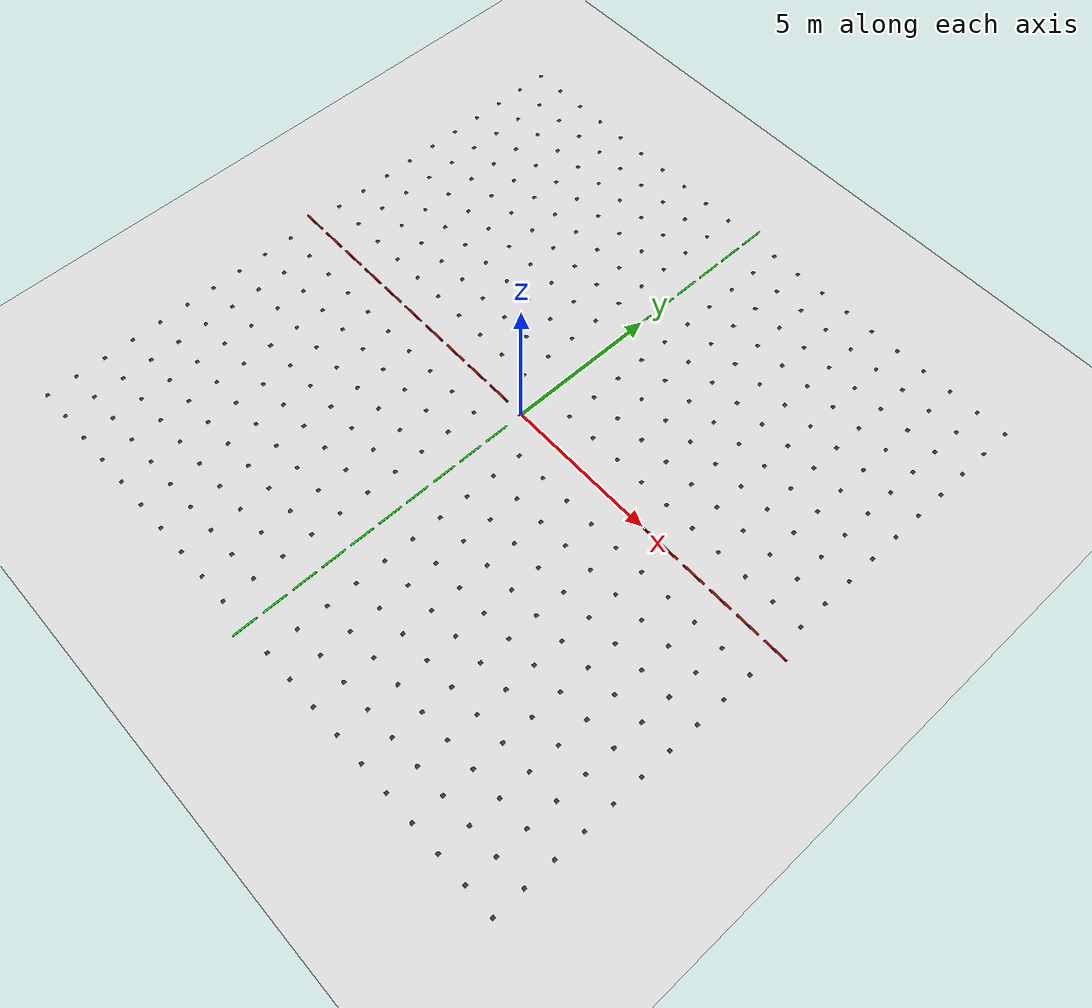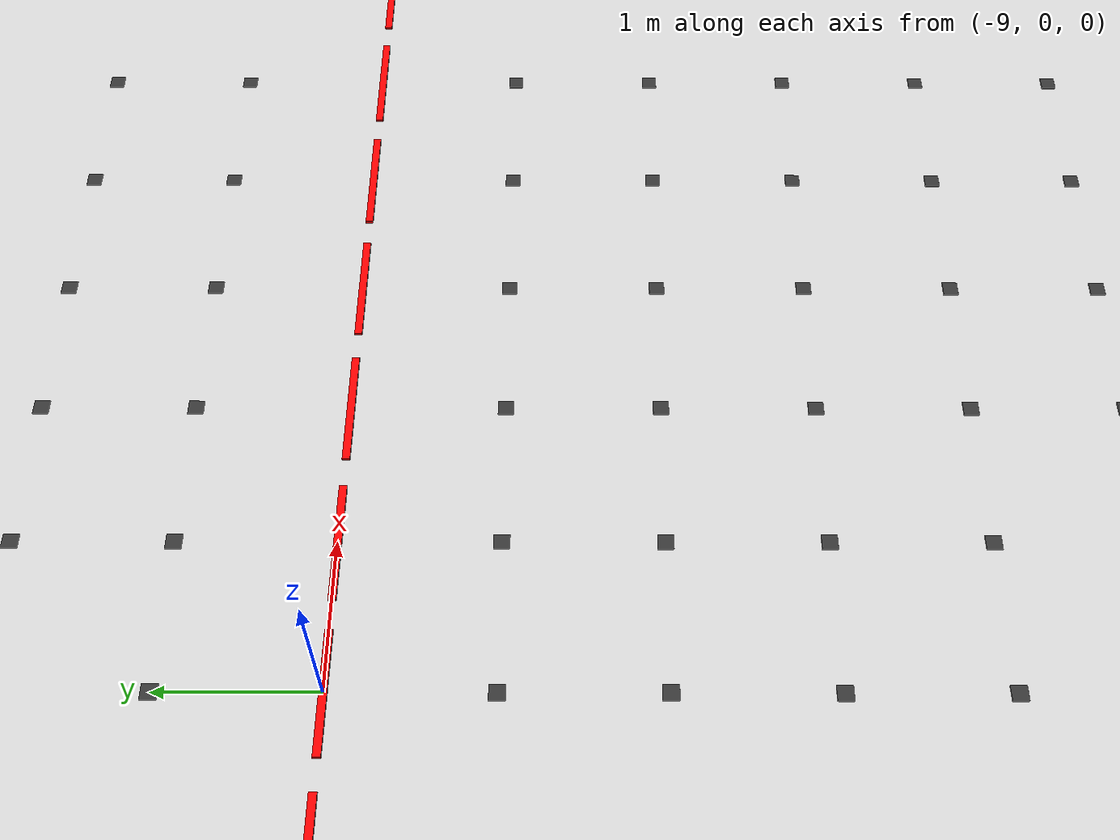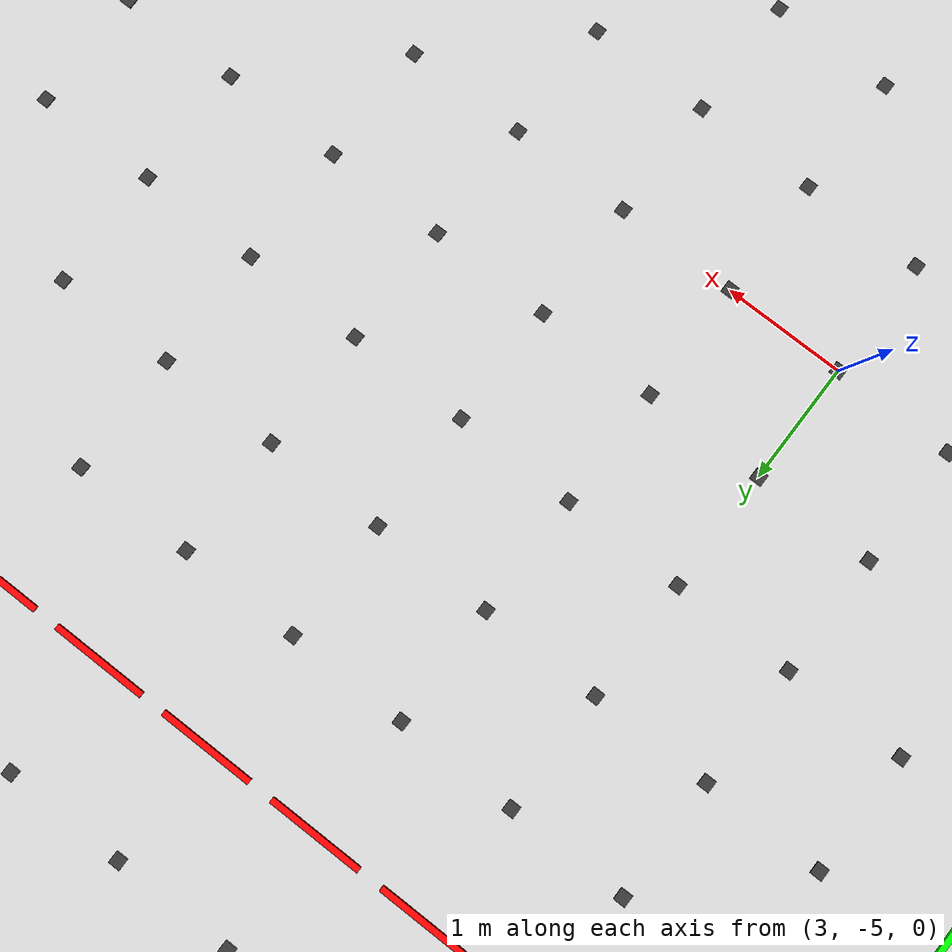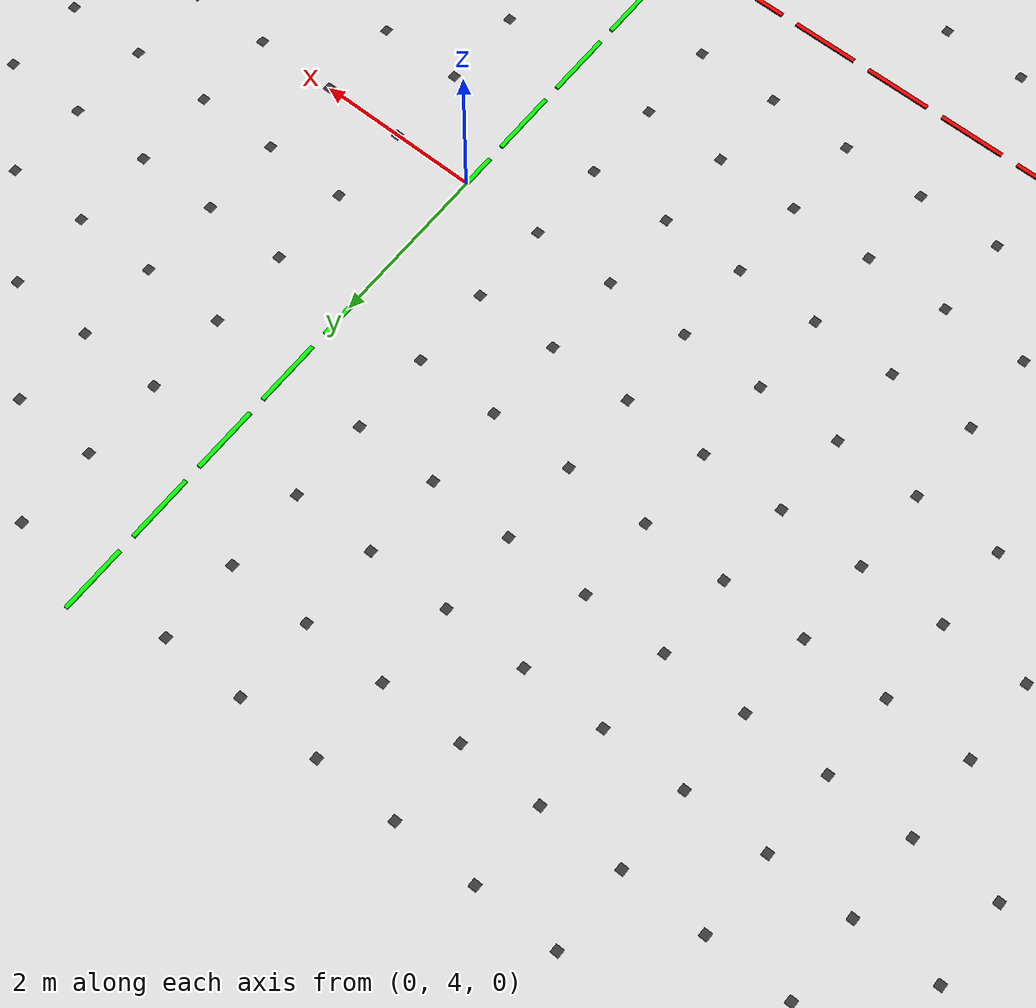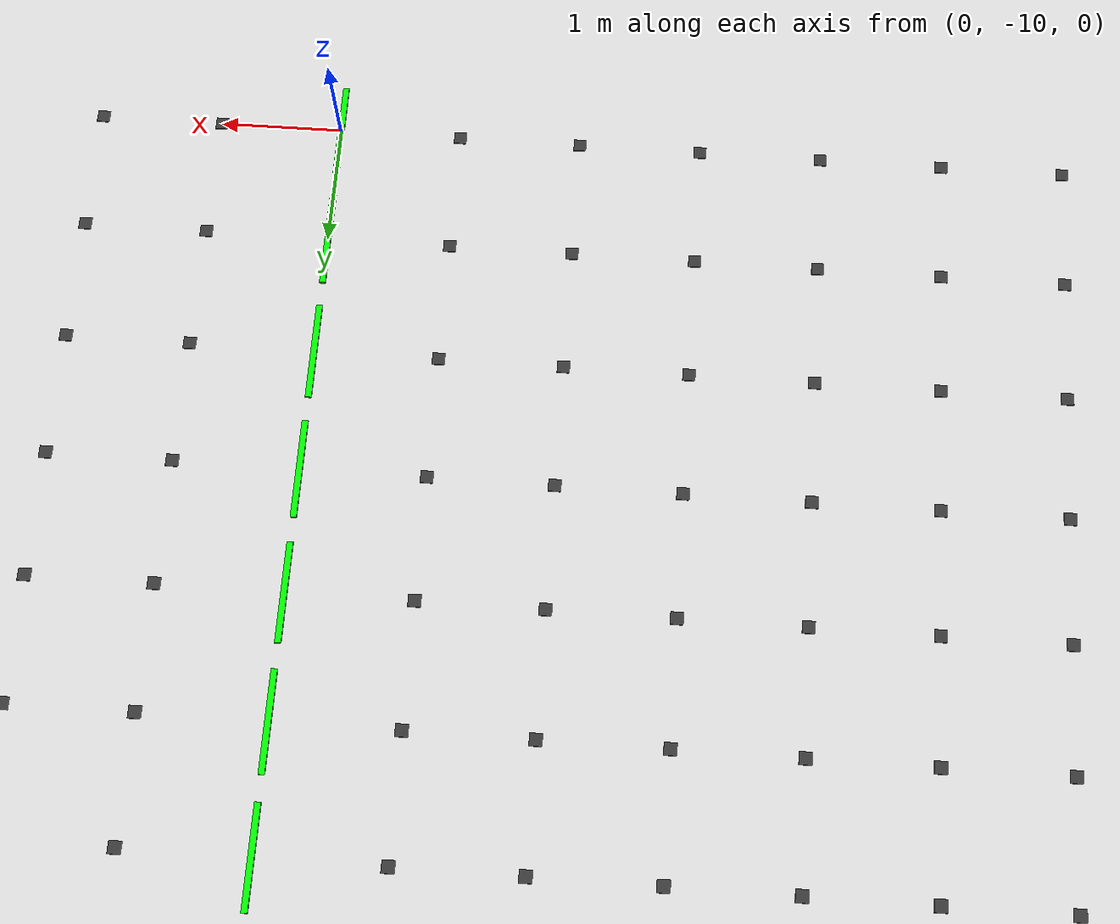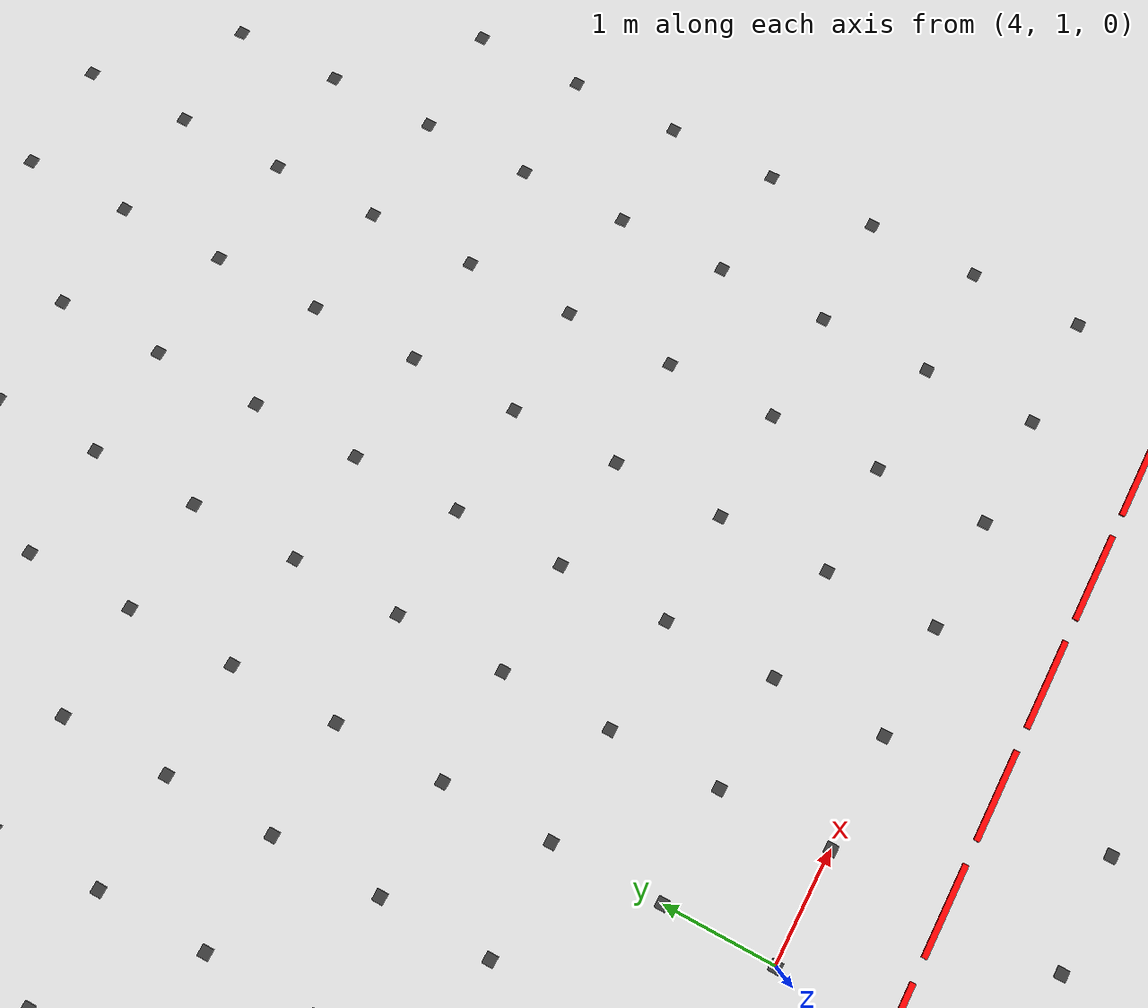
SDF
<?xml version="1.0"?>
<sdf version="1.6">
  <world name="default">
    <physics type="ode">
      <max_step_size>0.001</max_step_size>
      <real_time_factor>1</real_time_factor>
      <real_time_update_rate>1000</real_time_update_rate>
    </physics>
    <plugin name="gazebo_ros_state" filename="libgazebo_ros_state.so">
      <ros>
        <namespace>/gazebo</namespace>
      </ros>
    </plugin>
    <include>
      <uri>model://sun</uri>
    </include>
    <model name="solid_ground">
      <static>true</static>
      <link name="link">
        <collision name="collision">
          <geometry>
            <plane>
              <normal>0 0 1</normal>
              <size>100 100</size>
            </plane>
          </geometry>
        </collision>
        <visual name="visual">
          <geometry>
            <plane>
              <normal>0 0 1</normal>
              <size>100 100</size>
            </plane>
          </geometry>
          <material>
            <ambient>0.8 0.8 0.8 1</ambient>
            <diffuse>0.8 0.8 0.8 1</diffuse>
            <specular>0.1 0.1 0.1 1</specular>
          </material>
        </visual>
      </link>
      <plugin filename="libignition-gazebo-grid-system.so"
        name="ignition::gazebo::systems::Grid">
        <cell_length>1.0</cell_length>
        <cell_count>20</cell_count>
        <vertical_cell_count>20</vertical_cell_count>
        <horizontal_cell_count>20</horizontal_cell_count>
        <color>0 0 0 1</color>
        <ambient>0 0 0 1</ambient>
        <!-- Offset the grid lines so that intersections occur exactly at integer values -->
        <pose>0 0 0.001 0 0 0</pose>
      </plugin>
    </model>

    <model name="marker_-10_-10">
      <static>true</static>
      <pose>-10 -10 0.01 0 0 0</pose>
      <link name="link">
        <visual name="visual">
          <geometry>
            <box><size>0.1 0.1 0.01</size></box>
          </geometry>
          <material>
            <ambient>0.2 0.2 0.2 1</ambient>
            <diffuse>0.2 0.2 0.2 1</diffuse>
          </material>
        </visual>
      </link>
    </model>

    <model name="marker_-10_-9">
      <static>true</static>
      <pose>-10 -9 0.01 0 0 0</pose>
      <link name="link">
        <visual name="visual">
          <geometry>
            <box><size>0.1 0.1 0.01</size></box>
          </geometry>
          <material>
            <ambient>0.2 0.2 0.2 1</ambient>
            <diffuse>0.2 0.2 0.2 1</diffuse>
          </material>
        </visual>
      </link>
    </model>

    <model name="marker_-10_-8">
      <static>true</static>
      <pose>-10 -8 0.01 0 0 0</pose>
      <link name="link">
        <visual name="visual">
          <geometry>
            <box><size>0.1 0.1 0.01</size></box>
          </geometry>
          <material>
            <ambient>0.2 0.2 0.2 1</ambient>
            <diffuse>0.2 0.2 0.2 1</diffuse>
          </material>
        </visual>
      </link>
    </model>

    <model name="marker_-10_-7">
      <static>true</static>
      <pose>-10 -7 0.01 0 0 0</pose>
      <link name="link">
        <visual name="visual">
          <geometry>
            <box><size>0.1 0.1 0.01</size></box>
          </geometry>
          <material>
            <ambient>0.2 0.2 0.2 1</ambient>
            <diffuse>0.2 0.2 0.2 1</diffuse>
          </material>
        </visual>
      </link>
    </model>

    <model name="marker_-10_-6">
      <static>true</static>
      <pose>-10 -6 0.01 0 0 0</pose>
      <link name="link">
        <visual name="visual">
          <geometry>
            <box><size>0.1 0.1 0.01</size></box>
          </geometry>
          <material>
            <ambient>0.2 0.2 0.2 1</ambient>
            <diffuse>0.2 0.2 0.2 1</diffuse>
          </material>
        </visual>
      </link>
    </model>

    <model name="marker_-10_-5">
      <static>true</static>
      <pose>-10 -5 0.01 0 0 0</pose>
      <link name="link">
        <visual name="visual">
          <geometry>
            <box><size>0.1 0.1 0.01</size></box>
          </geometry>
          <material>
            <ambient>0.2 0.2 0.2 1</ambient>
            <diffuse>0.2 0.2 0.2 1</diffuse>
          </material>
        </visual>
      </link>
    </model>

    <model name="marker_-10_-4">
      <static>true</static>
      <pose>-10 -4 0.01 0 0 0</pose>
      <link name="link">
        <visual name="visual">
          <geometry>
            <box><size>0.1 0.1 0.01</size></box>
          </geometry>
          <material>
            <ambient>0.2 0.2 0.2 1</ambient>
            <diffuse>0.2 0.2 0.2 1</diffuse>
          </material>
        </visual>
      </link>
    </model>

    <model name="marker_-10_-3">
      <static>true</static>
      <pose>-10 -3 0.01 0 0 0</pose>
      <link name="link">
        <visual name="visual">
          <geometry>
            <box><size>0.1 0.1 0.01</size></box>
          </geometry>
          <material>
            <ambient>0.2 0.2 0.2 1</ambient>
            <diffuse>0.2 0.2 0.2 1</diffuse>
          </material>
        </visual>
      </link>
    </model>

    <model name="marker_-10_-2">
      <static>true</static>
      <pose>-10 -2 0.01 0 0 0</pose>
      <link name="link">
        <visual name="visual">
          <geometry>
            <box><size>0.1 0.1 0.01</size></box>
          </geometry>
          <material>
            <ambient>0.2 0.2 0.2 1</ambient>
            <diffuse>0.2 0.2 0.2 1</diffuse>
          </material>
        </visual>
      </link>
    </model>

    <model name="marker_-10_-1">
      <static>true</static>
      <pose>-10 -1 0.01 0 0 0</pose>
      <link name="link">
        <visual name="visual">
          <geometry>
            <box><size>0.1 0.1 0.01</size></box>
          </geometry>
          <material>
            <ambient>0.2 0.2 0.2 1</ambient>
            <diffuse>0.2 0.2 0.2 1</diffuse>
          </material>
        </visual>
      </link>
    </model>

    <model name="marker_-10_0">
      <static>true</static>
      <pose>-10 0 0.01 0 0 0</pose>
      <link name="link">
        <visual name="visual">
          <geometry>
            <box><size>0.8 0.05 0.02</size></box>
          </geometry>
          <material>
            <ambient>1 0 0 1</ambient>
            <diffuse>1 0 0 1</diffuse>
          </material>
        </visual>
      </link>
    </model>

    <model name="marker_-10_1">
      <static>true</static>
      <pose>-10 1 0.01 0 0 0</pose>
      <link name="link">
        <visual name="visual">
          <geometry>
            <box><size>0.1 0.1 0.01</size></box>
          </geometry>
          <material>
            <ambient>0.2 0.2 0.2 1</ambient>
            <diffuse>0.2 0.2 0.2 1</diffuse>
          </material>
        </visual>
      </link>
    </model>

    <model name="marker_-10_2">
      <static>true</static>
      <pose>-10 2 0.01 0 0 0</pose>
      <link name="link">
        <visual name="visual">
          <geometry>
            <box><size>0.1 0.1 0.01</size></box>
          </geometry>
          <material>
            <ambient>0.2 0.2 0.2 1</ambient>
            <diffuse>0.2 0.2 0.2 1</diffuse>
          </material>
        </visual>
      </link>
    </model>

    <model name="marker_-10_3">
      <static>true</static>
      <pose>-10 3 0.01 0 0 0</pose>
      <link name="link">
        <visual name="visual">
          <geometry>
            <box><size>0.1 0.1 0.01</size></box>
          </geometry>
          <material>
            <ambient>0.2 0.2 0.2 1</ambient>
            <diffuse>0.2 0.2 0.2 1</diffuse>
          </material>
        </visual>
      </link>
    </model>

    <model name="marker_-10_4">
      <static>true</static>
      <pose>-10 4 0.01 0 0 0</pose>
      <link name="link">
        <visual name="visual">
          <geometry>
            <box><size>0.1 0.1 0.01</size></box>
          </geometry>
          <material>
            <ambient>0.2 0.2 0.2 1</ambient>
            <diffuse>0.2 0.2 0.2 1</diffuse>
          </material>
        </visual>
      </link>
    </model>

    <model name="marker_-10_5">
      <static>true</static>
      <pose>-10 5 0.01 0 0 0</pose>
      <link name="link">
        <visual name="visual">
          <geometry>
            <box><size>0.1 0.1 0.01</size></box>
          </geometry>
          <material>
            <ambient>0.2 0.2 0.2 1</ambient>
            <diffuse>0.2 0.2 0.2 1</diffuse>
          </material>
        </visual>
      </link>
    </model>

    <model name="marker_-10_6">
      <static>true</static>
      <pose>-10 6 0.01 0 0 0</pose>
      <link name="link">
        <visual name="visual">
          <geometry>
            <box><size>0.1 0.1 0.01</size></box>
          </geometry>
          <material>
            <ambient>0.2 0.2 0.2 1</ambient>
            <diffuse>0.2 0.2 0.2 1</diffuse>
          </material>
        </visual>
      </link>
    </model>

    <model name="marker_-10_7">
      <static>true</static>
      <pose>-10 7 0.01 0 0 0</pose>
      <link name="link">
        <visual name="visual">
          <geometry>
            <box><size>0.1 0.1 0.01</size></box>
          </geometry>
          <material>
            <ambient>0.2 0.2 0.2 1</ambient>
            <diffuse>0.2 0.2 0.2 1</diffuse>
          </material>
        </visual>
      </link>
    </model>

    <model name="marker_-10_8">
      <static>true</static>
      <pose>-10 8 0.01 0 0 0</pose>
      <link name="link">
        <visual name="visual">
          <geometry>
            <box><size>0.1 0.1 0.01</size></box>
          </geometry>
          <material>
            <ambient>0.2 0.2 0.2 1</ambient>
            <diffuse>0.2 0.2 0.2 1</diffuse>
          </material>
        </visual>
      </link>
    </model>

    <model name="marker_-10_9">
      <static>true</static>
      <pose>-10 9 0.01 0 0 0</pose>
      <link name="link">
        <visual name="visual">
          <geometry>
            <box><size>0.1 0.1 0.01</size></box>
          </geometry>
          <material>
            <ambient>0.2 0.2 0.2 1</ambient>
            <diffuse>0.2 0.2 0.2 1</diffuse>
          </material>
        </visual>
      </link>
    </model>

    <model name="marker_-10_10">
      <static>true</static>
      <pose>-10 10 0.01 0 0 0</pose>
      <link name="link">
        <visual name="visual">
          <geometry>
            <box><size>0.1 0.1 0.01</size></box>
          </geometry>
          <material>
            <ambient>0.2 0.2 0.2 1</ambient>
            <diffuse>0.2 0.2 0.2 1</diffuse>
          </material>
        </visual>
      </link>
    </model>

    <model name="marker_-9_-10">
      <static>true</static>
      <pose>-9 -10 0.01 0 0 0</pose>
      <link name="link">
        <visual name="visual">
          <geometry>
            <box><size>0.1 0.1 0.01</size></box>
          </geometry>
          <material>
            <ambient>0.2 0.2 0.2 1</ambient>
            <diffuse>0.2 0.2 0.2 1</diffuse>
          </material>
        </visual>
      </link>
    </model>

    <model name="marker_-9_-9">
      <static>true</static>
      <pose>-9 -9 0.01 0 0 0</pose>
      <link name="link">
        <visual name="visual">
          <geometry>
            <box><size>0.1 0.1 0.01</size></box>
          </geometry>
          <material>
            <ambient>0.2 0.2 0.2 1</ambient>
            <diffuse>0.2 0.2 0.2 1</diffuse>
          </material>
        </visual>
      </link>
    </model>

    <model name="marker_-9_-8">
      <static>true</static>
      <pose>-9 -8 0.01 0 0 0</pose>
      <link name="link">
        <visual name="visual">
          <geometry>
            <box><size>0.1 0.1 0.01</size></box>
          </geometry>
          <material>
            <ambient>0.2 0.2 0.2 1</ambient>
            <diffuse>0.2 0.2 0.2 1</diffuse>
          </material>
        </visual>
      </link>
    </model>

    <model name="marker_-9_-7">
      <static>true</static>
      <pose>-9 -7 0.01 0 0 0</pose>
      <link name="link">
        <visual name="visual">
          <geometry>
            <box><size>0.1 0.1 0.01</size></box>
          </geometry>
          <material>
            <ambient>0.2 0.2 0.2 1</ambient>
            <diffuse>0.2 0.2 0.2 1</diffuse>
          </material>
        </visual>
      </link>
    </model>

    <model name="marker_-9_-6">
      <static>true</static>
      <pose>-9 -6 0.01 0 0 0</pose>
      <link name="link">
        <visual name="visual">
          <geometry>
            <box><size>0.1 0.1 0.01</size></box>
          </geometry>
          <material>
            <ambient>0.2 0.2 0.2 1</ambient>
            <diffuse>0.2 0.2 0.2 1</diffuse>
          </material>
        </visual>
      </link>
    </model>

    <model name="marker_-9_-5">
      <static>true</static>
      <pose>-9 -5 0.01 0 0 0</pose>
      <link name="link">
        <visual name="visual">
          <geometry>
            <box><size>0.1 0.1 0.01</size></box>
          </geometry>
          <material>
            <ambient>0.2 0.2 0.2 1</ambient>
            <diffuse>0.2 0.2 0.2 1</diffuse>
          </material>
        </visual>
      </link>
    </model>

    <model name="marker_-9_-4">
      <static>true</static>
      <pose>-9 -4 0.01 0 0 0</pose>
      <link name="link">
        <visual name="visual">
          <geometry>
            <box><size>0.1 0.1 0.01</size></box>
          </geometry>
          <material>
            <ambient>0.2 0.2 0.2 1</ambient>
            <diffuse>0.2 0.2 0.2 1</diffuse>
          </material>
        </visual>
      </link>
    </model>

    <model name="marker_-9_-3">
      <static>true</static>
      <pose>-9 -3 0.01 0 0 0</pose>
      <link name="link">
        <visual name="visual">
          <geometry>
            <box><size>0.1 0.1 0.01</size></box>
          </geometry>
          <material>
            <ambient>0.2 0.2 0.2 1</ambient>
            <diffuse>0.2 0.2 0.2 1</diffuse>
          </material>
        </visual>
      </link>
    </model>

    <model name="marker_-9_-2">
      <static>true</static>
      <pose>-9 -2 0.01 0 0 0</pose>
      <link name="link">
        <visual name="visual">
          <geometry>
            <box><size>0.1 0.1 0.01</size></box>
          </geometry>
          <material>
            <ambient>0.2 0.2 0.2 1</ambient>
            <diffuse>0.2 0.2 0.2 1</diffuse>
          </material>
        </visual>
      </link>
    </model>

    <model name="marker_-9_-1">
      <static>true</static>
      <pose>-9 -1 0.01 0 0 0</pose>
      <link name="link">
        <visual name="visual">
          <geometry>
            <box><size>0.1 0.1 0.01</size></box>
          </geometry>
          <material>
            <ambient>0.2 0.2 0.2 1</ambient>
            <diffuse>0.2 0.2 0.2 1</diffuse>
          </material>
        </visual>
      </link>
    </model>

    <model name="marker_-9_0">
      <static>true</static>
      <pose>-9 0 0.01 0 0 0</pose>
      <link name="link">
        <visual name="visual">
          <geometry>
            <box><size>0.8 0.05 0.02</size></box>
          </geometry>
          <material>
            <ambient>1 0 0 1</ambient>
            <diffuse>1 0 0 1</diffuse>
          </material>
        </visual>
      </link>
    </model>

    <model name="marker_-9_1">
      <static>true</static>
      <pose>-9 1 0.01 0 0 0</pose>
      <link name="link">
        <visual name="visual">
          <geometry>
            <box><size>0.1 0.1 0.01</size></box>
          </geometry>
          <material>
            <ambient>0.2 0.2 0.2 1</ambient>
            <diffuse>0.2 0.2 0.2 1</diffuse>
          </material>
        </visual>
      </link>
    </model>

    <model name="marker_-9_2">
      <static>true</static>
      <pose>-9 2 0.01 0 0 0</pose>
      <link name="link">
        <visual name="visual">
          <geometry>
            <box><size>0.1 0.1 0.01</size></box>
          </geometry>
          <material>
            <ambient>0.2 0.2 0.2 1</ambient>
            <diffuse>0.2 0.2 0.2 1</diffuse>
          </material>
        </visual>
      </link>
    </model>

    <model name="marker_-9_3">
      <static>true</static>
      <pose>-9 3 0.01 0 0 0</pose>
      <link name="link">
        <visual name="visual">
          <geometry>
            <box><size>0.1 0.1 0.01</size></box>
          </geometry>
          <material>
            <ambient>0.2 0.2 0.2 1</ambient>
            <diffuse>0.2 0.2 0.2 1</diffuse>
          </material>
        </visual>
      </link>
    </model>

    <model name="marker_-9_4">
      <static>true</static>
      <pose>-9 4 0.01 0 0 0</pose>
      <link name="link">
        <visual name="visual">
          <geometry>
            <box><size>0.1 0.1 0.01</size></box>
          </geometry>
          <material>
            <ambient>0.2 0.2 0.2 1</ambient>
            <diffuse>0.2 0.2 0.2 1</diffuse>
          </material>
        </visual>
      </link>
    </model>

    <model name="marker_-9_5">
      <static>true</static>
      <pose>-9 5 0.01 0 0 0</pose>
      <link name="link">
        <visual name="visual">
          <geometry>
            <box><size>0.1 0.1 0.01</size></box>
          </geometry>
          <material>
            <ambient>0.2 0.2 0.2 1</ambient>
            <diffuse>0.2 0.2 0.2 1</diffuse>
          </material>
        </visual>
      </link>
    </model>

    <model name="marker_-9_6">
      <static>true</static>
      <pose>-9 6 0.01 0 0 0</pose>
      <link name="link">
        <visual name="visual">
          <geometry>
            <box><size>0.1 0.1 0.01</size></box>
          </geometry>
          <material>
            <ambient>0.2 0.2 0.2 1</ambient>
            <diffuse>0.2 0.2 0.2 1</diffuse>
          </material>
        </visual>
      </link>
    </model>

    <model name="marker_-9_7">
      <static>true</static>
      <pose>-9 7 0.01 0 0 0</pose>
      <link name="link">
        <visual name="visual">
          <geometry>
            <box><size>0.1 0.1 0.01</size></box>
          </geometry>
          <material>
            <ambient>0.2 0.2 0.2 1</ambient>
            <diffuse>0.2 0.2 0.2 1</diffuse>
          </material>
        </visual>
      </link>
    </model>

    <model name="marker_-9_8">
      <static>true</static>
      <pose>-9 8 0.01 0 0 0</pose>
      <link name="link">
        <visual name="visual">
          <geometry>
            <box><size>0.1 0.1 0.01</size></box>
          </geometry>
          <material>
            <ambient>0.2 0.2 0.2 1</ambient>
            <diffuse>0.2 0.2 0.2 1</diffuse>
          </material>
        </visual>
      </link>
    </model>

    <model name="marker_-9_9">
      <static>true</static>
      <pose>-9 9 0.01 0 0 0</pose>
      <link name="link">
        <visual name="visual">
          <geometry>
            <box><size>0.1 0.1 0.01</size></box>
          </geometry>
          <material>
            <ambient>0.2 0.2 0.2 1</ambient>
            <diffuse>0.2 0.2 0.2 1</diffuse>
          </material>
        </visual>
      </link>
    </model>

    <model name="marker_-9_10">
      <static>true</static>
      <pose>-9 10 0.01 0 0 0</pose>
      <link name="link">
        <visual name="visual">
          <geometry>
            <box><size>0.1 0.1 0.01</size></box>
          </geometry>
          <material>
            <ambient>0.2 0.2 0.2 1</ambient>
            <diffuse>0.2 0.2 0.2 1</diffuse>
          </material>
        </visual>
      </link>
    </model>

    <model name="marker_-8_-10">
      <static>true</static>
      <pose>-8 -10 0.01 0 0 0</pose>
      <link name="link">
        <visual name="visual">
          <geometry>
            <box><size>0.1 0.1 0.01</size></box>
          </geometry>
          <material>
            <ambient>0.2 0.2 0.2 1</ambient>
            <diffuse>0.2 0.2 0.2 1</diffuse>
          </material>
        </visual>
      </link>
    </model>

    <model name="marker_-8_-9">
      <static>true</static>
      <pose>-8 -9 0.01 0 0 0</pose>
      <link name="link">
        <visual name="visual">
          <geometry>
            <box><size>0.1 0.1 0.01</size></box>
          </geometry>
          <material>
            <ambient>0.2 0.2 0.2 1</ambient>
            <diffuse>0.2 0.2 0.2 1</diffuse>
          </material>
        </visual>
      </link>
    </model>

    <model name="marker_-8_-8">
      <static>true</static>
      <pose>-8 -8 0.01 0 0 0</pose>
      <link name="link">
        <visual name="visual">
          <geometry>
            <box><size>0.1 0.1 0.01</size></box>
          </geometry>
          <material>
            <ambient>0.2 0.2 0.2 1</ambient>
            <diffuse>0.2 0.2 0.2 1</diffuse>
          </material>
        </visual>
      </link>
    </model>

    <model name="marker_-8_-7">
      <static>true</static>
      <pose>-8 -7 0.01 0 0 0</pose>
      <link name="link">
        <visual name="visual">
          <geometry>
            <box><size>0.1 0.1 0.01</size></box>
          </geometry>
          <material>
            <ambient>0.2 0.2 0.2 1</ambient>
            <diffuse>0.2 0.2 0.2 1</diffuse>
          </material>
        </visual>
      </link>
    </model>

    <model name="marker_-8_-6">
      <static>true</static>
      <pose>-8 -6 0.01 0 0 0</pose>
      <link name="link">
        <visual name="visual">
          <geometry>
            <box><size>0.1 0.1 0.01</size></box>
          </geometry>
          <material>
            <ambient>0.2 0.2 0.2 1</ambient>
            <diffuse>0.2 0.2 0.2 1</diffuse>
          </material>
        </visual>
      </link>
    </model>

    <model name="marker_-8_-5">
      <static>true</static>
      <pose>-8 -5 0.01 0 0 0</pose>
      <link name="link">
        <visual name="visual">
          <geometry>
            <box><size>0.1 0.1 0.01</size></box>
          </geometry>
          <material>
            <ambient>0.2 0.2 0.2 1</ambient>
            <diffuse>0.2 0.2 0.2 1</diffuse>
          </material>
        </visual>
      </link>
    </model>

    <model name="marker_-8_-4">
      <static>true</static>
      <pose>-8 -4 0.01 0 0 0</pose>
      <link name="link">
        <visual name="visual">
          <geometry>
            <box><size>0.1 0.1 0.01</size></box>
          </geometry>
          <material>
            <ambient>0.2 0.2 0.2 1</ambient>
            <diffuse>0.2 0.2 0.2 1</diffuse>
          </material>
        </visual>
      </link>
    </model>

    <model name="marker_-8_-3">
      <static>true</static>
      <pose>-8 -3 0.01 0 0 0</pose>
      <link name="link">
        <visual name="visual">
          <geometry>
            <box><size>0.1 0.1 0.01</size></box>
          </geometry>
          <material>
            <ambient>0.2 0.2 0.2 1</ambient>
            <diffuse>0.2 0.2 0.2 1</diffuse>
          </material>
        </visual>
      </link>
    </model>

    <model name="marker_-8_-2">
      <static>true</static>
      <pose>-8 -2 0.01 0 0 0</pose>
      <link name="link">
        <visual name="visual">
          <geometry>
            <box><size>0.1 0.1 0.01</size></box>
          </geometry>
          <material>
            <ambient>0.2 0.2 0.2 1</ambient>
            <diffuse>0.2 0.2 0.2 1</diffuse>
          </material>
        </visual>
      </link>
    </model>

    <model name="marker_-8_-1">
      <static>true</static>
      <pose>-8 -1 0.01 0 0 0</pose>
      <link name="link">
        <visual name="visual">
          <geometry>
            <box><size>0.1 0.1 0.01</size></box>
          </geometry>
          <material>
            <ambient>0.2 0.2 0.2 1</ambient>
            <diffuse>0.2 0.2 0.2 1</diffuse>
          </material>
        </visual>
      </link>
    </model>

    <model name="marker_-8_0">
      <static>true</static>
      <pose>-8 0 0.01 0 0 0</pose>
      <link name="link">
        <visual name="visual">
          <geometry>
            <box><size>0.8 0.05 0.02</size></box>
          </geometry>
          <material>
            <ambient>1 0 0 1</ambient>
            <diffuse>1 0 0 1</diffuse>
          </material>
        </visual>
      </link>
    </model>

    <model name="marker_-8_1">
      <static>true</static>
      <pose>-8 1 0.01 0 0 0</pose>
      <link name="link">
        <visual name="visual">
          <geometry>
            <box><size>0.1 0.1 0.01</size></box>
          </geometry>
          <material>
            <ambient>0.2 0.2 0.2 1</ambient>
            <diffuse>0.2 0.2 0.2 1</diffuse>
          </material>
        </visual>
      </link>
    </model>

    <model name="marker_-8_2">
      <static>true</static>
      <pose>-8 2 0.01 0 0 0</pose>
      <link name="link">
        <visual name="visual">
          <geometry>
            <box><size>0.1 0.1 0.01</size></box>
          </geometry>
          <material>
            <ambient>0.2 0.2 0.2 1</ambient>
            <diffuse>0.2 0.2 0.2 1</diffuse>
          </material>
        </visual>
      </link>
    </model>

    <model name="marker_-8_3">
      <static>true</static>
      <pose>-8 3 0.01 0 0 0</pose>
      <link name="link">
        <visual name="visual">
          <geometry>
            <box><size>0.1 0.1 0.01</size></box>
          </geometry>
          <material>
            <ambient>0.2 0.2 0.2 1</ambient>
            <diffuse>0.2 0.2 0.2 1</diffuse>
          </material>
        </visual>
      </link>
    </model>

    <model name="marker_-8_4">
      <static>true</static>
      <pose>-8 4 0.01 0 0 0</pose>
      <link name="link">
        <visual name="visual">
          <geometry>
            <box><size>0.1 0.1 0.01</size></box>
          </geometry>
          <material>
            <ambient>0.2 0.2 0.2 1</ambient>
            <diffuse>0.2 0.2 0.2 1</diffuse>
          </material>
        </visual>
      </link>
    </model>

    <model name="marker_-8_5">
      <static>true</static>
      <pose>-8 5 0.01 0 0 0</pose>
      <link name="link">
        <visual name="visual">
          <geometry>
            <box><size>0.1 0.1 0.01</size></box>
          </geometry>
          <material>
            <ambient>0.2 0.2 0.2 1</ambient>
            <diffuse>0.2 0.2 0.2 1</diffuse>
          </material>
        </visual>
      </link>
    </model>

    <model name="marker_-8_6">
      <static>true</static>
      <pose>-8 6 0.01 0 0 0</pose>
      <link name="link">
        <visual name="visual">
          <geometry>
            <box><size>0.1 0.1 0.01</size></box>
          </geometry>
          <material>
            <ambient>0.2 0.2 0.2 1</ambient>
            <diffuse>0.2 0.2 0.2 1</diffuse>
          </material>
        </visual>
      </link>
    </model>

    <model name="marker_-8_7">
      <static>true</static>
      <pose>-8 7 0.01 0 0 0</pose>
      <link name="link">
        <visual name="visual">
          <geometry>
            <box><size>0.1 0.1 0.01</size></box>
          </geometry>
          <material>
            <ambient>0.2 0.2 0.2 1</ambient>
            <diffuse>0.2 0.2 0.2 1</diffuse>
          </material>
        </visual>
      </link>
    </model>

    <model name="marker_-8_8">
      <static>true</static>
      <pose>-8 8 0.01 0 0 0</pose>
      <link name="link">
        <visual name="visual">
          <geometry>
            <box><size>0.1 0.1 0.01</size></box>
          </geometry>
          <material>
            <ambient>0.2 0.2 0.2 1</ambient>
            <diffuse>0.2 0.2 0.2 1</diffuse>
          </material>
        </visual>
      </link>
    </model>

    <model name="marker_-8_9">
      <static>true</static>
      <pose>-8 9 0.01 0 0 0</pose>
      <link name="link">
        <visual name="visual">
          <geometry>
            <box><size>0.1 0.1 0.01</size></box>
          </geometry>
          <material>
            <ambient>0.2 0.2 0.2 1</ambient>
            <diffuse>0.2 0.2 0.2 1</diffuse>
          </material>
        </visual>
      </link>
    </model>

    <model name="marker_-8_10">
      <static>true</static>
      <pose>-8 10 0.01 0 0 0</pose>
      <link name="link">
        <visual name="visual">
          <geometry>
            <box><size>0.1 0.1 0.01</size></box>
          </geometry>
          <material>
            <ambient>0.2 0.2 0.2 1</ambient>
            <diffuse>0.2 0.2 0.2 1</diffuse>
          </material>
        </visual>
      </link>
    </model>

    <model name="marker_-7_-10">
      <static>true</static>
      <pose>-7 -10 0.01 0 0 0</pose>
      <link name="link">
        <visual name="visual">
          <geometry>
            <box><size>0.1 0.1 0.01</size></box>
          </geometry>
          <material>
            <ambient>0.2 0.2 0.2 1</ambient>
            <diffuse>0.2 0.2 0.2 1</diffuse>
          </material>
        </visual>
      </link>
    </model>

    <model name="marker_-7_-9">
      <static>true</static>
      <pose>-7 -9 0.01 0 0 0</pose>
      <link name="link">
        <visual name="visual">
          <geometry>
            <box><size>0.1 0.1 0.01</size></box>
          </geometry>
          <material>
            <ambient>0.2 0.2 0.2 1</ambient>
            <diffuse>0.2 0.2 0.2 1</diffuse>
          </material>
        </visual>
      </link>
    </model>

    <model name="marker_-7_-8">
      <static>true</static>
      <pose>-7 -8 0.01 0 0 0</pose>
      <link name="link">
        <visual name="visual">
          <geometry>
            <box><size>0.1 0.1 0.01</size></box>
          </geometry>
          <material>
            <ambient>0.2 0.2 0.2 1</ambient>
            <diffuse>0.2 0.2 0.2 1</diffuse>
          </material>
        </visual>
      </link>
    </model>

    <model name="marker_-7_-7">
      <static>true</static>
      <pose>-7 -7 0.01 0 0 0</pose>
      <link name="link">
        <visual name="visual">
          <geometry>
            <box><size>0.1 0.1 0.01</size></box>
          </geometry>
          <material>
            <ambient>0.2 0.2 0.2 1</ambient>
            <diffuse>0.2 0.2 0.2 1</diffuse>
          </material>
        </visual>
      </link>
    </model>

    <model name="marker_-7_-6">
      <static>true</static>
      <pose>-7 -6 0.01 0 0 0</pose>
      <link name="link">
        <visual name="visual">
          <geometry>
            <box><size>0.1 0.1 0.01</size></box>
          </geometry>
          <material>
            <ambient>0.2 0.2 0.2 1</ambient>
            <diffuse>0.2 0.2 0.2 1</diffuse>
          </material>
        </visual>
      </link>
    </model>

    <model name="marker_-7_-5">
      <static>true</static>
      <pose>-7 -5 0.01 0 0 0</pose>
      <link name="link">
        <visual name="visual">
          <geometry>
            <box><size>0.1 0.1 0.01</size></box>
          </geometry>
          <material>
            <ambient>0.2 0.2 0.2 1</ambient>
            <diffuse>0.2 0.2 0.2 1</diffuse>
          </material>
        </visual>
      </link>
    </model>

    <model name="marker_-7_-4">
      <static>true</static>
      <pose>-7 -4 0.01 0 0 0</pose>
      <link name="link">
        <visual name="visual">
          <geometry>
            <box><size>0.1 0.1 0.01</size></box>
          </geometry>
          <material>
            <ambient>0.2 0.2 0.2 1</ambient>
            <diffuse>0.2 0.2 0.2 1</diffuse>
          </material>
        </visual>
      </link>
    </model>

    <model name="marker_-7_-3">
      <static>true</static>
      <pose>-7 -3 0.01 0 0 0</pose>
      <link name="link">
        <visual name="visual">
          <geometry>
            <box><size>0.1 0.1 0.01</size></box>
          </geometry>
          <material>
            <ambient>0.2 0.2 0.2 1</ambient>
            <diffuse>0.2 0.2 0.2 1</diffuse>
          </material>
        </visual>
      </link>
    </model>

    <model name="marker_-7_-2">
      <static>true</static>
      <pose>-7 -2 0.01 0 0 0</pose>
      <link name="link">
        <visual name="visual">
          <geometry>
            <box><size>0.1 0.1 0.01</size></box>
          </geometry>
          <material>
            <ambient>0.2 0.2 0.2 1</ambient>
            <diffuse>0.2 0.2 0.2 1</diffuse>
          </material>
        </visual>
      </link>
    </model>

    <model name="marker_-7_-1">
      <static>true</static>
      <pose>-7 -1 0.01 0 0 0</pose>
      <link name="link">
        <visual name="visual">
          <geometry>
            <box><size>0.1 0.1 0.01</size></box>
          </geometry>
          <material>
            <ambient>0.2 0.2 0.2 1</ambient>
            <diffuse>0.2 0.2 0.2 1</diffuse>
          </material>
        </visual>
      </link>
    </model>

    <model name="marker_-7_0">
      <static>true</static>
      <pose>-7 0 0.01 0 0 0</pose>
      <link name="link">
        <visual name="visual">
          <geometry>
            <box><size>0.8 0.05 0.02</size></box>
          </geometry>
          <material>
            <ambient>1 0 0 1</ambient>
            <diffuse>1 0 0 1</diffuse>
          </material>
        </visual>
      </link>
    </model>

    <model name="marker_-7_1">
      <static>true</static>
      <pose>-7 1 0.01 0 0 0</pose>
      <link name="link">
        <visual name="visual">
          <geometry>
            <box><size>0.1 0.1 0.01</size></box>
          </geometry>
          <material>
            <ambient>0.2 0.2 0.2 1</ambient>
            <diffuse>0.2 0.2 0.2 1</diffuse>
          </material>
        </visual>
      </link>
    </model>

    <model name="marker_-7_2">
      <static>true</static>
      <pose>-7 2 0.01 0 0 0</pose>
      <link name="link">
        <visual name="visual">
          <geometry>
            <box><size>0.1 0.1 0.01</size></box>
          </geometry>
          <material>
            <ambient>0.2 0.2 0.2 1</ambient>
            <diffuse>0.2 0.2 0.2 1</diffuse>
          </material>
        </visual>
      </link>
    </model>

    <model name="marker_-7_3">
      <static>true</static>
      <pose>-7 3 0.01 0 0 0</pose>
      <link name="link">
        <visual name="visual">
          <geometry>
            <box><size>0.1 0.1 0.01</size></box>
          </geometry>
          <material>
            <ambient>0.2 0.2 0.2 1</ambient>
            <diffuse>0.2 0.2 0.2 1</diffuse>
          </material>
        </visual>
      </link>
    </model>

    <model name="marker_-7_4">
      <static>true</static>
      <pose>-7 4 0.01 0 0 0</pose>
      <link name="link">
        <visual name="visual">
          <geometry>
            <box><size>0.1 0.1 0.01</size></box>
          </geometry>
          <material>
            <ambient>0.2 0.2 0.2 1</ambient>
            <diffuse>0.2 0.2 0.2 1</diffuse>
          </material>
        </visual>
      </link>
    </model>

    <model name="marker_-7_5">
      <static>true</static>
      <pose>-7 5 0.01 0 0 0</pose>
      <link name="link">
        <visual name="visual">
          <geometry>
            <box><size>0.1 0.1 0.01</size></box>
          </geometry>
          <material>
            <ambient>0.2 0.2 0.2 1</ambient>
            <diffuse>0.2 0.2 0.2 1</diffuse>
          </material>
        </visual>
      </link>
    </model>

    <model name="marker_-7_6">
      <static>true</static>
      <pose>-7 6 0.01 0 0 0</pose>
      <link name="link">
        <visual name="visual">
          <geometry>
            <box><size>0.1 0.1 0.01</size></box>
          </geometry>
          <material>
            <ambient>0.2 0.2 0.2 1</ambient>
            <diffuse>0.2 0.2 0.2 1</diffuse>
          </material>
        </visual>
      </link>
    </model>

    <model name="marker_-7_7">
      <static>true</static>
      <pose>-7 7 0.01 0 0 0</pose>
      <link name="link">
        <visual name="visual">
          <geometry>
            <box><size>0.1 0.1 0.01</size></box>
          </geometry>
          <material>
            <ambient>0.2 0.2 0.2 1</ambient>
            <diffuse>0.2 0.2 0.2 1</diffuse>
          </material>
        </visual>
      </link>
    </model>

    <model name="marker_-7_8">
      <static>true</static>
      <pose>-7 8 0.01 0 0 0</pose>
      <link name="link">
        <visual name="visual">
          <geometry>
            <box><size>0.1 0.1 0.01</size></box>
          </geometry>
          <material>
            <ambient>0.2 0.2 0.2 1</ambient>
            <diffuse>0.2 0.2 0.2 1</diffuse>
          </material>
        </visual>
      </link>
    </model>

    <model name="marker_-7_9">
      <static>true</static>
      <pose>-7 9 0.01 0 0 0</pose>
      <link name="link">
        <visual name="visual">
          <geometry>
            <box><size>0.1 0.1 0.01</size></box>
          </geometry>
          <material>
            <ambient>0.2 0.2 0.2 1</ambient>
            <diffuse>0.2 0.2 0.2 1</diffuse>
          </material>
        </visual>
      </link>
    </model>

    <model name="marker_-7_10">
      <static>true</static>
      <pose>-7 10 0.01 0 0 0</pose>
      <link name="link">
        <visual name="visual">
          <geometry>
            <box><size>0.1 0.1 0.01</size></box>
          </geometry>
          <material>
            <ambient>0.2 0.2 0.2 1</ambient>
            <diffuse>0.2 0.2 0.2 1</diffuse>
          </material>
        </visual>
      </link>
    </model>

    <model name="marker_-6_-10">
      <static>true</static>
      <pose>-6 -10 0.01 0 0 0</pose>
      <link name="link">
        <visual name="visual">
          <geometry>
            <box><size>0.1 0.1 0.01</size></box>
          </geometry>
          <material>
            <ambient>0.2 0.2 0.2 1</ambient>
            <diffuse>0.2 0.2 0.2 1</diffuse>
          </material>
        </visual>
      </link>
    </model>

    <model name="marker_-6_-9">
      <static>true</static>
      <pose>-6 -9 0.01 0 0 0</pose>
      <link name="link">
        <visual name="visual">
          <geometry>
            <box><size>0.1 0.1 0.01</size></box>
          </geometry>
          <material>
            <ambient>0.2 0.2 0.2 1</ambient>
            <diffuse>0.2 0.2 0.2 1</diffuse>
          </material>
        </visual>
      </link>
    </model>

    <model name="marker_-6_-8">
      <static>true</static>
      <pose>-6 -8 0.01 0 0 0</pose>
      <link name="link">
        <visual name="visual">
          <geometry>
            <box><size>0.1 0.1 0.01</size></box>
          </geometry>
          <material>
            <ambient>0.2 0.2 0.2 1</ambient>
            <diffuse>0.2 0.2 0.2 1</diffuse>
          </material>
        </visual>
      </link>
    </model>

    <model name="marker_-6_-7">
      <static>true</static>
      <pose>-6 -7 0.01 0 0 0</pose>
      <link name="link">
        <visual name="visual">
          <geometry>
            <box><size>0.1 0.1 0.01</size></box>
          </geometry>
          <material>
            <ambient>0.2 0.2 0.2 1</ambient>
            <diffuse>0.2 0.2 0.2 1</diffuse>
          </material>
        </visual>
      </link>
    </model>

    <model name="marker_-6_-6">
      <static>true</static>
      <pose>-6 -6 0.01 0 0 0</pose>
      <link name="link">
        <visual name="visual">
          <geometry>
            <box><size>0.1 0.1 0.01</size></box>
          </geometry>
          <material>
            <ambient>0.2 0.2 0.2 1</ambient>
            <diffuse>0.2 0.2 0.2 1</diffuse>
          </material>
        </visual>
      </link>
    </model>

    <model name="marker_-6_-5">
      <static>true</static>
      <pose>-6 -5 0.01 0 0 0</pose>
      <link name="link">
        <visual name="visual">
          <geometry>
            <box><size>0.1 0.1 0.01</size></box>
          </geometry>
          <material>
            <ambient>0.2 0.2 0.2 1</ambient>
            <diffuse>0.2 0.2 0.2 1</diffuse>
          </material>
        </visual>
      </link>
    </model>

    <model name="marker_-6_-4">
      <static>true</static>
      <pose>-6 -4 0.01 0 0 0</pose>
      <link name="link">
        <visual name="visual">
          <geometry>
            <box><size>0.1 0.1 0.01</size></box>
          </geometry>
          <material>
            <ambient>0.2 0.2 0.2 1</ambient>
            <diffuse>0.2 0.2 0.2 1</diffuse>
          </material>
        </visual>
      </link>
    </model>

    <model name="marker_-6_-3">
      <static>true</static>
      <pose>-6 -3 0.01 0 0 0</pose>
      <link name="link">
        <visual name="visual">
          <geometry>
            <box><size>0.1 0.1 0.01</size></box>
          </geometry>
          <material>
            <ambient>0.2 0.2 0.2 1</ambient>
            <diffuse>0.2 0.2 0.2 1</diffuse>
          </material>
        </visual>
      </link>
    </model>

    <model name="marker_-6_-2">
      <static>true</static>
      <pose>-6 -2 0.01 0 0 0</pose>
      <link name="link">
        <visual name="visual">
          <geometry>
            <box><size>0.1 0.1 0.01</size></box>
          </geometry>
          <material>
            <ambient>0.2 0.2 0.2 1</ambient>
            <diffuse>0.2 0.2 0.2 1</diffuse>
          </material>
        </visual>
      </link>
    </model>

    <model name="marker_-6_-1">
      <static>true</static>
      <pose>-6 -1 0.01 0 0 0</pose>
      <link name="link">
        <visual name="visual">
          <geometry>
            <box><size>0.1 0.1 0.01</size></box>
          </geometry>
          <material>
            <ambient>0.2 0.2 0.2 1</ambient>
            <diffuse>0.2 0.2 0.2 1</diffuse>
          </material>
        </visual>
      </link>
    </model>

    <model name="marker_-6_0">
      <static>true</static>
      <pose>-6 0 0.01 0 0 0</pose>
      <link name="link">
        <visual name="visual">
          <geometry>
            <box><size>0.8 0.05 0.02</size></box>
          </geometry>
          <material>
            <ambient>1 0 0 1</ambient>
            <diffuse>1 0 0 1</diffuse>
          </material>
        </visual>
      </link>
    </model>

    <model name="marker_-6_1">
      <static>true</static>
      <pose>-6 1 0.01 0 0 0</pose>
      <link name="link">
        <visual name="visual">
          <geometry>
            <box><size>0.1 0.1 0.01</size></box>
          </geometry>
          <material>
            <ambient>0.2 0.2 0.2 1</ambient>
            <diffuse>0.2 0.2 0.2 1</diffuse>
          </material>
        </visual>
      </link>
    </model>

    <model name="marker_-6_2">
      <static>true</static>
      <pose>-6 2 0.01 0 0 0</pose>
      <link name="link">
        <visual name="visual">
          <geometry>
            <box><size>0.1 0.1 0.01</size></box>
          </geometry>
          <material>
            <ambient>0.2 0.2 0.2 1</ambient>
            <diffuse>0.2 0.2 0.2 1</diffuse>
          </material>
        </visual>
      </link>
    </model>

    <model name="marker_-6_3">
      <static>true</static>
      <pose>-6 3 0.01 0 0 0</pose>
      <link name="link">
        <visual name="visual">
          <geometry>
            <box><size>0.1 0.1 0.01</size></box>
          </geometry>
          <material>
            <ambient>0.2 0.2 0.2 1</ambient>
            <diffuse>0.2 0.2 0.2 1</diffuse>
          </material>
        </visual>
      </link>
    </model>

    <model name="marker_-6_4">
      <static>true</static>
      <pose>-6 4 0.01 0 0 0</pose>
      <link name="link">
        <visual name="visual">
          <geometry>
            <box><size>0.1 0.1 0.01</size></box>
          </geometry>
          <material>
            <ambient>0.2 0.2 0.2 1</ambient>
            <diffuse>0.2 0.2 0.2 1</diffuse>
          </material>
        </visual>
      </link>
    </model>

    <model name="marker_-6_5">
      <static>true</static>
      <pose>-6 5 0.01 0 0 0</pose>
      <link name="link">
        <visual name="visual">
          <geometry>
            <box><size>0.1 0.1 0.01</size></box>
          </geometry>
          <material>
            <ambient>0.2 0.2 0.2 1</ambient>
            <diffuse>0.2 0.2 0.2 1</diffuse>
          </material>
        </visual>
      </link>
    </model>

    <model name="marker_-6_6">
      <static>true</static>
      <pose>-6 6 0.01 0 0 0</pose>
      <link name="link">
        <visual name="visual">
          <geometry>
            <box><size>0.1 0.1 0.01</size></box>
          </geometry>
          <material>
            <ambient>0.2 0.2 0.2 1</ambient>
            <diffuse>0.2 0.2 0.2 1</diffuse>
          </material>
        </visual>
      </link>
    </model>

    <model name="marker_-6_7">
      <static>true</static>
      <pose>-6 7 0.01 0 0 0</pose>
      <link name="link">
        <visual name="visual">
          <geometry>
            <box><size>0.1 0.1 0.01</size></box>
          </geometry>
          <material>
            <ambient>0.2 0.2 0.2 1</ambient>
            <diffuse>0.2 0.2 0.2 1</diffuse>
          </material>
        </visual>
      </link>
    </model>

    <model name="marker_-6_8">
      <static>true</static>
      <pose>-6 8 0.01 0 0 0</pose>
      <link name="link">
        <visual name="visual">
          <geometry>
            <box><size>0.1 0.1 0.01</size></box>
          </geometry>
          <material>
            <ambient>0.2 0.2 0.2 1</ambient>
            <diffuse>0.2 0.2 0.2 1</diffuse>
          </material>
        </visual>
      </link>
    </model>

    <model name="marker_-6_9">
      <static>true</static>
      <pose>-6 9 0.01 0 0 0</pose>
      <link name="link">
        <visual name="visual">
          <geometry>
            <box><size>0.1 0.1 0.01</size></box>
          </geometry>
          <material>
            <ambient>0.2 0.2 0.2 1</ambient>
            <diffuse>0.2 0.2 0.2 1</diffuse>
          </material>
        </visual>
      </link>
    </model>

    <model name="marker_-6_10">
      <static>true</static>
      <pose>-6 10 0.01 0 0 0</pose>
      <link name="link">
        <visual name="visual">
          <geometry>
            <box><size>0.1 0.1 0.01</size></box>
          </geometry>
          <material>
            <ambient>0.2 0.2 0.2 1</ambient>
            <diffuse>0.2 0.2 0.2 1</diffuse>
          </material>
        </visual>
      </link>
    </model>

    <model name="marker_-5_-10">
      <static>true</static>
      <pose>-5 -10 0.01 0 0 0</pose>
      <link name="link">
        <visual name="visual">
          <geometry>
            <box><size>0.1 0.1 0.01</size></box>
          </geometry>
          <material>
            <ambient>0.2 0.2 0.2 1</ambient>
            <diffuse>0.2 0.2 0.2 1</diffuse>
          </material>
        </visual>
      </link>
    </model>

    <model name="marker_-5_-9">
      <static>true</static>
      <pose>-5 -9 0.01 0 0 0</pose>
      <link name="link">
        <visual name="visual">
          <geometry>
            <box><size>0.1 0.1 0.01</size></box>
          </geometry>
          <material>
            <ambient>0.2 0.2 0.2 1</ambient>
            <diffuse>0.2 0.2 0.2 1</diffuse>
          </material>
        </visual>
      </link>
    </model>

    <model name="marker_-5_-8">
      <static>true</static>
      <pose>-5 -8 0.01 0 0 0</pose>
      <link name="link">
        <visual name="visual">
          <geometry>
            <box><size>0.1 0.1 0.01</size></box>
          </geometry>
          <material>
            <ambient>0.2 0.2 0.2 1</ambient>
            <diffuse>0.2 0.2 0.2 1</diffuse>
          </material>
        </visual>
      </link>
    </model>

    <model name="marker_-5_-7">
      <static>true</static>
      <pose>-5 -7 0.01 0 0 0</pose>
      <link name="link">
        <visual name="visual">
          <geometry>
            <box><size>0.1 0.1 0.01</size></box>
          </geometry>
          <material>
            <ambient>0.2 0.2 0.2 1</ambient>
            <diffuse>0.2 0.2 0.2 1</diffuse>
          </material>
        </visual>
      </link>
    </model>

    <model name="marker_-5_-6">
      <static>true</static>
      <pose>-5 -6 0.01 0 0 0</pose>
      <link name="link">
        <visual name="visual">
          <geometry>
            <box><size>0.1 0.1 0.01</size></box>
          </geometry>
          <material>
            <ambient>0.2 0.2 0.2 1</ambient>
            <diffuse>0.2 0.2 0.2 1</diffuse>
          </material>
        </visual>
      </link>
    </model>

    <model name="marker_-5_-5">
      <static>true</static>
      <pose>-5 -5 0.01 0 0 0</pose>
      <link name="link">
        <visual name="visual">
          <geometry>
            <box><size>0.1 0.1 0.01</size></box>
          </geometry>
          <material>
            <ambient>0.2 0.2 0.2 1</ambient>
            <diffuse>0.2 0.2 0.2 1</diffuse>
          </material>
        </visual>
      </link>
    </model>

    <model name="marker_-5_-4">
      <static>true</static>
      <pose>-5 -4 0.01 0 0 0</pose>
      <link name="link">
        <visual name="visual">
          <geometry>
            <box><size>0.1 0.1 0.01</size></box>
          </geometry>
          <material>
            <ambient>0.2 0.2 0.2 1</ambient>
            <diffuse>0.2 0.2 0.2 1</diffuse>
          </material>
        </visual>
      </link>
    </model>

    <model name="marker_-5_-3">
      <static>true</static>
      <pose>-5 -3 0.01 0 0 0</pose>
      <link name="link">
        <visual name="visual">
          <geometry>
            <box><size>0.1 0.1 0.01</size></box>
          </geometry>
          <material>
            <ambient>0.2 0.2 0.2 1</ambient>
            <diffuse>0.2 0.2 0.2 1</diffuse>
          </material>
        </visual>
      </link>
    </model>

    <model name="marker_-5_-2">
      <static>true</static>
      <pose>-5 -2 0.01 0 0 0</pose>
      <link name="link">
        <visual name="visual">
          <geometry>
            <box><size>0.1 0.1 0.01</size></box>
          </geometry>
          <material>
            <ambient>0.2 0.2 0.2 1</ambient>
            <diffuse>0.2 0.2 0.2 1</diffuse>
          </material>
        </visual>
      </link>
    </model>

    <model name="marker_-5_-1">
      <static>true</static>
      <pose>-5 -1 0.01 0 0 0</pose>
      <link name="link">
        <visual name="visual">
          <geometry>
            <box><size>0.1 0.1 0.01</size></box>
          </geometry>
          <material>
            <ambient>0.2 0.2 0.2 1</ambient>
            <diffuse>0.2 0.2 0.2 1</diffuse>
          </material>
        </visual>
      </link>
    </model>

    <model name="marker_-5_0">
      <static>true</static>
      <pose>-5 0 0.01 0 0 0</pose>
      <link name="link">
        <visual name="visual">
          <geometry>
            <box><size>0.8 0.05 0.02</size></box>
          </geometry>
          <material>
            <ambient>1 0 0 1</ambient>
            <diffuse>1 0 0 1</diffuse>
          </material>
        </visual>
      </link>
    </model>

    <model name="marker_-5_1">
      <static>true</static>
      <pose>-5 1 0.01 0 0 0</pose>
      <link name="link">
        <visual name="visual">
          <geometry>
            <box><size>0.1 0.1 0.01</size></box>
          </geometry>
          <material>
            <ambient>0.2 0.2 0.2 1</ambient>
            <diffuse>0.2 0.2 0.2 1</diffuse>
          </material>
        </visual>
      </link>
    </model>

    <model name="marker_-5_2">
      <static>true</static>
      <pose>-5 2 0.01 0 0 0</pose>
      <link name="link">
        <visual name="visual">
          <geometry>
            <box><size>0.1 0.1 0.01</size></box>
          </geometry>
          <material>
            <ambient>0.2 0.2 0.2 1</ambient>
            <diffuse>0.2 0.2 0.2 1</diffuse>
          </material>
        </visual>
      </link>
    </model>

    <model name="marker_-5_3">
      <static>true</static>
      <pose>-5 3 0.01 0 0 0</pose>
      <link name="link">
        <visual name="visual">
          <geometry>
            <box><size>0.1 0.1 0.01</size></box>
          </geometry>
          <material>
            <ambient>0.2 0.2 0.2 1</ambient>
            <diffuse>0.2 0.2 0.2 1</diffuse>
          </material>
        </visual>
      </link>
    </model>

    <model name="marker_-5_4">
      <static>true</static>
      <pose>-5 4 0.01 0 0 0</pose>
      <link name="link">
        <visual name="visual">
          <geometry>
            <box><size>0.1 0.1 0.01</size></box>
          </geometry>
          <material>
            <ambient>0.2 0.2 0.2 1</ambient>
            <diffuse>0.2 0.2 0.2 1</diffuse>
          </material>
        </visual>
      </link>
    </model>

    <model name="marker_-5_5">
      <static>true</static>
      <pose>-5 5 0.01 0 0 0</pose>
      <link name="link">
        <visual name="visual">
          <geometry>
            <box><size>0.1 0.1 0.01</size></box>
          </geometry>
          <material>
            <ambient>0.2 0.2 0.2 1</ambient>
            <diffuse>0.2 0.2 0.2 1</diffuse>
          </material>
        </visual>
      </link>
    </model>

    <model name="marker_-5_6">
      <static>true</static>
      <pose>-5 6 0.01 0 0 0</pose>
      <link name="link">
        <visual name="visual">
          <geometry>
            <box><size>0.1 0.1 0.01</size></box>
          </geometry>
          <material>
            <ambient>0.2 0.2 0.2 1</ambient>
            <diffuse>0.2 0.2 0.2 1</diffuse>
          </material>
        </visual>
      </link>
    </model>

    <model name="marker_-5_7">
      <static>true</static>
      <pose>-5 7 0.01 0 0 0</pose>
      <link name="link">
        <visual name="visual">
          <geometry>
            <box><size>0.1 0.1 0.01</size></box>
          </geometry>
          <material>
            <ambient>0.2 0.2 0.2 1</ambient>
            <diffuse>0.2 0.2 0.2 1</diffuse>
          </material>
        </visual>
      </link>
    </model>

    <model name="marker_-5_8">
      <static>true</static>
      <pose>-5 8 0.01 0 0 0</pose>
      <link name="link">
        <visual name="visual">
          <geometry>
            <box><size>0.1 0.1 0.01</size></box>
          </geometry>
          <material>
            <ambient>0.2 0.2 0.2 1</ambient>
            <diffuse>0.2 0.2 0.2 1</diffuse>
          </material>
        </visual>
      </link>
    </model>

    <model name="marker_-5_9">
      <static>true</static>
      <pose>-5 9 0.01 0 0 0</pose>
      <link name="link">
        <visual name="visual">
          <geometry>
            <box><size>0.1 0.1 0.01</size></box>
          </geometry>
          <material>
            <ambient>0.2 0.2 0.2 1</ambient>
            <diffuse>0.2 0.2 0.2 1</diffuse>
          </material>
        </visual>
      </link>
    </model>

    <model name="marker_-5_10">
      <static>true</static>
      <pose>-5 10 0.01 0 0 0</pose>
      <link name="link">
        <visual name="visual">
          <geometry>
            <box><size>0.1 0.1 0.01</size></box>
          </geometry>
          <material>
            <ambient>0.2 0.2 0.2 1</ambient>
            <diffuse>0.2 0.2 0.2 1</diffuse>
          </material>
        </visual>
      </link>
    </model>

    <model name="marker_-4_-10">
      <static>true</static>
      <pose>-4 -10 0.01 0 0 0</pose>
      <link name="link">
        <visual name="visual">
          <geometry>
            <box><size>0.1 0.1 0.01</size></box>
          </geometry>
          <material>
            <ambient>0.2 0.2 0.2 1</ambient>
            <diffuse>0.2 0.2 0.2 1</diffuse>
          </material>
        </visual>
      </link>
    </model>

    <model name="marker_-4_-9">
      <static>true</static>
      <pose>-4 -9 0.01 0 0 0</pose>
      <link name="link">
        <visual name="visual">
          <geometry>
            <box><size>0.1 0.1 0.01</size></box>
          </geometry>
          <material>
            <ambient>0.2 0.2 0.2 1</ambient>
            <diffuse>0.2 0.2 0.2 1</diffuse>
          </material>
        </visual>
      </link>
    </model>

    <model name="marker_-4_-8">
      <static>true</static>
      <pose>-4 -8 0.01 0 0 0</pose>
      <link name="link">
        <visual name="visual">
          <geometry>
            <box><size>0.1 0.1 0.01</size></box>
          </geometry>
          <material>
            <ambient>0.2 0.2 0.2 1</ambient>
            <diffuse>0.2 0.2 0.2 1</diffuse>
          </material>
        </visual>
      </link>
    </model>

    <model name="marker_-4_-7">
      <static>true</static>
      <pose>-4 -7 0.01 0 0 0</pose>
      <link name="link">
        <visual name="visual">
          <geometry>
            <box><size>0.1 0.1 0.01</size></box>
          </geometry>
          <material>
            <ambient>0.2 0.2 0.2 1</ambient>
            <diffuse>0.2 0.2 0.2 1</diffuse>
          </material>
        </visual>
      </link>
    </model>

    <model name="marker_-4_-6">
      <static>true</static>
      <pose>-4 -6 0.01 0 0 0</pose>
      <link name="link">
        <visual name="visual">
          <geometry>
            <box><size>0.1 0.1 0.01</size></box>
          </geometry>
          <material>
            <ambient>0.2 0.2 0.2 1</ambient>
            <diffuse>0.2 0.2 0.2 1</diffuse>
          </material>
        </visual>
      </link>
    </model>

    <model name="marker_-4_-5">
      <static>true</static>
      <pose>-4 -5 0.01 0 0 0</pose>
      <link name="link">
        <visual name="visual">
          <geometry>
            <box><size>0.1 0.1 0.01</size></box>
          </geometry>
          <material>
            <ambient>0.2 0.2 0.2 1</ambient>
            <diffuse>0.2 0.2 0.2 1</diffuse>
          </material>
        </visual>
      </link>
    </model>

    <model name="marker_-4_-4">
      <static>true</static>
      <pose>-4 -4 0.01 0 0 0</pose>
      <link name="link">
        <visual name="visual">
          <geometry>
            <box><size>0.1 0.1 0.01</size></box>
          </geometry>
          <material>
            <ambient>0.2 0.2 0.2 1</ambient>
            <diffuse>0.2 0.2 0.2 1</diffuse>
          </material>
        </visual>
      </link>
    </model>

    <model name="marker_-4_-3">
      <static>true</static>
      <pose>-4 -3 0.01 0 0 0</pose>
      <link name="link">
        <visual name="visual">
          <geometry>
            <box><size>0.1 0.1 0.01</size></box>
          </geometry>
          <material>
            <ambient>0.2 0.2 0.2 1</ambient>
            <diffuse>0.2 0.2 0.2 1</diffuse>
          </material>
        </visual>
      </link>
    </model>

    <model name="marker_-4_-2">
      <static>true</static>
      <pose>-4 -2 0.01 0 0 0</pose>
      <link name="link">
        <visual name="visual">
          <geometry>
            <box><size>0.1 0.1 0.01</size></box>
          </geometry>
          <material>
            <ambient>0.2 0.2 0.2 1</ambient>
            <diffuse>0.2 0.2 0.2 1</diffuse>
          </material>
        </visual>
      </link>
    </model>

    <model name="marker_-4_-1">
      <static>true</static>
      <pose>-4 -1 0.01 0 0 0</pose>
      <link name="link">
        <visual name="visual">
          <geometry>
            <box><size>0.1 0.1 0.01</size></box>
          </geometry>
          <material>
            <ambient>0.2 0.2 0.2 1</ambient>
            <diffuse>0.2 0.2 0.2 1</diffuse>
          </material>
        </visual>
      </link>
    </model>

    <model name="marker_-4_0">
      <static>true</static>
      <pose>-4 0 0.01 0 0 0</pose>
      <link name="link">
        <visual name="visual">
          <geometry>
            <box><size>0.8 0.05 0.02</size></box>
          </geometry>
          <material>
            <ambient>1 0 0 1</ambient>
            <diffuse>1 0 0 1</diffuse>
          </material>
        </visual>
      </link>
    </model>

    <model name="marker_-4_1">
      <static>true</static>
      <pose>-4 1 0.01 0 0 0</pose>
      <link name="link">
        <visual name="visual">
          <geometry>
            <box><size>0.1 0.1 0.01</size></box>
          </geometry>
          <material>
            <ambient>0.2 0.2 0.2 1</ambient>
            <diffuse>0.2 0.2 0.2 1</diffuse>
          </material>
        </visual>
      </link>
    </model>

    <model name="marker_-4_2">
      <static>true</static>
      <pose>-4 2 0.01 0 0 0</pose>
      <link name="link">
        <visual name="visual">
          <geometry>
            <box><size>0.1 0.1 0.01</size></box>
          </geometry>
          <material>
            <ambient>0.2 0.2 0.2 1</ambient>
            <diffuse>0.2 0.2 0.2 1</diffuse>
          </material>
        </visual>
      </link>
    </model>

    <model name="marker_-4_3">
      <static>true</static>
      <pose>-4 3 0.01 0 0 0</pose>
      <link name="link">
        <visual name="visual">
          <geometry>
            <box><size>0.1 0.1 0.01</size></box>
          </geometry>
          <material>
            <ambient>0.2 0.2 0.2 1</ambient>
            <diffuse>0.2 0.2 0.2 1</diffuse>
          </material>
        </visual>
      </link>
    </model>

    <model name="marker_-4_4">
      <static>true</static>
      <pose>-4 4 0.01 0 0 0</pose>
      <link name="link">
        <visual name="visual">
          <geometry>
            <box><size>0.1 0.1 0.01</size></box>
          </geometry>
          <material>
            <ambient>0.2 0.2 0.2 1</ambient>
            <diffuse>0.2 0.2 0.2 1</diffuse>
          </material>
        </visual>
      </link>
    </model>

    <model name="marker_-4_5">
      <static>true</static>
      <pose>-4 5 0.01 0 0 0</pose>
      <link name="link">
        <visual name="visual">
          <geometry>
            <box><size>0.1 0.1 0.01</size></box>
          </geometry>
          <material>
            <ambient>0.2 0.2 0.2 1</ambient>
            <diffuse>0.2 0.2 0.2 1</diffuse>
          </material>
        </visual>
      </link>
    </model>

    <model name="marker_-4_6">
      <static>true</static>
      <pose>-4 6 0.01 0 0 0</pose>
      <link name="link">
        <visual name="visual">
          <geometry>
            <box><size>0.1 0.1 0.01</size></box>
          </geometry>
          <material>
            <ambient>0.2 0.2 0.2 1</ambient>
            <diffuse>0.2 0.2 0.2 1</diffuse>
          </material>
        </visual>
      </link>
    </model>

    <model name="marker_-4_7">
      <static>true</static>
      <pose>-4 7 0.01 0 0 0</pose>
      <link name="link">
        <visual name="visual">
          <geometry>
            <box><size>0.1 0.1 0.01</size></box>
          </geometry>
          <material>
            <ambient>0.2 0.2 0.2 1</ambient>
            <diffuse>0.2 0.2 0.2 1</diffuse>
          </material>
        </visual>
      </link>
    </model>

    <model name="marker_-4_8">
      <static>true</static>
      <pose>-4 8 0.01 0 0 0</pose>
      <link name="link">
        <visual name="visual">
          <geometry>
            <box><size>0.1 0.1 0.01</size></box>
          </geometry>
          <material>
            <ambient>0.2 0.2 0.2 1</ambient>
            <diffuse>0.2 0.2 0.2 1</diffuse>
          </material>
        </visual>
      </link>
    </model>

    <model name="marker_-4_9">
      <static>true</static>
      <pose>-4 9 0.01 0 0 0</pose>
      <link name="link">
        <visual name="visual">
          <geometry>
            <box><size>0.1 0.1 0.01</size></box>
          </geometry>
          <material>
            <ambient>0.2 0.2 0.2 1</ambient>
            <diffuse>0.2 0.2 0.2 1</diffuse>
          </material>
        </visual>
      </link>
    </model>

    <model name="marker_-4_10">
      <static>true</static>
      <pose>-4 10 0.01 0 0 0</pose>
      <link name="link">
        <visual name="visual">
          <geometry>
            <box><size>0.1 0.1 0.01</size></box>
          </geometry>
          <material>
            <ambient>0.2 0.2 0.2 1</ambient>
            <diffuse>0.2 0.2 0.2 1</diffuse>
          </material>
        </visual>
      </link>
    </model>

    <model name="marker_-3_-10">
      <static>true</static>
      <pose>-3 -10 0.01 0 0 0</pose>
      <link name="link">
        <visual name="visual">
          <geometry>
            <box><size>0.1 0.1 0.01</size></box>
          </geometry>
          <material>
            <ambient>0.2 0.2 0.2 1</ambient>
            <diffuse>0.2 0.2 0.2 1</diffuse>
          </material>
        </visual>
      </link>
    </model>

    <model name="marker_-3_-9">
      <static>true</static>
      <pose>-3 -9 0.01 0 0 0</pose>
      <link name="link">
        <visual name="visual">
          <geometry>
            <box><size>0.1 0.1 0.01</size></box>
          </geometry>
          <material>
            <ambient>0.2 0.2 0.2 1</ambient>
            <diffuse>0.2 0.2 0.2 1</diffuse>
          </material>
        </visual>
      </link>
    </model>

    <model name="marker_-3_-8">
      <static>true</static>
      <pose>-3 -8 0.01 0 0 0</pose>
      <link name="link">
        <visual name="visual">
          <geometry>
            <box><size>0.1 0.1 0.01</size></box>
          </geometry>
          <material>
            <ambient>0.2 0.2 0.2 1</ambient>
            <diffuse>0.2 0.2 0.2 1</diffuse>
          </material>
        </visual>
      </link>
    </model>

    <model name="marker_-3_-7">
      <static>true</static>
      <pose>-3 -7 0.01 0 0 0</pose>
      <link name="link">
        <visual name="visual">
          <geometry>
            <box><size>0.1 0.1 0.01</size></box>
          </geometry>
          <material>
            <ambient>0.2 0.2 0.2 1</ambient>
            <diffuse>0.2 0.2 0.2 1</diffuse>
          </material>
        </visual>
      </link>
    </model>

    <model name="marker_-3_-6">
      <static>true</static>
      <pose>-3 -6 0.01 0 0 0</pose>
      <link name="link">
        <visual name="visual">
          <geometry>
            <box><size>0.1 0.1 0.01</size></box>
          </geometry>
          <material>
            <ambient>0.2 0.2 0.2 1</ambient>
            <diffuse>0.2 0.2 0.2 1</diffuse>
          </material>
        </visual>
      </link>
    </model>

    <model name="marker_-3_-5">
      <static>true</static>
      <pose>-3 -5 0.01 0 0 0</pose>
      <link name="link">
        <visual name="visual">
          <geometry>
            <box><size>0.1 0.1 0.01</size></box>
          </geometry>
          <material>
            <ambient>0.2 0.2 0.2 1</ambient>
            <diffuse>0.2 0.2 0.2 1</diffuse>
          </material>
        </visual>
      </link>
    </model>

    <model name="marker_-3_-4">
      <static>true</static>
      <pose>-3 -4 0.01 0 0 0</pose>
      <link name="link">
        <visual name="visual">
          <geometry>
            <box><size>0.1 0.1 0.01</size></box>
          </geometry>
          <material>
            <ambient>0.2 0.2 0.2 1</ambient>
            <diffuse>0.2 0.2 0.2 1</diffuse>
          </material>
        </visual>
      </link>
    </model>

    <model name="marker_-3_-3">
      <static>true</static>
      <pose>-3 -3 0.01 0 0 0</pose>
      <link name="link">
        <visual name="visual">
          <geometry>
            <box><size>0.1 0.1 0.01</size></box>
          </geometry>
          <material>
            <ambient>0.2 0.2 0.2 1</ambient>
            <diffuse>0.2 0.2 0.2 1</diffuse>
          </material>
        </visual>
      </link>
    </model>

    <model name="marker_-3_-2">
      <static>true</static>
      <pose>-3 -2 0.01 0 0 0</pose>
      <link name="link">
        <visual name="visual">
          <geometry>
            <box><size>0.1 0.1 0.01</size></box>
          </geometry>
          <material>
            <ambient>0.2 0.2 0.2 1</ambient>
            <diffuse>0.2 0.2 0.2 1</diffuse>
          </material>
        </visual>
      </link>
    </model>

    <model name="marker_-3_-1">
      <static>true</static>
      <pose>-3 -1 0.01 0 0 0</pose>
      <link name="link">
        <visual name="visual">
          <geometry>
            <box><size>0.1 0.1 0.01</size></box>
          </geometry>
          <material>
            <ambient>0.2 0.2 0.2 1</ambient>
            <diffuse>0.2 0.2 0.2 1</diffuse>
          </material>
        </visual>
      </link>
    </model>

    <model name="marker_-3_0">
      <static>true</static>
      <pose>-3 0 0.01 0 0 0</pose>
      <link name="link">
        <visual name="visual">
          <geometry>
            <box><size>0.8 0.05 0.02</size></box>
          </geometry>
          <material>
            <ambient>1 0 0 1</ambient>
            <diffuse>1 0 0 1</diffuse>
          </material>
        </visual>
      </link>
    </model>

    <model name="marker_-3_1">
      <static>true</static>
      <pose>-3 1 0.01 0 0 0</pose>
      <link name="link">
        <visual name="visual">
          <geometry>
            <box><size>0.1 0.1 0.01</size></box>
          </geometry>
          <material>
            <ambient>0.2 0.2 0.2 1</ambient>
            <diffuse>0.2 0.2 0.2 1</diffuse>
          </material>
        </visual>
      </link>
    </model>

    <model name="marker_-3_2">
      <static>true</static>
      <pose>-3 2 0.01 0 0 0</pose>
      <link name="link">
        <visual name="visual">
          <geometry>
            <box><size>0.1 0.1 0.01</size></box>
          </geometry>
          <material>
            <ambient>0.2 0.2 0.2 1</ambient>
            <diffuse>0.2 0.2 0.2 1</diffuse>
          </material>
        </visual>
      </link>
    </model>

    <model name="marker_-3_3">
      <static>true</static>
      <pose>-3 3 0.01 0 0 0</pose>
      <link name="link">
        <visual name="visual">
          <geometry>
            <box><size>0.1 0.1 0.01</size></box>
          </geometry>
          <material>
            <ambient>0.2 0.2 0.2 1</ambient>
            <diffuse>0.2 0.2 0.2 1</diffuse>
          </material>
        </visual>
      </link>
    </model>

    <model name="marker_-3_4">
      <static>true</static>
      <pose>-3 4 0.01 0 0 0</pose>
      <link name="link">
        <visual name="visual">
          <geometry>
            <box><size>0.1 0.1 0.01</size></box>
          </geometry>
          <material>
            <ambient>0.2 0.2 0.2 1</ambient>
            <diffuse>0.2 0.2 0.2 1</diffuse>
          </material>
        </visual>
      </link>
    </model>

    <model name="marker_-3_5">
      <static>true</static>
      <pose>-3 5 0.01 0 0 0</pose>
      <link name="link">
        <visual name="visual">
          <geometry>
            <box><size>0.1 0.1 0.01</size></box>
          </geometry>
          <material>
            <ambient>0.2 0.2 0.2 1</ambient>
            <diffuse>0.2 0.2 0.2 1</diffuse>
          </material>
        </visual>
      </link>
    </model>

    <model name="marker_-3_6">
      <static>true</static>
      <pose>-3 6 0.01 0 0 0</pose>
      <link name="link">
        <visual name="visual">
          <geometry>
            <box><size>0.1 0.1 0.01</size></box>
          </geometry>
          <material>
            <ambient>0.2 0.2 0.2 1</ambient>
            <diffuse>0.2 0.2 0.2 1</diffuse>
          </material>
        </visual>
      </link>
    </model>

    <model name="marker_-3_7">
      <static>true</static>
      <pose>-3 7 0.01 0 0 0</pose>
      <link name="link">
        <visual name="visual">
          <geometry>
            <box><size>0.1 0.1 0.01</size></box>
          </geometry>
          <material>
            <ambient>0.2 0.2 0.2 1</ambient>
            <diffuse>0.2 0.2 0.2 1</diffuse>
          </material>
        </visual>
      </link>
    </model>

    <model name="marker_-3_8">
      <static>true</static>
      <pose>-3 8 0.01 0 0 0</pose>
      <link name="link">
        <visual name="visual">
          <geometry>
            <box><size>0.1 0.1 0.01</size></box>
          </geometry>
          <material>
            <ambient>0.2 0.2 0.2 1</ambient>
            <diffuse>0.2 0.2 0.2 1</diffuse>
          </material>
        </visual>
      </link>
    </model>

    <model name="marker_-3_9">
      <static>true</static>
      <pose>-3 9 0.01 0 0 0</pose>
      <link name="link">
        <visual name="visual">
          <geometry>
            <box><size>0.1 0.1 0.01</size></box>
          </geometry>
          <material>
            <ambient>0.2 0.2 0.2 1</ambient>
            <diffuse>0.2 0.2 0.2 1</diffuse>
          </material>
        </visual>
      </link>
    </model>

    <model name="marker_-3_10">
      <static>true</static>
      <pose>-3 10 0.01 0 0 0</pose>
      <link name="link">
        <visual name="visual">
          <geometry>
            <box><size>0.1 0.1 0.01</size></box>
          </geometry>
          <material>
            <ambient>0.2 0.2 0.2 1</ambient>
            <diffuse>0.2 0.2 0.2 1</diffuse>
          </material>
        </visual>
      </link>
    </model>

    <model name="marker_-2_-10">
      <static>true</static>
      <pose>-2 -10 0.01 0 0 0</pose>
      <link name="link">
        <visual name="visual">
          <geometry>
            <box><size>0.1 0.1 0.01</size></box>
          </geometry>
          <material>
            <ambient>0.2 0.2 0.2 1</ambient>
            <diffuse>0.2 0.2 0.2 1</diffuse>
          </material>
        </visual>
      </link>
    </model>

    <model name="marker_-2_-9">
      <static>true</static>
      <pose>-2 -9 0.01 0 0 0</pose>
      <link name="link">
        <visual name="visual">
          <geometry>
            <box><size>0.1 0.1 0.01</size></box>
          </geometry>
          <material>
            <ambient>0.2 0.2 0.2 1</ambient>
            <diffuse>0.2 0.2 0.2 1</diffuse>
          </material>
        </visual>
      </link>
    </model>

    <model name="marker_-2_-8">
      <static>true</static>
      <pose>-2 -8 0.01 0 0 0</pose>
      <link name="link">
        <visual name="visual">
          <geometry>
            <box><size>0.1 0.1 0.01</size></box>
          </geometry>
          <material>
            <ambient>0.2 0.2 0.2 1</ambient>
            <diffuse>0.2 0.2 0.2 1</diffuse>
          </material>
        </visual>
      </link>
    </model>

    <model name="marker_-2_-7">
      <static>true</static>
      <pose>-2 -7 0.01 0 0 0</pose>
      <link name="link">
        <visual name="visual">
          <geometry>
            <box><size>0.1 0.1 0.01</size></box>
          </geometry>
          <material>
            <ambient>0.2 0.2 0.2 1</ambient>
            <diffuse>0.2 0.2 0.2 1</diffuse>
          </material>
        </visual>
      </link>
    </model>

    <model name="marker_-2_-6">
      <static>true</static>
      <pose>-2 -6 0.01 0 0 0</pose>
      <link name="link">
        <visual name="visual">
          <geometry>
            <box><size>0.1 0.1 0.01</size></box>
          </geometry>
          <material>
            <ambient>0.2 0.2 0.2 1</ambient>
            <diffuse>0.2 0.2 0.2 1</diffuse>
          </material>
        </visual>
      </link>
    </model>

    <model name="marker_-2_-5">
      <static>true</static>
      <pose>-2 -5 0.01 0 0 0</pose>
      <link name="link">
        <visual name="visual">
          <geometry>
            <box><size>0.1 0.1 0.01</size></box>
          </geometry>
          <material>
            <ambient>0.2 0.2 0.2 1</ambient>
            <diffuse>0.2 0.2 0.2 1</diffuse>
          </material>
        </visual>
      </link>
    </model>

    <model name="marker_-2_-4">
      <static>true</static>
      <pose>-2 -4 0.01 0 0 0</pose>
      <link name="link">
        <visual name="visual">
          <geometry>
            <box><size>0.1 0.1 0.01</size></box>
          </geometry>
          <material>
            <ambient>0.2 0.2 0.2 1</ambient>
            <diffuse>0.2 0.2 0.2 1</diffuse>
          </material>
        </visual>
      </link>
    </model>

    <model name="marker_-2_-3">
      <static>true</static>
      <pose>-2 -3 0.01 0 0 0</pose>
      <link name="link">
        <visual name="visual">
          <geometry>
            <box><size>0.1 0.1 0.01</size></box>
          </geometry>
          <material>
            <ambient>0.2 0.2 0.2 1</ambient>
            <diffuse>0.2 0.2 0.2 1</diffuse>
          </material>
        </visual>
      </link>
    </model>

    <model name="marker_-2_-2">
      <static>true</static>
      <pose>-2 -2 0.01 0 0 0</pose>
      <link name="link">
        <visual name="visual">
          <geometry>
            <box><size>0.1 0.1 0.01</size></box>
          </geometry>
          <material>
            <ambient>0.2 0.2 0.2 1</ambient>
            <diffuse>0.2 0.2 0.2 1</diffuse>
          </material>
        </visual>
      </link>
    </model>

    <model name="marker_-2_-1">
      <static>true</static>
      <pose>-2 -1 0.01 0 0 0</pose>
      <link name="link">
        <visual name="visual">
          <geometry>
            <box><size>0.1 0.1 0.01</size></box>
          </geometry>
          <material>
            <ambient>0.2 0.2 0.2 1</ambient>
            <diffuse>0.2 0.2 0.2 1</diffuse>
          </material>
        </visual>
      </link>
    </model>

    <model name="marker_-2_0">
      <static>true</static>
      <pose>-2 0 0.01 0 0 0</pose>
      <link name="link">
        <visual name="visual">
          <geometry>
            <box><size>0.8 0.05 0.02</size></box>
          </geometry>
          <material>
            <ambient>1 0 0 1</ambient>
            <diffuse>1 0 0 1</diffuse>
          </material>
        </visual>
      </link>
    </model>

    <model name="marker_-2_1">
      <static>true</static>
      <pose>-2 1 0.01 0 0 0</pose>
      <link name="link">
        <visual name="visual">
          <geometry>
            <box><size>0.1 0.1 0.01</size></box>
          </geometry>
          <material>
            <ambient>0.2 0.2 0.2 1</ambient>
            <diffuse>0.2 0.2 0.2 1</diffuse>
          </material>
        </visual>
      </link>
    </model>

    <model name="marker_-2_2">
      <static>true</static>
      <pose>-2 2 0.01 0 0 0</pose>
      <link name="link">
        <visual name="visual">
          <geometry>
            <box><size>0.1 0.1 0.01</size></box>
          </geometry>
          <material>
            <ambient>0.2 0.2 0.2 1</ambient>
            <diffuse>0.2 0.2 0.2 1</diffuse>
          </material>
        </visual>
      </link>
    </model>

    <model name="marker_-2_3">
      <static>true</static>
      <pose>-2 3 0.01 0 0 0</pose>
      <link name="link">
        <visual name="visual">
          <geometry>
            <box><size>0.1 0.1 0.01</size></box>
          </geometry>
          <material>
            <ambient>0.2 0.2 0.2 1</ambient>
            <diffuse>0.2 0.2 0.2 1</diffuse>
          </material>
        </visual>
      </link>
    </model>

    <model name="marker_-2_4">
      <static>true</static>
      <pose>-2 4 0.01 0 0 0</pose>
      <link name="link">
        <visual name="visual">
          <geometry>
            <box><size>0.1 0.1 0.01</size></box>
          </geometry>
          <material>
            <ambient>0.2 0.2 0.2 1</ambient>
            <diffuse>0.2 0.2 0.2 1</diffuse>
          </material>
        </visual>
      </link>
    </model>

    <model name="marker_-2_5">
      <static>true</static>
      <pose>-2 5 0.01 0 0 0</pose>
      <link name="link">
        <visual name="visual">
          <geometry>
            <box><size>0.1 0.1 0.01</size></box>
          </geometry>
          <material>
            <ambient>0.2 0.2 0.2 1</ambient>
            <diffuse>0.2 0.2 0.2 1</diffuse>
          </material>
        </visual>
      </link>
    </model>

    <model name="marker_-2_6">
      <static>true</static>
      <pose>-2 6 0.01 0 0 0</pose>
      <link name="link">
        <visual name="visual">
          <geometry>
            <box><size>0.1 0.1 0.01</size></box>
          </geometry>
          <material>
            <ambient>0.2 0.2 0.2 1</ambient>
            <diffuse>0.2 0.2 0.2 1</diffuse>
          </material>
        </visual>
      </link>
    </model>

    <model name="marker_-2_7">
      <static>true</static>
      <pose>-2 7 0.01 0 0 0</pose>
      <link name="link">
        <visual name="visual">
          <geometry>
            <box><size>0.1 0.1 0.01</size></box>
          </geometry>
          <material>
            <ambient>0.2 0.2 0.2 1</ambient>
            <diffuse>0.2 0.2 0.2 1</diffuse>
          </material>
        </visual>
      </link>
    </model>

    <model name="marker_-2_8">
      <static>true</static>
      <pose>-2 8 0.01 0 0 0</pose>
      <link name="link">
        <visual name="visual">
          <geometry>
            <box><size>0.1 0.1 0.01</size></box>
          </geometry>
          <material>
            <ambient>0.2 0.2 0.2 1</ambient>
            <diffuse>0.2 0.2 0.2 1</diffuse>
          </material>
        </visual>
      </link>
    </model>

    <model name="marker_-2_9">
      <static>true</static>
      <pose>-2 9 0.01 0 0 0</pose>
      <link name="link">
        <visual name="visual">
          <geometry>
            <box><size>0.1 0.1 0.01</size></box>
          </geometry>
          <material>
            <ambient>0.2 0.2 0.2 1</ambient>
            <diffuse>0.2 0.2 0.2 1</diffuse>
          </material>
        </visual>
      </link>
    </model>

    <model name="marker_-2_10">
      <static>true</static>
      <pose>-2 10 0.01 0 0 0</pose>
      <link name="link">
        <visual name="visual">
          <geometry>
            <box><size>0.1 0.1 0.01</size></box>
          </geometry>
          <material>
            <ambient>0.2 0.2 0.2 1</ambient>
            <diffuse>0.2 0.2 0.2 1</diffuse>
          </material>
        </visual>
      </link>
    </model>

    <model name="marker_-1_-10">
      <static>true</static>
      <pose>-1 -10 0.01 0 0 0</pose>
      <link name="link">
        <visual name="visual">
          <geometry>
            <box><size>0.1 0.1 0.01</size></box>
          </geometry>
          <material>
            <ambient>0.2 0.2 0.2 1</ambient>
            <diffuse>0.2 0.2 0.2 1</diffuse>
          </material>
        </visual>
      </link>
    </model>

    <model name="marker_-1_-9">
      <static>true</static>
      <pose>-1 -9 0.01 0 0 0</pose>
      <link name="link">
        <visual name="visual">
          <geometry>
            <box><size>0.1 0.1 0.01</size></box>
          </geometry>
          <material>
            <ambient>0.2 0.2 0.2 1</ambient>
            <diffuse>0.2 0.2 0.2 1</diffuse>
          </material>
        </visual>
      </link>
    </model>

    <model name="marker_-1_-8">
      <static>true</static>
      <pose>-1 -8 0.01 0 0 0</pose>
      <link name="link">
        <visual name="visual">
          <geometry>
            <box><size>0.1 0.1 0.01</size></box>
          </geometry>
          <material>
            <ambient>0.2 0.2 0.2 1</ambient>
            <diffuse>0.2 0.2 0.2 1</diffuse>
          </material>
        </visual>
      </link>
    </model>

    <model name="marker_-1_-7">
      <static>true</static>
      <pose>-1 -7 0.01 0 0 0</pose>
      <link name="link">
        <visual name="visual">
          <geometry>
            <box><size>0.1 0.1 0.01</size></box>
          </geometry>
          <material>
            <ambient>0.2 0.2 0.2 1</ambient>
            <diffuse>0.2 0.2 0.2 1</diffuse>
          </material>
        </visual>
      </link>
    </model>

    <model name="marker_-1_-6">
      <static>true</static>
      <pose>-1 -6 0.01 0 0 0</pose>
      <link name="link">
        <visual name="visual">
          <geometry>
            <box><size>0.1 0.1 0.01</size></box>
          </geometry>
          <material>
            <ambient>0.2 0.2 0.2 1</ambient>
            <diffuse>0.2 0.2 0.2 1</diffuse>
          </material>
        </visual>
      </link>
    </model>

    <model name="marker_-1_-5">
      <static>true</static>
      <pose>-1 -5 0.01 0 0 0</pose>
      <link name="link">
        <visual name="visual">
          <geometry>
            <box><size>0.1 0.1 0.01</size></box>
          </geometry>
          <material>
            <ambient>0.2 0.2 0.2 1</ambient>
            <diffuse>0.2 0.2 0.2 1</diffuse>
          </material>
        </visual>
      </link>
    </model>

    <model name="marker_-1_-4">
      <static>true</static>
      <pose>-1 -4 0.01 0 0 0</pose>
      <link name="link">
        <visual name="visual">
          <geometry>
            <box><size>0.1 0.1 0.01</size></box>
          </geometry>
          <material>
            <ambient>0.2 0.2 0.2 1</ambient>
            <diffuse>0.2 0.2 0.2 1</diffuse>
          </material>
        </visual>
      </link>
    </model>

    <model name="marker_-1_-3">
      <static>true</static>
      <pose>-1 -3 0.01 0 0 0</pose>
      <link name="link">
        <visual name="visual">
          <geometry>
            <box><size>0.1 0.1 0.01</size></box>
          </geometry>
          <material>
            <ambient>0.2 0.2 0.2 1</ambient>
            <diffuse>0.2 0.2 0.2 1</diffuse>
          </material>
        </visual>
      </link>
    </model>

    <model name="marker_-1_-2">
      <static>true</static>
      <pose>-1 -2 0.01 0 0 0</pose>
      <link name="link">
        <visual name="visual">
          <geometry>
            <box><size>0.1 0.1 0.01</size></box>
          </geometry>
          <material>
            <ambient>0.2 0.2 0.2 1</ambient>
            <diffuse>0.2 0.2 0.2 1</diffuse>
          </material>
        </visual>
      </link>
    </model>

    <model name="marker_-1_-1">
      <static>true</static>
      <pose>-1 -1 0.01 0 0 0</pose>
      <link name="link">
        <visual name="visual">
          <geometry>
            <box><size>0.1 0.1 0.01</size></box>
          </geometry>
          <material>
            <ambient>0.2 0.2 0.2 1</ambient>
            <diffuse>0.2 0.2 0.2 1</diffuse>
          </material>
        </visual>
      </link>
    </model>

    <model name="marker_-1_0">
      <static>true</static>
      <pose>-1 0 0.01 0 0 0</pose>
      <link name="link">
        <visual name="visual">
          <geometry>
            <box><size>0.8 0.05 0.02</size></box>
          </geometry>
          <material>
            <ambient>1 0 0 1</ambient>
            <diffuse>1 0 0 1</diffuse>
          </material>
        </visual>
      </link>
    </model>

    <model name="marker_-1_1">
      <static>true</static>
      <pose>-1 1 0.01 0 0 0</pose>
      <link name="link">
        <visual name="visual">
          <geometry>
            <box><size>0.1 0.1 0.01</size></box>
          </geometry>
          <material>
            <ambient>0.2 0.2 0.2 1</ambient>
            <diffuse>0.2 0.2 0.2 1</diffuse>
          </material>
        </visual>
      </link>
    </model>

    <model name="marker_-1_2">
      <static>true</static>
      <pose>-1 2 0.01 0 0 0</pose>
      <link name="link">
        <visual name="visual">
          <geometry>
            <box><size>0.1 0.1 0.01</size></box>
          </geometry>
          <material>
            <ambient>0.2 0.2 0.2 1</ambient>
            <diffuse>0.2 0.2 0.2 1</diffuse>
          </material>
        </visual>
      </link>
    </model>

    <model name="marker_-1_3">
      <static>true</static>
      <pose>-1 3 0.01 0 0 0</pose>
      <link name="link">
        <visual name="visual">
          <geometry>
            <box><size>0.1 0.1 0.01</size></box>
          </geometry>
          <material>
            <ambient>0.2 0.2 0.2 1</ambient>
            <diffuse>0.2 0.2 0.2 1</diffuse>
          </material>
        </visual>
      </link>
    </model>

    <model name="marker_-1_4">
      <static>true</static>
      <pose>-1 4 0.01 0 0 0</pose>
      <link name="link">
        <visual name="visual">
          <geometry>
            <box><size>0.1 0.1 0.01</size></box>
          </geometry>
          <material>
            <ambient>0.2 0.2 0.2 1</ambient>
            <diffuse>0.2 0.2 0.2 1</diffuse>
          </material>
        </visual>
      </link>
    </model>

    <model name="marker_-1_5">
      <static>true</static>
      <pose>-1 5 0.01 0 0 0</pose>
      <link name="link">
        <visual name="visual">
          <geometry>
            <box><size>0.1 0.1 0.01</size></box>
          </geometry>
          <material>
            <ambient>0.2 0.2 0.2 1</ambient>
            <diffuse>0.2 0.2 0.2 1</diffuse>
          </material>
        </visual>
      </link>
    </model>

    <model name="marker_-1_6">
      <static>true</static>
      <pose>-1 6 0.01 0 0 0</pose>
      <link name="link">
        <visual name="visual">
          <geometry>
            <box><size>0.1 0.1 0.01</size></box>
          </geometry>
          <material>
            <ambient>0.2 0.2 0.2 1</ambient>
            <diffuse>0.2 0.2 0.2 1</diffuse>
          </material>
        </visual>
      </link>
    </model>

    <model name="marker_-1_7">
      <static>true</static>
      <pose>-1 7 0.01 0 0 0</pose>
      <link name="link">
        <visual name="visual">
          <geometry>
            <box><size>0.1 0.1 0.01</size></box>
          </geometry>
          <material>
            <ambient>0.2 0.2 0.2 1</ambient>
            <diffuse>0.2 0.2 0.2 1</diffuse>
          </material>
        </visual>
      </link>
    </model>

    <model name="marker_-1_8">
      <static>true</static>
      <pose>-1 8 0.01 0 0 0</pose>
      <link name="link">
        <visual name="visual">
          <geometry>
            <box><size>0.1 0.1 0.01</size></box>
          </geometry>
          <material>
            <ambient>0.2 0.2 0.2 1</ambient>
            <diffuse>0.2 0.2 0.2 1</diffuse>
          </material>
        </visual>
      </link>
    </model>

    <model name="marker_-1_9">
      <static>true</static>
      <pose>-1 9 0.01 0 0 0</pose>
      <link name="link">
        <visual name="visual">
          <geometry>
            <box><size>0.1 0.1 0.01</size></box>
          </geometry>
          <material>
            <ambient>0.2 0.2 0.2 1</ambient>
            <diffuse>0.2 0.2 0.2 1</diffuse>
          </material>
        </visual>
      </link>
    </model>

    <model name="marker_-1_10">
      <static>true</static>
      <pose>-1 10 0.01 0 0 0</pose>
      <link name="link">
        <visual name="visual">
          <geometry>
            <box><size>0.1 0.1 0.01</size></box>
          </geometry>
          <material>
            <ambient>0.2 0.2 0.2 1</ambient>
            <diffuse>0.2 0.2 0.2 1</diffuse>
          </material>
        </visual>
      </link>
    </model>

    <model name="marker_0_-10">
      <static>true</static>
      <pose>0 -10 0.01 0 0 0</pose>
      <link name="link">
        <visual name="visual">
          <geometry>
            <box><size>0.05 0.8 0.02</size></box>
          </geometry>
          <material>
            <ambient>0 1 0 1</ambient>
            <diffuse>0 1 0 1</diffuse>
          </material>
        </visual>
      </link>
    </model>

    <model name="marker_0_-9">
      <static>true</static>
      <pose>0 -9 0.01 0 0 0</pose>
      <link name="link">
        <visual name="visual">
          <geometry>
            <box><size>0.05 0.8 0.02</size></box>
          </geometry>
          <material>
            <ambient>0 1 0 1</ambient>
            <diffuse>0 1 0 1</diffuse>
          </material>
        </visual>
      </link>
    </model>

    <model name="marker_0_-8">
      <static>true</static>
      <pose>0 -8 0.01 0 0 0</pose>
      <link name="link">
        <visual name="visual">
          <geometry>
            <box><size>0.05 0.8 0.02</size></box>
          </geometry>
          <material>
            <ambient>0 1 0 1</ambient>
            <diffuse>0 1 0 1</diffuse>
          </material>
        </visual>
      </link>
    </model>

    <model name="marker_0_-7">
      <static>true</static>
      <pose>0 -7 0.01 0 0 0</pose>
      <link name="link">
        <visual name="visual">
          <geometry>
            <box><size>0.05 0.8 0.02</size></box>
          </geometry>
          <material>
            <ambient>0 1 0 1</ambient>
            <diffuse>0 1 0 1</diffuse>
          </material>
        </visual>
      </link>
    </model>

    <model name="marker_0_-6">
      <static>true</static>
      <pose>0 -6 0.01 0 0 0</pose>
      <link name="link">
        <visual name="visual">
          <geometry>
            <box><size>0.05 0.8 0.02</size></box>
          </geometry>
          <material>
            <ambient>0 1 0 1</ambient>
            <diffuse>0 1 0 1</diffuse>
          </material>
        </visual>
      </link>
    </model>

    <model name="marker_0_-5">
      <static>true</static>
      <pose>0 -5 0.01 0 0 0</pose>
      <link name="link">
        <visual name="visual">
          <geometry>
            <box><size>0.05 0.8 0.02</size></box>
          </geometry>
          <material>
            <ambient>0 1 0 1</ambient>
            <diffuse>0 1 0 1</diffuse>
          </material>
        </visual>
      </link>
    </model>

    <model name="marker_0_-4">
      <static>true</static>
      <pose>0 -4 0.01 0 0 0</pose>
      <link name="link">
        <visual name="visual">
          <geometry>
            <box><size>0.05 0.8 0.02</size></box>
          </geometry>
          <material>
            <ambient>0 1 0 1</ambient>
            <diffuse>0 1 0 1</diffuse>
          </material>
        </visual>
      </link>
    </model>

    <model name="marker_0_-3">
      <static>true</static>
      <pose>0 -3 0.01 0 0 0</pose>
      <link name="link">
        <visual name="visual">
          <geometry>
            <box><size>0.05 0.8 0.02</size></box>
          </geometry>
          <material>
            <ambient>0 1 0 1</ambient>
            <diffuse>0 1 0 1</diffuse>
          </material>
        </visual>
      </link>
    </model>

    <model name="marker_0_-2">
      <static>true</static>
      <pose>0 -2 0.01 0 0 0</pose>
      <link name="link">
        <visual name="visual">
          <geometry>
            <box><size>0.05 0.8 0.02</size></box>
          </geometry>
          <material>
            <ambient>0 1 0 1</ambient>
            <diffuse>0 1 0 1</diffuse>
          </material>
        </visual>
      </link>
    </model>

    <model name="marker_0_-1">
      <static>true</static>
      <pose>0 -1 0.01 0 0 0</pose>
      <link name="link">
        <visual name="visual">
          <geometry>
            <box><size>0.05 0.8 0.02</size></box>
          </geometry>
          <material>
            <ambient>0 1 0 1</ambient>
            <diffuse>0 1 0 1</diffuse>
          </material>
        </visual>
      </link>
    </model>

    <model name="marker_0_0">
      <static>true</static>
      <pose>0 0 0.01 0 0 0</pose>
      <link name="link">
        <visual name="visual">
          <geometry>
            <box><size>0.2 0.2 0.02</size></box>
          </geometry>
          <material>
            <ambient>0 0 1 1</ambient>
            <diffuse>0 0 1 1</diffuse>
          </material>
        </visual>
      </link>
    </model>

    <model name="marker_0_1">
      <static>true</static>
      <pose>0 1 0.01 0 0 0</pose>
      <link name="link">
        <visual name="visual">
          <geometry>
            <box><size>0.05 0.8 0.02</size></box>
          </geometry>
          <material>
            <ambient>0 1 0 1</ambient>
            <diffuse>0 1 0 1</diffuse>
          </material>
        </visual>
      </link>
    </model>

    <model name="marker_0_2">
      <static>true</static>
      <pose>0 2 0.01 0 0 0</pose>
      <link name="link">
        <visual name="visual">
          <geometry>
            <box><size>0.05 0.8 0.02</size></box>
          </geometry>
          <material>
            <ambient>0 1 0 1</ambient>
            <diffuse>0 1 0 1</diffuse>
          </material>
        </visual>
      </link>
    </model>

    <model name="marker_0_3">
      <static>true</static>
      <pose>0 3 0.01 0 0 0</pose>
      <link name="link">
        <visual name="visual">
          <geometry>
            <box><size>0.05 0.8 0.02</size></box>
          </geometry>
          <material>
            <ambient>0 1 0 1</ambient>
            <diffuse>0 1 0 1</diffuse>
          </material>
        </visual>
      </link>
    </model>

    <model name="marker_0_4">
      <static>true</static>
      <pose>0 4 0.01 0 0 0</pose>
      <link name="link">
        <visual name="visual">
          <geometry>
            <box><size>0.05 0.8 0.02</size></box>
          </geometry>
          <material>
            <ambient>0 1 0 1</ambient>
            <diffuse>0 1 0 1</diffuse>
          </material>
        </visual>
      </link>
    </model>

    <model name="marker_0_5">
      <static>true</static>
      <pose>0 5 0.01 0 0 0</pose>
      <link name="link">
        <visual name="visual">
          <geometry>
            <box><size>0.05 0.8 0.02</size></box>
          </geometry>
          <material>
            <ambient>0 1 0 1</ambient>
            <diffuse>0 1 0 1</diffuse>
          </material>
        </visual>
      </link>
    </model>

    <model name="marker_0_6">
      <static>true</static>
      <pose>0 6 0.01 0 0 0</pose>
      <link name="link">
        <visual name="visual">
          <geometry>
            <box><size>0.05 0.8 0.02</size></box>
          </geometry>
          <material>
            <ambient>0 1 0 1</ambient>
            <diffuse>0 1 0 1</diffuse>
          </material>
        </visual>
      </link>
    </model>

    <model name="marker_0_7">
      <static>true</static>
      <pose>0 7 0.01 0 0 0</pose>
      <link name="link">
        <visual name="visual">
          <geometry>
            <box><size>0.05 0.8 0.02</size></box>
          </geometry>
          <material>
            <ambient>0 1 0 1</ambient>
            <diffuse>0 1 0 1</diffuse>
          </material>
        </visual>
      </link>
    </model>

    <model name="marker_0_8">
      <static>true</static>
      <pose>0 8 0.01 0 0 0</pose>
      <link name="link">
        <visual name="visual">
          <geometry>
            <box><size>0.05 0.8 0.02</size></box>
          </geometry>
          <material>
            <ambient>0 1 0 1</ambient>
            <diffuse>0 1 0 1</diffuse>
          </material>
        </visual>
      </link>
    </model>

    <model name="marker_0_9">
      <static>true</static>
      <pose>0 9 0.01 0 0 0</pose>
      <link name="link">
        <visual name="visual">
          <geometry>
            <box><size>0.05 0.8 0.02</size></box>
          </geometry>
          <material>
            <ambient>0 1 0 1</ambient>
            <diffuse>0 1 0 1</diffuse>
          </material>
        </visual>
      </link>
    </model>

    <model name="marker_0_10">
      <static>true</static>
      <pose>0 10 0.01 0 0 0</pose>
      <link name="link">
        <visual name="visual">
          <geometry>
            <box><size>0.05 0.8 0.02</size></box>
          </geometry>
          <material>
            <ambient>0 1 0 1</ambient>
            <diffuse>0 1 0 1</diffuse>
          </material>
        </visual>
      </link>
    </model>

    <model name="marker_1_-10">
      <static>true</static>
      <pose>1 -10 0.01 0 0 0</pose>
      <link name="link">
        <visual name="visual">
          <geometry>
            <box><size>0.1 0.1 0.01</size></box>
          </geometry>
          <material>
            <ambient>0.2 0.2 0.2 1</ambient>
            <diffuse>0.2 0.2 0.2 1</diffuse>
          </material>
        </visual>
      </link>
    </model>

    <model name="marker_1_-9">
      <static>true</static>
      <pose>1 -9 0.01 0 0 0</pose>
      <link name="link">
        <visual name="visual">
          <geometry>
            <box><size>0.1 0.1 0.01</size></box>
          </geometry>
          <material>
            <ambient>0.2 0.2 0.2 1</ambient>
            <diffuse>0.2 0.2 0.2 1</diffuse>
          </material>
        </visual>
      </link>
    </model>

    <model name="marker_1_-8">
      <static>true</static>
      <pose>1 -8 0.01 0 0 0</pose>
      <link name="link">
        <visual name="visual">
          <geometry>
            <box><size>0.1 0.1 0.01</size></box>
          </geometry>
          <material>
            <ambient>0.2 0.2 0.2 1</ambient>
            <diffuse>0.2 0.2 0.2 1</diffuse>
          </material>
        </visual>
      </link>
    </model>

    <model name="marker_1_-7">
      <static>true</static>
      <pose>1 -7 0.01 0 0 0</pose>
      <link name="link">
        <visual name="visual">
          <geometry>
            <box><size>0.1 0.1 0.01</size></box>
          </geometry>
          <material>
            <ambient>0.2 0.2 0.2 1</ambient>
            <diffuse>0.2 0.2 0.2 1</diffuse>
          </material>
        </visual>
      </link>
    </model>

    <model name="marker_1_-6">
      <static>true</static>
      <pose>1 -6 0.01 0 0 0</pose>
      <link name="link">
        <visual name="visual">
          <geometry>
            <box><size>0.1 0.1 0.01</size></box>
          </geometry>
          <material>
            <ambient>0.2 0.2 0.2 1</ambient>
            <diffuse>0.2 0.2 0.2 1</diffuse>
          </material>
        </visual>
      </link>
    </model>

    <model name="marker_1_-5">
      <static>true</static>
      <pose>1 -5 0.01 0 0 0</pose>
      <link name="link">
        <visual name="visual">
          <geometry>
            <box><size>0.1 0.1 0.01</size></box>
          </geometry>
          <material>
            <ambient>0.2 0.2 0.2 1</ambient>
            <diffuse>0.2 0.2 0.2 1</diffuse>
          </material>
        </visual>
      </link>
    </model>

    <model name="marker_1_-4">
      <static>true</static>
      <pose>1 -4 0.01 0 0 0</pose>
      <link name="link">
        <visual name="visual">
          <geometry>
            <box><size>0.1 0.1 0.01</size></box>
          </geometry>
          <material>
            <ambient>0.2 0.2 0.2 1</ambient>
            <diffuse>0.2 0.2 0.2 1</diffuse>
          </material>
        </visual>
      </link>
    </model>

    <model name="marker_1_-3">
      <static>true</static>
      <pose>1 -3 0.01 0 0 0</pose>
      <link name="link">
        <visual name="visual">
          <geometry>
            <box><size>0.1 0.1 0.01</size></box>
          </geometry>
          <material>
            <ambient>0.2 0.2 0.2 1</ambient>
            <diffuse>0.2 0.2 0.2 1</diffuse>
          </material>
        </visual>
      </link>
    </model>

    <model name="marker_1_-2">
      <static>true</static>
      <pose>1 -2 0.01 0 0 0</pose>
      <link name="link">
        <visual name="visual">
          <geometry>
            <box><size>0.1 0.1 0.01</size></box>
          </geometry>
          <material>
            <ambient>0.2 0.2 0.2 1</ambient>
            <diffuse>0.2 0.2 0.2 1</diffuse>
          </material>
        </visual>
      </link>
    </model>

    <model name="marker_1_-1">
      <static>true</static>
      <pose>1 -1 0.01 0 0 0</pose>
      <link name="link">
        <visual name="visual">
          <geometry>
            <box><size>0.1 0.1 0.01</size></box>
          </geometry>
          <material>
            <ambient>0.2 0.2 0.2 1</ambient>
            <diffuse>0.2 0.2 0.2 1</diffuse>
          </material>
        </visual>
      </link>
    </model>

    <model name="marker_1_0">
      <static>true</static>
      <pose>1 0 0.01 0 0 0</pose>
      <link name="link">
        <visual name="visual">
          <geometry>
            <box><size>0.8 0.05 0.02</size></box>
          </geometry>
          <material>
            <ambient>1 0 0 1</ambient>
            <diffuse>1 0 0 1</diffuse>
          </material>
        </visual>
      </link>
    </model>

    <model name="marker_1_1">
      <static>true</static>
      <pose>1 1 0.01 0 0 0</pose>
      <link name="link">
        <visual name="visual">
          <geometry>
            <box><size>0.1 0.1 0.01</size></box>
          </geometry>
          <material>
            <ambient>0.2 0.2 0.2 1</ambient>
            <diffuse>0.2 0.2 0.2 1</diffuse>
          </material>
        </visual>
      </link>
    </model>

    <model name="marker_1_2">
      <static>true</static>
      <pose>1 2 0.01 0 0 0</pose>
      <link name="link">
        <visual name="visual">
          <geometry>
            <box><size>0.1 0.1 0.01</size></box>
          </geometry>
          <material>
            <ambient>0.2 0.2 0.2 1</ambient>
            <diffuse>0.2 0.2 0.2 1</diffuse>
          </material>
        </visual>
      </link>
    </model>

    <model name="marker_1_3">
      <static>true</static>
      <pose>1 3 0.01 0 0 0</pose>
      <link name="link">
        <visual name="visual">
          <geometry>
            <box><size>0.1 0.1 0.01</size></box>
          </geometry>
          <material>
            <ambient>0.2 0.2 0.2 1</ambient>
            <diffuse>0.2 0.2 0.2 1</diffuse>
          </material>
        </visual>
      </link>
    </model>

    <model name="marker_1_4">
      <static>true</static>
      <pose>1 4 0.01 0 0 0</pose>
      <link name="link">
        <visual name="visual">
          <geometry>
            <box><size>0.1 0.1 0.01</size></box>
          </geometry>
          <material>
            <ambient>0.2 0.2 0.2 1</ambient>
            <diffuse>0.2 0.2 0.2 1</diffuse>
          </material>
        </visual>
      </link>
    </model>

    <model name="marker_1_5">
      <static>true</static>
      <pose>1 5 0.01 0 0 0</pose>
      <link name="link">
        <visual name="visual">
          <geometry>
            <box><size>0.1 0.1 0.01</size></box>
          </geometry>
          <material>
            <ambient>0.2 0.2 0.2 1</ambient>
            <diffuse>0.2 0.2 0.2 1</diffuse>
          </material>
        </visual>
      </link>
    </model>

    <model name="marker_1_6">
      <static>true</static>
      <pose>1 6 0.01 0 0 0</pose>
      <link name="link">
        <visual name="visual">
          <geometry>
            <box><size>0.1 0.1 0.01</size></box>
          </geometry>
          <material>
            <ambient>0.2 0.2 0.2 1</ambient>
            <diffuse>0.2 0.2 0.2 1</diffuse>
          </material>
        </visual>
      </link>
    </model>

    <model name="marker_1_7">
      <static>true</static>
      <pose>1 7 0.01 0 0 0</pose>
      <link name="link">
        <visual name="visual">
          <geometry>
            <box><size>0.1 0.1 0.01</size></box>
          </geometry>
          <material>
            <ambient>0.2 0.2 0.2 1</ambient>
            <diffuse>0.2 0.2 0.2 1</diffuse>
          </material>
        </visual>
      </link>
    </model>

    <model name="marker_1_8">
      <static>true</static>
      <pose>1 8 0.01 0 0 0</pose>
      <link name="link">
        <visual name="visual">
          <geometry>
            <box><size>0.1 0.1 0.01</size></box>
          </geometry>
          <material>
            <ambient>0.2 0.2 0.2 1</ambient>
            <diffuse>0.2 0.2 0.2 1</diffuse>
          </material>
        </visual>
      </link>
    </model>

    <model name="marker_1_9">
      <static>true</static>
      <pose>1 9 0.01 0 0 0</pose>
      <link name="link">
        <visual name="visual">
          <geometry>
            <box><size>0.1 0.1 0.01</size></box>
          </geometry>
          <material>
            <ambient>0.2 0.2 0.2 1</ambient>
            <diffuse>0.2 0.2 0.2 1</diffuse>
          </material>
        </visual>
      </link>
    </model>

    <model name="marker_1_10">
      <static>true</static>
      <pose>1 10 0.01 0 0 0</pose>
      <link name="link">
        <visual name="visual">
          <geometry>
            <box><size>0.1 0.1 0.01</size></box>
          </geometry>
          <material>
            <ambient>0.2 0.2 0.2 1</ambient>
            <diffuse>0.2 0.2 0.2 1</diffuse>
          </material>
        </visual>
      </link>
    </model>

    <model name="marker_2_-10">
      <static>true</static>
      <pose>2 -10 0.01 0 0 0</pose>
      <link name="link">
        <visual name="visual">
          <geometry>
            <box><size>0.1 0.1 0.01</size></box>
          </geometry>
          <material>
            <ambient>0.2 0.2 0.2 1</ambient>
            <diffuse>0.2 0.2 0.2 1</diffuse>
          </material>
        </visual>
      </link>
    </model>

    <model name="marker_2_-9">
      <static>true</static>
      <pose>2 -9 0.01 0 0 0</pose>
      <link name="link">
        <visual name="visual">
          <geometry>
            <box><size>0.1 0.1 0.01</size></box>
          </geometry>
          <material>
            <ambient>0.2 0.2 0.2 1</ambient>
            <diffuse>0.2 0.2 0.2 1</diffuse>
          </material>
        </visual>
      </link>
    </model>

    <model name="marker_2_-8">
      <static>true</static>
      <pose>2 -8 0.01 0 0 0</pose>
      <link name="link">
        <visual name="visual">
          <geometry>
            <box><size>0.1 0.1 0.01</size></box>
          </geometry>
          <material>
            <ambient>0.2 0.2 0.2 1</ambient>
            <diffuse>0.2 0.2 0.2 1</diffuse>
          </material>
        </visual>
      </link>
    </model>

    <model name="marker_2_-7">
      <static>true</static>
      <pose>2 -7 0.01 0 0 0</pose>
      <link name="link">
        <visual name="visual">
          <geometry>
            <box><size>0.1 0.1 0.01</size></box>
          </geometry>
          <material>
            <ambient>0.2 0.2 0.2 1</ambient>
            <diffuse>0.2 0.2 0.2 1</diffuse>
          </material>
        </visual>
      </link>
    </model>

    <model name="marker_2_-6">
      <static>true</static>
      <pose>2 -6 0.01 0 0 0</pose>
      <link name="link">
        <visual name="visual">
          <geometry>
            <box><size>0.1 0.1 0.01</size></box>
          </geometry>
          <material>
            <ambient>0.2 0.2 0.2 1</ambient>
            <diffuse>0.2 0.2 0.2 1</diffuse>
          </material>
        </visual>
      </link>
    </model>

    <model name="marker_2_-5">
      <static>true</static>
      <pose>2 -5 0.01 0 0 0</pose>
      <link name="link">
        <visual name="visual">
          <geometry>
            <box><size>0.1 0.1 0.01</size></box>
          </geometry>
          <material>
            <ambient>0.2 0.2 0.2 1</ambient>
            <diffuse>0.2 0.2 0.2 1</diffuse>
          </material>
        </visual>
      </link>
    </model>

    <model name="marker_2_-4">
      <static>true</static>
      <pose>2 -4 0.01 0 0 0</pose>
      <link name="link">
        <visual name="visual">
          <geometry>
            <box><size>0.1 0.1 0.01</size></box>
          </geometry>
          <material>
            <ambient>0.2 0.2 0.2 1</ambient>
            <diffuse>0.2 0.2 0.2 1</diffuse>
          </material>
        </visual>
      </link>
    </model>

    <model name="marker_2_-3">
      <static>true</static>
      <pose>2 -3 0.01 0 0 0</pose>
      <link name="link">
        <visual name="visual">
          <geometry>
            <box><size>0.1 0.1 0.01</size></box>
          </geometry>
          <material>
            <ambient>0.2 0.2 0.2 1</ambient>
            <diffuse>0.2 0.2 0.2 1</diffuse>
          </material>
        </visual>
      </link>
    </model>

    <model name="marker_2_-2">
      <static>true</static>
      <pose>2 -2 0.01 0 0 0</pose>
      <link name="link">
        <visual name="visual">
          <geometry>
            <box><size>0.1 0.1 0.01</size></box>
          </geometry>
          <material>
            <ambient>0.2 0.2 0.2 1</ambient>
            <diffuse>0.2 0.2 0.2 1</diffuse>
          </material>
        </visual>
      </link>
    </model>

    <model name="marker_2_-1">
      <static>true</static>
      <pose>2 -1 0.01 0 0 0</pose>
      <link name="link">
        <visual name="visual">
          <geometry>
            <box><size>0.1 0.1 0.01</size></box>
          </geometry>
          <material>
            <ambient>0.2 0.2 0.2 1</ambient>
            <diffuse>0.2 0.2 0.2 1</diffuse>
          </material>
        </visual>
      </link>
    </model>

    <model name="marker_2_0">
      <static>true</static>
      <pose>2 0 0.01 0 0 0</pose>
      <link name="link">
        <visual name="visual">
          <geometry>
            <box><size>0.8 0.05 0.02</size></box>
          </geometry>
          <material>
            <ambient>1 0 0 1</ambient>
            <diffuse>1 0 0 1</diffuse>
          </material>
        </visual>
      </link>
    </model>

    <model name="marker_2_1">
      <static>true</static>
      <pose>2 1 0.01 0 0 0</pose>
      <link name="link">
        <visual name="visual">
          <geometry>
            <box><size>0.1 0.1 0.01</size></box>
          </geometry>
          <material>
            <ambient>0.2 0.2 0.2 1</ambient>
            <diffuse>0.2 0.2 0.2 1</diffuse>
          </material>
        </visual>
      </link>
    </model>

    <model name="marker_2_2">
      <static>true</static>
      <pose>2 2 0.01 0 0 0</pose>
      <link name="link">
        <visual name="visual">
          <geometry>
            <box><size>0.1 0.1 0.01</size></box>
          </geometry>
          <material>
            <ambient>0.2 0.2 0.2 1</ambient>
            <diffuse>0.2 0.2 0.2 1</diffuse>
          </material>
        </visual>
      </link>
    </model>

    <model name="marker_2_3">
      <static>true</static>
      <pose>2 3 0.01 0 0 0</pose>
      <link name="link">
        <visual name="visual">
          <geometry>
            <box><size>0.1 0.1 0.01</size></box>
          </geometry>
          <material>
            <ambient>0.2 0.2 0.2 1</ambient>
            <diffuse>0.2 0.2 0.2 1</diffuse>
          </material>
        </visual>
      </link>
    </model>

    <model name="marker_2_4">
      <static>true</static>
      <pose>2 4 0.01 0 0 0</pose>
      <link name="link">
        <visual name="visual">
          <geometry>
            <box><size>0.1 0.1 0.01</size></box>
          </geometry>
          <material>
            <ambient>0.2 0.2 0.2 1</ambient>
            <diffuse>0.2 0.2 0.2 1</diffuse>
          </material>
        </visual>
      </link>
    </model>

    <model name="marker_2_5">
      <static>true</static>
      <pose>2 5 0.01 0 0 0</pose>
      <link name="link">
        <visual name="visual">
          <geometry>
            <box><size>0.1 0.1 0.01</size></box>
          </geometry>
          <material>
            <ambient>0.2 0.2 0.2 1</ambient>
            <diffuse>0.2 0.2 0.2 1</diffuse>
          </material>
        </visual>
      </link>
    </model>

    <model name="marker_2_6">
      <static>true</static>
      <pose>2 6 0.01 0 0 0</pose>
      <link name="link">
        <visual name="visual">
          <geometry>
            <box><size>0.1 0.1 0.01</size></box>
          </geometry>
          <material>
            <ambient>0.2 0.2 0.2 1</ambient>
            <diffuse>0.2 0.2 0.2 1</diffuse>
          </material>
        </visual>
      </link>
    </model>

    <model name="marker_2_7">
      <static>true</static>
      <pose>2 7 0.01 0 0 0</pose>
      <link name="link">
        <visual name="visual">
          <geometry>
            <box><size>0.1 0.1 0.01</size></box>
          </geometry>
          <material>
            <ambient>0.2 0.2 0.2 1</ambient>
            <diffuse>0.2 0.2 0.2 1</diffuse>
          </material>
        </visual>
      </link>
    </model>

    <model name="marker_2_8">
      <static>true</static>
      <pose>2 8 0.01 0 0 0</pose>
      <link name="link">
        <visual name="visual">
          <geometry>
            <box><size>0.1 0.1 0.01</size></box>
          </geometry>
          <material>
            <ambient>0.2 0.2 0.2 1</ambient>
            <diffuse>0.2 0.2 0.2 1</diffuse>
          </material>
        </visual>
      </link>
    </model>

    <model name="marker_2_9">
      <static>true</static>
      <pose>2 9 0.01 0 0 0</pose>
      <link name="link">
        <visual name="visual">
          <geometry>
            <box><size>0.1 0.1 0.01</size></box>
          </geometry>
          <material>
            <ambient>0.2 0.2 0.2 1</ambient>
            <diffuse>0.2 0.2 0.2 1</diffuse>
          </material>
        </visual>
      </link>
    </model>

    <model name="marker_2_10">
      <static>true</static>
      <pose>2 10 0.01 0 0 0</pose>
      <link name="link">
        <visual name="visual">
          <geometry>
            <box><size>0.1 0.1 0.01</size></box>
          </geometry>
          <material>
            <ambient>0.2 0.2 0.2 1</ambient>
            <diffuse>0.2 0.2 0.2 1</diffuse>
          </material>
        </visual>
      </link>
    </model>

    <model name="marker_3_-10">
      <static>true</static>
      <pose>3 -10 0.01 0 0 0</pose>
      <link name="link">
        <visual name="visual">
          <geometry>
            <box><size>0.1 0.1 0.01</size></box>
          </geometry>
          <material>
            <ambient>0.2 0.2 0.2 1</ambient>
            <diffuse>0.2 0.2 0.2 1</diffuse>
          </material>
        </visual>
      </link>
    </model>

    <model name="marker_3_-9">
      <static>true</static>
      <pose>3 -9 0.01 0 0 0</pose>
      <link name="link">
        <visual name="visual">
          <geometry>
            <box><size>0.1 0.1 0.01</size></box>
          </geometry>
          <material>
            <ambient>0.2 0.2 0.2 1</ambient>
            <diffuse>0.2 0.2 0.2 1</diffuse>
          </material>
        </visual>
      </link>
    </model>

    <model name="marker_3_-8">
      <static>true</static>
      <pose>3 -8 0.01 0 0 0</pose>
      <link name="link">
        <visual name="visual">
          <geometry>
            <box><size>0.1 0.1 0.01</size></box>
          </geometry>
          <material>
            <ambient>0.2 0.2 0.2 1</ambient>
            <diffuse>0.2 0.2 0.2 1</diffuse>
          </material>
        </visual>
      </link>
    </model>

    <model name="marker_3_-7">
      <static>true</static>
      <pose>3 -7 0.01 0 0 0</pose>
      <link name="link">
        <visual name="visual">
          <geometry>
            <box><size>0.1 0.1 0.01</size></box>
          </geometry>
          <material>
            <ambient>0.2 0.2 0.2 1</ambient>
            <diffuse>0.2 0.2 0.2 1</diffuse>
          </material>
        </visual>
      </link>
    </model>

    <model name="marker_3_-6">
      <static>true</static>
      <pose>3 -6 0.01 0 0 0</pose>
      <link name="link">
        <visual name="visual">
          <geometry>
            <box><size>0.1 0.1 0.01</size></box>
          </geometry>
          <material>
            <ambient>0.2 0.2 0.2 1</ambient>
            <diffuse>0.2 0.2 0.2 1</diffuse>
          </material>
        </visual>
      </link>
    </model>

    <model name="marker_3_-5">
      <static>true</static>
      <pose>3 -5 0.01 0 0 0</pose>
      <link name="link">
        <visual name="visual">
          <geometry>
            <box><size>0.1 0.1 0.01</size></box>
          </geometry>
          <material>
            <ambient>0.2 0.2 0.2 1</ambient>
            <diffuse>0.2 0.2 0.2 1</diffuse>
          </material>
        </visual>
      </link>
    </model>

    <model name="marker_3_-4">
      <static>true</static>
      <pose>3 -4 0.01 0 0 0</pose>
      <link name="link">
        <visual name="visual">
          <geometry>
            <box><size>0.1 0.1 0.01</size></box>
          </geometry>
          <material>
            <ambient>0.2 0.2 0.2 1</ambient>
            <diffuse>0.2 0.2 0.2 1</diffuse>
          </material>
        </visual>
      </link>
    </model>

    <model name="marker_3_-3">
      <static>true</static>
      <pose>3 -3 0.01 0 0 0</pose>
      <link name="link">
        <visual name="visual">
          <geometry>
            <box><size>0.1 0.1 0.01</size></box>
          </geometry>
          <material>
            <ambient>0.2 0.2 0.2 1</ambient>
            <diffuse>0.2 0.2 0.2 1</diffuse>
          </material>
        </visual>
      </link>
    </model>

    <model name="marker_3_-2">
      <static>true</static>
      <pose>3 -2 0.01 0 0 0</pose>
      <link name="link">
        <visual name="visual">
          <geometry>
            <box><size>0.1 0.1 0.01</size></box>
          </geometry>
          <material>
            <ambient>0.2 0.2 0.2 1</ambient>
            <diffuse>0.2 0.2 0.2 1</diffuse>
          </material>
        </visual>
      </link>
    </model>

    <model name="marker_3_-1">
      <static>true</static>
      <pose>3 -1 0.01 0 0 0</pose>
      <link name="link">
        <visual name="visual">
          <geometry>
            <box><size>0.1 0.1 0.01</size></box>
          </geometry>
          <material>
            <ambient>0.2 0.2 0.2 1</ambient>
            <diffuse>0.2 0.2 0.2 1</diffuse>
          </material>
        </visual>
      </link>
    </model>

    <model name="marker_3_0">
      <static>true</static>
      <pose>3 0 0.01 0 0 0</pose>
      <link name="link">
        <visual name="visual">
          <geometry>
            <box><size>0.8 0.05 0.02</size></box>
          </geometry>
          <material>
            <ambient>1 0 0 1</ambient>
            <diffuse>1 0 0 1</diffuse>
          </material>
        </visual>
      </link>
    </model>

    <model name="marker_3_1">
      <static>true</static>
      <pose>3 1 0.01 0 0 0</pose>
      <link name="link">
        <visual name="visual">
          <geometry>
            <box><size>0.1 0.1 0.01</size></box>
          </geometry>
          <material>
            <ambient>0.2 0.2 0.2 1</ambient>
            <diffuse>0.2 0.2 0.2 1</diffuse>
          </material>
        </visual>
      </link>
    </model>

    <model name="marker_3_2">
      <static>true</static>
      <pose>3 2 0.01 0 0 0</pose>
      <link name="link">
        <visual name="visual">
          <geometry>
            <box><size>0.1 0.1 0.01</size></box>
          </geometry>
          <material>
            <ambient>0.2 0.2 0.2 1</ambient>
            <diffuse>0.2 0.2 0.2 1</diffuse>
          </material>
        </visual>
      </link>
    </model>

    <model name="marker_3_3">
      <static>true</static>
      <pose>3 3 0.01 0 0 0</pose>
      <link name="link">
        <visual name="visual">
          <geometry>
            <box><size>0.1 0.1 0.01</size></box>
          </geometry>
          <material>
            <ambient>0.2 0.2 0.2 1</ambient>
            <diffuse>0.2 0.2 0.2 1</diffuse>
          </material>
        </visual>
      </link>
    </model>

    <model name="marker_3_4">
      <static>true</static>
      <pose>3 4 0.01 0 0 0</pose>
      <link name="link">
        <visual name="visual">
          <geometry>
            <box><size>0.1 0.1 0.01</size></box>
          </geometry>
          <material>
            <ambient>0.2 0.2 0.2 1</ambient>
            <diffuse>0.2 0.2 0.2 1</diffuse>
          </material>
        </visual>
      </link>
    </model>

    <model name="marker_3_5">
      <static>true</static>
      <pose>3 5 0.01 0 0 0</pose>
      <link name="link">
        <visual name="visual">
          <geometry>
            <box><size>0.1 0.1 0.01</size></box>
          </geometry>
          <material>
            <ambient>0.2 0.2 0.2 1</ambient>
            <diffuse>0.2 0.2 0.2 1</diffuse>
          </material>
        </visual>
      </link>
    </model>

    <model name="marker_3_6">
      <static>true</static>
      <pose>3 6 0.01 0 0 0</pose>
      <link name="link">
        <visual name="visual">
          <geometry>
            <box><size>0.1 0.1 0.01</size></box>
          </geometry>
          <material>
            <ambient>0.2 0.2 0.2 1</ambient>
            <diffuse>0.2 0.2 0.2 1</diffuse>
          </material>
        </visual>
      </link>
    </model>

    <model name="marker_3_7">
      <static>true</static>
      <pose>3 7 0.01 0 0 0</pose>
      <link name="link">
        <visual name="visual">
          <geometry>
            <box><size>0.1 0.1 0.01</size></box>
          </geometry>
          <material>
            <ambient>0.2 0.2 0.2 1</ambient>
            <diffuse>0.2 0.2 0.2 1</diffuse>
          </material>
        </visual>
      </link>
    </model>

    <model name="marker_3_8">
      <static>true</static>
      <pose>3 8 0.01 0 0 0</pose>
      <link name="link">
        <visual name="visual">
          <geometry>
            <box><size>0.1 0.1 0.01</size></box>
          </geometry>
          <material>
            <ambient>0.2 0.2 0.2 1</ambient>
            <diffuse>0.2 0.2 0.2 1</diffuse>
          </material>
        </visual>
      </link>
    </model>

    <model name="marker_3_9">
      <static>true</static>
      <pose>3 9 0.01 0 0 0</pose>
      <link name="link">
        <visual name="visual">
          <geometry>
            <box><size>0.1 0.1 0.01</size></box>
          </geometry>
          <material>
            <ambient>0.2 0.2 0.2 1</ambient>
            <diffuse>0.2 0.2 0.2 1</diffuse>
          </material>
        </visual>
      </link>
    </model>

    <model name="marker_3_10">
      <static>true</static>
      <pose>3 10 0.01 0 0 0</pose>
      <link name="link">
        <visual name="visual">
          <geometry>
            <box><size>0.1 0.1 0.01</size></box>
          </geometry>
          <material>
            <ambient>0.2 0.2 0.2 1</ambient>
            <diffuse>0.2 0.2 0.2 1</diffuse>
          </material>
        </visual>
      </link>
    </model>

    <model name="marker_4_-10">
      <static>true</static>
      <pose>4 -10 0.01 0 0 0</pose>
      <link name="link">
        <visual name="visual">
          <geometry>
            <box><size>0.1 0.1 0.01</size></box>
          </geometry>
          <material>
            <ambient>0.2 0.2 0.2 1</ambient>
            <diffuse>0.2 0.2 0.2 1</diffuse>
          </material>
        </visual>
      </link>
    </model>

    <model name="marker_4_-9">
      <static>true</static>
      <pose>4 -9 0.01 0 0 0</pose>
      <link name="link">
        <visual name="visual">
          <geometry>
            <box><size>0.1 0.1 0.01</size></box>
          </geometry>
          <material>
            <ambient>0.2 0.2 0.2 1</ambient>
            <diffuse>0.2 0.2 0.2 1</diffuse>
          </material>
        </visual>
      </link>
    </model>

    <model name="marker_4_-8">
      <static>true</static>
      <pose>4 -8 0.01 0 0 0</pose>
      <link name="link">
        <visual name="visual">
          <geometry>
            <box><size>0.1 0.1 0.01</size></box>
          </geometry>
          <material>
            <ambient>0.2 0.2 0.2 1</ambient>
            <diffuse>0.2 0.2 0.2 1</diffuse>
          </material>
        </visual>
      </link>
    </model>

    <model name="marker_4_-7">
      <static>true</static>
      <pose>4 -7 0.01 0 0 0</pose>
      <link name="link">
        <visual name="visual">
          <geometry>
            <box><size>0.1 0.1 0.01</size></box>
          </geometry>
          <material>
            <ambient>0.2 0.2 0.2 1</ambient>
            <diffuse>0.2 0.2 0.2 1</diffuse>
          </material>
        </visual>
      </link>
    </model>

    <model name="marker_4_-6">
      <static>true</static>
      <pose>4 -6 0.01 0 0 0</pose>
      <link name="link">
        <visual name="visual">
          <geometry>
            <box><size>0.1 0.1 0.01</size></box>
          </geometry>
          <material>
            <ambient>0.2 0.2 0.2 1</ambient>
            <diffuse>0.2 0.2 0.2 1</diffuse>
          </material>
        </visual>
      </link>
    </model>

    <model name="marker_4_-5">
      <static>true</static>
      <pose>4 -5 0.01 0 0 0</pose>
      <link name="link">
        <visual name="visual">
          <geometry>
            <box><size>0.1 0.1 0.01</size></box>
          </geometry>
          <material>
            <ambient>0.2 0.2 0.2 1</ambient>
            <diffuse>0.2 0.2 0.2 1</diffuse>
          </material>
        </visual>
      </link>
    </model>

    <model name="marker_4_-4">
      <static>true</static>
      <pose>4 -4 0.01 0 0 0</pose>
      <link name="link">
        <visual name="visual">
          <geometry>
            <box><size>0.1 0.1 0.01</size></box>
          </geometry>
          <material>
            <ambient>0.2 0.2 0.2 1</ambient>
            <diffuse>0.2 0.2 0.2 1</diffuse>
          </material>
        </visual>
      </link>
    </model>

    <model name="marker_4_-3">
      <static>true</static>
      <pose>4 -3 0.01 0 0 0</pose>
      <link name="link">
        <visual name="visual">
          <geometry>
            <box><size>0.1 0.1 0.01</size></box>
          </geometry>
          <material>
            <ambient>0.2 0.2 0.2 1</ambient>
            <diffuse>0.2 0.2 0.2 1</diffuse>
          </material>
        </visual>
      </link>
    </model>

    <model name="marker_4_-2">
      <static>true</static>
      <pose>4 -2 0.01 0 0 0</pose>
      <link name="link">
        <visual name="visual">
          <geometry>
            <box><size>0.1 0.1 0.01</size></box>
          </geometry>
          <material>
            <ambient>0.2 0.2 0.2 1</ambient>
            <diffuse>0.2 0.2 0.2 1</diffuse>
          </material>
        </visual>
      </link>
    </model>

    <model name="marker_4_-1">
      <static>true</static>
      <pose>4 -1 0.01 0 0 0</pose>
      <link name="link">
        <visual name="visual">
          <geometry>
            <box><size>0.1 0.1 0.01</size></box>
          </geometry>
          <material>
            <ambient>0.2 0.2 0.2 1</ambient>
            <diffuse>0.2 0.2 0.2 1</diffuse>
          </material>
        </visual>
      </link>
    </model>

    <model name="marker_4_0">
      <static>true</static>
      <pose>4 0 0.01 0 0 0</pose>
      <link name="link">
        <visual name="visual">
          <geometry>
            <box><size>0.8 0.05 0.02</size></box>
          </geometry>
          <material>
            <ambient>1 0 0 1</ambient>
            <diffuse>1 0 0 1</diffuse>
          </material>
        </visual>
      </link>
    </model>

    <model name="marker_4_1">
      <static>true</static>
      <pose>4 1 0.01 0 0 0</pose>
      <link name="link">
        <visual name="visual">
          <geometry>
            <box><size>0.1 0.1 0.01</size></box>
          </geometry>
          <material>
            <ambient>0.2 0.2 0.2 1</ambient>
            <diffuse>0.2 0.2 0.2 1</diffuse>
          </material>
        </visual>
      </link>
    </model>

    <model name="marker_4_2">
      <static>true</static>
      <pose>4 2 0.01 0 0 0</pose>
      <link name="link">
        <visual name="visual">
          <geometry>
            <box><size>0.1 0.1 0.01</size></box>
          </geometry>
          <material>
            <ambient>0.2 0.2 0.2 1</ambient>
            <diffuse>0.2 0.2 0.2 1</diffuse>
          </material>
        </visual>
      </link>
    </model>

    <model name="marker_4_3">
      <static>true</static>
      <pose>4 3 0.01 0 0 0</pose>
      <link name="link">
        <visual name="visual">
          <geometry>
            <box><size>0.1 0.1 0.01</size></box>
          </geometry>
          <material>
            <ambient>0.2 0.2 0.2 1</ambient>
            <diffuse>0.2 0.2 0.2 1</diffuse>
          </material>
        </visual>
      </link>
    </model>

    <model name="marker_4_4">
      <static>true</static>
      <pose>4 4 0.01 0 0 0</pose>
      <link name="link">
        <visual name="visual">
          <geometry>
            <box><size>0.1 0.1 0.01</size></box>
          </geometry>
          <material>
            <ambient>0.2 0.2 0.2 1</ambient>
            <diffuse>0.2 0.2 0.2 1</diffuse>
          </material>
        </visual>
      </link>
    </model>

    <model name="marker_4_5">
      <static>true</static>
      <pose>4 5 0.01 0 0 0</pose>
      <link name="link">
        <visual name="visual">
          <geometry>
            <box><size>0.1 0.1 0.01</size></box>
          </geometry>
          <material>
            <ambient>0.2 0.2 0.2 1</ambient>
            <diffuse>0.2 0.2 0.2 1</diffuse>
          </material>
        </visual>
      </link>
    </model>

    <model name="marker_4_6">
      <static>true</static>
      <pose>4 6 0.01 0 0 0</pose>
      <link name="link">
        <visual name="visual">
          <geometry>
            <box><size>0.1 0.1 0.01</size></box>
          </geometry>
          <material>
            <ambient>0.2 0.2 0.2 1</ambient>
            <diffuse>0.2 0.2 0.2 1</diffuse>
          </material>
        </visual>
      </link>
    </model>

    <model name="marker_4_7">
      <static>true</static>
      <pose>4 7 0.01 0 0 0</pose>
      <link name="link">
        <visual name="visual">
          <geometry>
            <box><size>0.1 0.1 0.01</size></box>
          </geometry>
          <material>
            <ambient>0.2 0.2 0.2 1</ambient>
            <diffuse>0.2 0.2 0.2 1</diffuse>
          </material>
        </visual>
      </link>
    </model>

    <model name="marker_4_8">
      <static>true</static>
      <pose>4 8 0.01 0 0 0</pose>
      <link name="link">
        <visual name="visual">
          <geometry>
            <box><size>0.1 0.1 0.01</size></box>
          </geometry>
          <material>
            <ambient>0.2 0.2 0.2 1</ambient>
            <diffuse>0.2 0.2 0.2 1</diffuse>
          </material>
        </visual>
      </link>
    </model>

    <model name="marker_4_9">
      <static>true</static>
      <pose>4 9 0.01 0 0 0</pose>
      <link name="link">
        <visual name="visual">
          <geometry>
            <box><size>0.1 0.1 0.01</size></box>
          </geometry>
          <material>
            <ambient>0.2 0.2 0.2 1</ambient>
            <diffuse>0.2 0.2 0.2 1</diffuse>
          </material>
        </visual>
      </link>
    </model>

    <model name="marker_4_10">
      <static>true</static>
      <pose>4 10 0.01 0 0 0</pose>
      <link name="link">
        <visual name="visual">
          <geometry>
            <box><size>0.1 0.1 0.01</size></box>
          </geometry>
          <material>
            <ambient>0.2 0.2 0.2 1</ambient>
            <diffuse>0.2 0.2 0.2 1</diffuse>
          </material>
        </visual>
      </link>
    </model>

    <model name="marker_5_-10">
      <static>true</static>
      <pose>5 -10 0.01 0 0 0</pose>
      <link name="link">
        <visual name="visual">
          <geometry>
            <box><size>0.1 0.1 0.01</size></box>
          </geometry>
          <material>
            <ambient>0.2 0.2 0.2 1</ambient>
            <diffuse>0.2 0.2 0.2 1</diffuse>
          </material>
        </visual>
      </link>
    </model>

    <model name="marker_5_-9">
      <static>true</static>
      <pose>5 -9 0.01 0 0 0</pose>
      <link name="link">
        <visual name="visual">
          <geometry>
            <box><size>0.1 0.1 0.01</size></box>
          </geometry>
          <material>
            <ambient>0.2 0.2 0.2 1</ambient>
            <diffuse>0.2 0.2 0.2 1</diffuse>
          </material>
        </visual>
      </link>
    </model>

    <model name="marker_5_-8">
      <static>true</static>
      <pose>5 -8 0.01 0 0 0</pose>
      <link name="link">
        <visual name="visual">
          <geometry>
            <box><size>0.1 0.1 0.01</size></box>
          </geometry>
          <material>
            <ambient>0.2 0.2 0.2 1</ambient>
            <diffuse>0.2 0.2 0.2 1</diffuse>
          </material>
        </visual>
      </link>
    </model>

    <model name="marker_5_-7">
      <static>true</static>
      <pose>5 -7 0.01 0 0 0</pose>
      <link name="link">
        <visual name="visual">
          <geometry>
            <box><size>0.1 0.1 0.01</size></box>
          </geometry>
          <material>
            <ambient>0.2 0.2 0.2 1</ambient>
            <diffuse>0.2 0.2 0.2 1</diffuse>
          </material>
        </visual>
      </link>
    </model>

    <model name="marker_5_-6">
      <static>true</static>
      <pose>5 -6 0.01 0 0 0</pose>
      <link name="link">
        <visual name="visual">
          <geometry>
            <box><size>0.1 0.1 0.01</size></box>
          </geometry>
          <material>
            <ambient>0.2 0.2 0.2 1</ambient>
            <diffuse>0.2 0.2 0.2 1</diffuse>
          </material>
        </visual>
      </link>
    </model>

    <model name="marker_5_-5">
      <static>true</static>
      <pose>5 -5 0.01 0 0 0</pose>
      <link name="link">
        <visual name="visual">
          <geometry>
            <box><size>0.1 0.1 0.01</size></box>
          </geometry>
          <material>
            <ambient>0.2 0.2 0.2 1</ambient>
            <diffuse>0.2 0.2 0.2 1</diffuse>
          </material>
        </visual>
      </link>
    </model>

    <model name="marker_5_-4">
      <static>true</static>
      <pose>5 -4 0.01 0 0 0</pose>
      <link name="link">
        <visual name="visual">
          <geometry>
            <box><size>0.1 0.1 0.01</size></box>
          </geometry>
          <material>
            <ambient>0.2 0.2 0.2 1</ambient>
            <diffuse>0.2 0.2 0.2 1</diffuse>
          </material>
        </visual>
      </link>
    </model>

    <model name="marker_5_-3">
      <static>true</static>
      <pose>5 -3 0.01 0 0 0</pose>
      <link name="link">
        <visual name="visual">
          <geometry>
            <box><size>0.1 0.1 0.01</size></box>
          </geometry>
          <material>
            <ambient>0.2 0.2 0.2 1</ambient>
            <diffuse>0.2 0.2 0.2 1</diffuse>
          </material>
        </visual>
      </link>
    </model>

    <model name="marker_5_-2">
      <static>true</static>
      <pose>5 -2 0.01 0 0 0</pose>
      <link name="link">
        <visual name="visual">
          <geometry>
            <box><size>0.1 0.1 0.01</size></box>
          </geometry>
          <material>
            <ambient>0.2 0.2 0.2 1</ambient>
            <diffuse>0.2 0.2 0.2 1</diffuse>
          </material>
        </visual>
      </link>
    </model>

    <model name="marker_5_-1">
      <static>true</static>
      <pose>5 -1 0.01 0 0 0</pose>
      <link name="link">
        <visual name="visual">
          <geometry>
            <box><size>0.1 0.1 0.01</size></box>
          </geometry>
          <material>
            <ambient>0.2 0.2 0.2 1</ambient>
            <diffuse>0.2 0.2 0.2 1</diffuse>
          </material>
        </visual>
      </link>
    </model>

    <model name="marker_5_0">
      <static>true</static>
      <pose>5 0 0.01 0 0 0</pose>
      <link name="link">
        <visual name="visual">
          <geometry>
            <box><size>0.8 0.05 0.02</size></box>
          </geometry>
          <material>
            <ambient>1 0 0 1</ambient>
            <diffuse>1 0 0 1</diffuse>
          </material>
        </visual>
      </link>
    </model>

    <model name="marker_5_1">
      <static>true</static>
      <pose>5 1 0.01 0 0 0</pose>
      <link name="link">
        <visual name="visual">
          <geometry>
            <box><size>0.1 0.1 0.01</size></box>
          </geometry>
          <material>
            <ambient>0.2 0.2 0.2 1</ambient>
            <diffuse>0.2 0.2 0.2 1</diffuse>
          </material>
        </visual>
      </link>
    </model>

    <model name="marker_5_2">
      <static>true</static>
      <pose>5 2 0.01 0 0 0</pose>
      <link name="link">
        <visual name="visual">
          <geometry>
            <box><size>0.1 0.1 0.01</size></box>
          </geometry>
          <material>
            <ambient>0.2 0.2 0.2 1</ambient>
            <diffuse>0.2 0.2 0.2 1</diffuse>
          </material>
        </visual>
      </link>
    </model>

    <model name="marker_5_3">
      <static>true</static>
      <pose>5 3 0.01 0 0 0</pose>
      <link name="link">
        <visual name="visual">
          <geometry>
            <box><size>0.1 0.1 0.01</size></box>
          </geometry>
          <material>
            <ambient>0.2 0.2 0.2 1</ambient>
            <diffuse>0.2 0.2 0.2 1</diffuse>
          </material>
        </visual>
      </link>
    </model>

    <model name="marker_5_4">
      <static>true</static>
      <pose>5 4 0.01 0 0 0</pose>
      <link name="link">
        <visual name="visual">
          <geometry>
            <box><size>0.1 0.1 0.01</size></box>
          </geometry>
          <material>
            <ambient>0.2 0.2 0.2 1</ambient>
            <diffuse>0.2 0.2 0.2 1</diffuse>
          </material>
        </visual>
      </link>
    </model>

    <model name="marker_5_5">
      <static>true</static>
      <pose>5 5 0.01 0 0 0</pose>
      <link name="link">
        <visual name="visual">
          <geometry>
            <box><size>0.1 0.1 0.01</size></box>
          </geometry>
          <material>
            <ambient>0.2 0.2 0.2 1</ambient>
            <diffuse>0.2 0.2 0.2 1</diffuse>
          </material>
        </visual>
      </link>
    </model>

    <model name="marker_5_6">
      <static>true</static>
      <pose>5 6 0.01 0 0 0</pose>
      <link name="link">
        <visual name="visual">
          <geometry>
            <box><size>0.1 0.1 0.01</size></box>
          </geometry>
          <material>
            <ambient>0.2 0.2 0.2 1</ambient>
            <diffuse>0.2 0.2 0.2 1</diffuse>
          </material>
        </visual>
      </link>
    </model>

    <model name="marker_5_7">
      <static>true</static>
      <pose>5 7 0.01 0 0 0</pose>
      <link name="link">
        <visual name="visual">
          <geometry>
            <box><size>0.1 0.1 0.01</size></box>
          </geometry>
          <material>
            <ambient>0.2 0.2 0.2 1</ambient>
            <diffuse>0.2 0.2 0.2 1</diffuse>
          </material>
        </visual>
      </link>
    </model>

    <model name="marker_5_8">
      <static>true</static>
      <pose>5 8 0.01 0 0 0</pose>
      <link name="link">
        <visual name="visual">
          <geometry>
            <box><size>0.1 0.1 0.01</size></box>
          </geometry>
          <material>
            <ambient>0.2 0.2 0.2 1</ambient>
            <diffuse>0.2 0.2 0.2 1</diffuse>
          </material>
        </visual>
      </link>
    </model>

    <model name="marker_5_9">
      <static>true</static>
      <pose>5 9 0.01 0 0 0</pose>
      <link name="link">
        <visual name="visual">
          <geometry>
            <box><size>0.1 0.1 0.01</size></box>
          </geometry>
          <material>
            <ambient>0.2 0.2 0.2 1</ambient>
            <diffuse>0.2 0.2 0.2 1</diffuse>
          </material>
        </visual>
      </link>
    </model>

    <model name="marker_5_10">
      <static>true</static>
      <pose>5 10 0.01 0 0 0</pose>
      <link name="link">
        <visual name="visual">
          <geometry>
            <box><size>0.1 0.1 0.01</size></box>
          </geometry>
          <material>
            <ambient>0.2 0.2 0.2 1</ambient>
            <diffuse>0.2 0.2 0.2 1</diffuse>
          </material>
        </visual>
      </link>
    </model>

    <model name="marker_6_-10">
      <static>true</static>
      <pose>6 -10 0.01 0 0 0</pose>
      <link name="link">
        <visual name="visual">
          <geometry>
            <box><size>0.1 0.1 0.01</size></box>
          </geometry>
          <material>
            <ambient>0.2 0.2 0.2 1</ambient>
            <diffuse>0.2 0.2 0.2 1</diffuse>
          </material>
        </visual>
      </link>
    </model>

    <model name="marker_6_-9">
      <static>true</static>
      <pose>6 -9 0.01 0 0 0</pose>
      <link name="link">
        <visual name="visual">
          <geometry>
            <box><size>0.1 0.1 0.01</size></box>
          </geometry>
          <material>
            <ambient>0.2 0.2 0.2 1</ambient>
            <diffuse>0.2 0.2 0.2 1</diffuse>
          </material>
        </visual>
      </link>
    </model>

    <model name="marker_6_-8">
      <static>true</static>
      <pose>6 -8 0.01 0 0 0</pose>
      <link name="link">
        <visual name="visual">
          <geometry>
            <box><size>0.1 0.1 0.01</size></box>
          </geometry>
          <material>
            <ambient>0.2 0.2 0.2 1</ambient>
            <diffuse>0.2 0.2 0.2 1</diffuse>
          </material>
        </visual>
      </link>
    </model>

    <model name="marker_6_-7">
      <static>true</static>
      <pose>6 -7 0.01 0 0 0</pose>
      <link name="link">
        <visual name="visual">
          <geometry>
            <box><size>0.1 0.1 0.01</size></box>
          </geometry>
          <material>
            <ambient>0.2 0.2 0.2 1</ambient>
            <diffuse>0.2 0.2 0.2 1</diffuse>
          </material>
        </visual>
      </link>
    </model>

    <model name="marker_6_-6">
      <static>true</static>
      <pose>6 -6 0.01 0 0 0</pose>
      <link name="link">
        <visual name="visual">
          <geometry>
            <box><size>0.1 0.1 0.01</size></box>
          </geometry>
          <material>
            <ambient>0.2 0.2 0.2 1</ambient>
            <diffuse>0.2 0.2 0.2 1</diffuse>
          </material>
        </visual>
      </link>
    </model>

    <model name="marker_6_-5">
      <static>true</static>
      <pose>6 -5 0.01 0 0 0</pose>
      <link name="link">
        <visual name="visual">
          <geometry>
            <box><size>0.1 0.1 0.01</size></box>
          </geometry>
          <material>
            <ambient>0.2 0.2 0.2 1</ambient>
            <diffuse>0.2 0.2 0.2 1</diffuse>
          </material>
        </visual>
      </link>
    </model>

    <model name="marker_6_-4">
      <static>true</static>
      <pose>6 -4 0.01 0 0 0</pose>
      <link name="link">
        <visual name="visual">
          <geometry>
            <box><size>0.1 0.1 0.01</size></box>
          </geometry>
          <material>
            <ambient>0.2 0.2 0.2 1</ambient>
            <diffuse>0.2 0.2 0.2 1</diffuse>
          </material>
        </visual>
      </link>
    </model>

    <model name="marker_6_-3">
      <static>true</static>
      <pose>6 -3 0.01 0 0 0</pose>
      <link name="link">
        <visual name="visual">
          <geometry>
            <box><size>0.1 0.1 0.01</size></box>
          </geometry>
          <material>
            <ambient>0.2 0.2 0.2 1</ambient>
            <diffuse>0.2 0.2 0.2 1</diffuse>
          </material>
        </visual>
      </link>
    </model>

    <model name="marker_6_-2">
      <static>true</static>
      <pose>6 -2 0.01 0 0 0</pose>
      <link name="link">
        <visual name="visual">
          <geometry>
            <box><size>0.1 0.1 0.01</size></box>
          </geometry>
          <material>
            <ambient>0.2 0.2 0.2 1</ambient>
            <diffuse>0.2 0.2 0.2 1</diffuse>
          </material>
        </visual>
      </link>
    </model>

    <model name="marker_6_-1">
      <static>true</static>
      <pose>6 -1 0.01 0 0 0</pose>
      <link name="link">
        <visual name="visual">
          <geometry>
            <box><size>0.1 0.1 0.01</size></box>
          </geometry>
          <material>
            <ambient>0.2 0.2 0.2 1</ambient>
            <diffuse>0.2 0.2 0.2 1</diffuse>
          </material>
        </visual>
      </link>
    </model>

    <model name="marker_6_0">
      <static>true</static>
      <pose>6 0 0.01 0 0 0</pose>
      <link name="link">
        <visual name="visual">
          <geometry>
            <box><size>0.8 0.05 0.02</size></box>
          </geometry>
          <material>
            <ambient>1 0 0 1</ambient>
            <diffuse>1 0 0 1</diffuse>
          </material>
        </visual>
      </link>
    </model>

    <model name="marker_6_1">
      <static>true</static>
      <pose>6 1 0.01 0 0 0</pose>
      <link name="link">
        <visual name="visual">
          <geometry>
            <box><size>0.1 0.1 0.01</size></box>
          </geometry>
          <material>
            <ambient>0.2 0.2 0.2 1</ambient>
            <diffuse>0.2 0.2 0.2 1</diffuse>
          </material>
        </visual>
      </link>
    </model>

    <model name="marker_6_2">
      <static>true</static>
      <pose>6 2 0.01 0 0 0</pose>
      <link name="link">
        <visual name="visual">
          <geometry>
            <box><size>0.1 0.1 0.01</size></box>
          </geometry>
          <material>
            <ambient>0.2 0.2 0.2 1</ambient>
            <diffuse>0.2 0.2 0.2 1</diffuse>
          </material>
        </visual>
      </link>
    </model>

    <model name="marker_6_3">
      <static>true</static>
      <pose>6 3 0.01 0 0 0</pose>
      <link name="link">
        <visual name="visual">
          <geometry>
            <box><size>0.1 0.1 0.01</size></box>
          </geometry>
          <material>
            <ambient>0.2 0.2 0.2 1</ambient>
            <diffuse>0.2 0.2 0.2 1</diffuse>
          </material>
        </visual>
      </link>
    </model>

    <model name="marker_6_4">
      <static>true</static>
      <pose>6 4 0.01 0 0 0</pose>
      <link name="link">
        <visual name="visual">
          <geometry>
            <box><size>0.1 0.1 0.01</size></box>
          </geometry>
          <material>
            <ambient>0.2 0.2 0.2 1</ambient>
            <diffuse>0.2 0.2 0.2 1</diffuse>
          </material>
        </visual>
      </link>
    </model>

    <model name="marker_6_5">
      <static>true</static>
      <pose>6 5 0.01 0 0 0</pose>
      <link name="link">
        <visual name="visual">
          <geometry>
            <box><size>0.1 0.1 0.01</size></box>
          </geometry>
          <material>
            <ambient>0.2 0.2 0.2 1</ambient>
            <diffuse>0.2 0.2 0.2 1</diffuse>
          </material>
        </visual>
      </link>
    </model>

    <model name="marker_6_6">
      <static>true</static>
      <pose>6 6 0.01 0 0 0</pose>
      <link name="link">
        <visual name="visual">
          <geometry>
            <box><size>0.1 0.1 0.01</size></box>
          </geometry>
          <material>
            <ambient>0.2 0.2 0.2 1</ambient>
            <diffuse>0.2 0.2 0.2 1</diffuse>
          </material>
        </visual>
      </link>
    </model>

    <model name="marker_6_7">
      <static>true</static>
      <pose>6 7 0.01 0 0 0</pose>
      <link name="link">
        <visual name="visual">
          <geometry>
            <box><size>0.1 0.1 0.01</size></box>
          </geometry>
          <material>
            <ambient>0.2 0.2 0.2 1</ambient>
            <diffuse>0.2 0.2 0.2 1</diffuse>
          </material>
        </visual>
      </link>
    </model>

    <model name="marker_6_8">
      <static>true</static>
      <pose>6 8 0.01 0 0 0</pose>
      <link name="link">
        <visual name="visual">
          <geometry>
            <box><size>0.1 0.1 0.01</size></box>
          </geometry>
          <material>
            <ambient>0.2 0.2 0.2 1</ambient>
            <diffuse>0.2 0.2 0.2 1</diffuse>
          </material>
        </visual>
      </link>
    </model>

    <model name="marker_6_9">
      <static>true</static>
      <pose>6 9 0.01 0 0 0</pose>
      <link name="link">
        <visual name="visual">
          <geometry>
            <box><size>0.1 0.1 0.01</size></box>
          </geometry>
          <material>
            <ambient>0.2 0.2 0.2 1</ambient>
            <diffuse>0.2 0.2 0.2 1</diffuse>
          </material>
        </visual>
      </link>
    </model>

    <model name="marker_6_10">
      <static>true</static>
      <pose>6 10 0.01 0 0 0</pose>
      <link name="link">
        <visual name="visual">
          <geometry>
            <box><size>0.1 0.1 0.01</size></box>
          </geometry>
          <material>
            <ambient>0.2 0.2 0.2 1</ambient>
            <diffuse>0.2 0.2 0.2 1</diffuse>
          </material>
        </visual>
      </link>
    </model>

    <model name="marker_7_-10">
      <static>true</static>
      <pose>7 -10 0.01 0 0 0</pose>
      <link name="link">
        <visual name="visual">
          <geometry>
            <box><size>0.1 0.1 0.01</size></box>
          </geometry>
          <material>
            <ambient>0.2 0.2 0.2 1</ambient>
            <diffuse>0.2 0.2 0.2 1</diffuse>
          </material>
        </visual>
      </link>
    </model>

    <model name="marker_7_-9">
      <static>true</static>
      <pose>7 -9 0.01 0 0 0</pose>
      <link name="link">
        <visual name="visual">
          <geometry>
            <box><size>0.1 0.1 0.01</size></box>
          </geometry>
          <material>
            <ambient>0.2 0.2 0.2 1</ambient>
            <diffuse>0.2 0.2 0.2 1</diffuse>
          </material>
        </visual>
      </link>
    </model>

    <model name="marker_7_-8">
      <static>true</static>
      <pose>7 -8 0.01 0 0 0</pose>
      <link name="link">
        <visual name="visual">
          <geometry>
            <box><size>0.1 0.1 0.01</size></box>
          </geometry>
          <material>
            <ambient>0.2 0.2 0.2 1</ambient>
            <diffuse>0.2 0.2 0.2 1</diffuse>
          </material>
        </visual>
      </link>
    </model>

    <model name="marker_7_-7">
      <static>true</static>
      <pose>7 -7 0.01 0 0 0</pose>
      <link name="link">
        <visual name="visual">
          <geometry>
            <box><size>0.1 0.1 0.01</size></box>
          </geometry>
          <material>
            <ambient>0.2 0.2 0.2 1</ambient>
            <diffuse>0.2 0.2 0.2 1</diffuse>
          </material>
        </visual>
      </link>
    </model>

    <model name="marker_7_-6">
      <static>true</static>
      <pose>7 -6 0.01 0 0 0</pose>
      <link name="link">
        <visual name="visual">
          <geometry>
            <box><size>0.1 0.1 0.01</size></box>
          </geometry>
          <material>
            <ambient>0.2 0.2 0.2 1</ambient>
            <diffuse>0.2 0.2 0.2 1</diffuse>
          </material>
        </visual>
      </link>
    </model>

    <model name="marker_7_-5">
      <static>true</static>
      <pose>7 -5 0.01 0 0 0</pose>
      <link name="link">
        <visual name="visual">
          <geometry>
            <box><size>0.1 0.1 0.01</size></box>
          </geometry>
          <material>
            <ambient>0.2 0.2 0.2 1</ambient>
            <diffuse>0.2 0.2 0.2 1</diffuse>
          </material>
        </visual>
      </link>
    </model>

    <model name="marker_7_-4">
      <static>true</static>
      <pose>7 -4 0.01 0 0 0</pose>
      <link name="link">
        <visual name="visual">
          <geometry>
            <box><size>0.1 0.1 0.01</size></box>
          </geometry>
          <material>
            <ambient>0.2 0.2 0.2 1</ambient>
            <diffuse>0.2 0.2 0.2 1</diffuse>
          </material>
        </visual>
      </link>
    </model>

    <model name="marker_7_-3">
      <static>true</static>
      <pose>7 -3 0.01 0 0 0</pose>
      <link name="link">
        <visual name="visual">
          <geometry>
            <box><size>0.1 0.1 0.01</size></box>
          </geometry>
          <material>
            <ambient>0.2 0.2 0.2 1</ambient>
            <diffuse>0.2 0.2 0.2 1</diffuse>
          </material>
        </visual>
      </link>
    </model>

    <model name="marker_7_-2">
      <static>true</static>
      <pose>7 -2 0.01 0 0 0</pose>
      <link name="link">
        <visual name="visual">
          <geometry>
            <box><size>0.1 0.1 0.01</size></box>
          </geometry>
          <material>
            <ambient>0.2 0.2 0.2 1</ambient>
            <diffuse>0.2 0.2 0.2 1</diffuse>
          </material>
        </visual>
      </link>
    </model>

    <model name="marker_7_-1">
      <static>true</static>
      <pose>7 -1 0.01 0 0 0</pose>
      <link name="link">
        <visual name="visual">
          <geometry>
            <box><size>0.1 0.1 0.01</size></box>
          </geometry>
          <material>
            <ambient>0.2 0.2 0.2 1</ambient>
            <diffuse>0.2 0.2 0.2 1</diffuse>
          </material>
        </visual>
      </link>
    </model>

    <model name="marker_7_0">
      <static>true</static>
      <pose>7 0 0.01 0 0 0</pose>
      <link name="link">
        <visual name="visual">
          <geometry>
            <box><size>0.8 0.05 0.02</size></box>
          </geometry>
          <material>
            <ambient>1 0 0 1</ambient>
            <diffuse>1 0 0 1</diffuse>
          </material>
        </visual>
      </link>
    </model>

    <model name="marker_7_1">
      <static>true</static>
      <pose>7 1 0.01 0 0 0</pose>
      <link name="link">
        <visual name="visual">
          <geometry>
            <box><size>0.1 0.1 0.01</size></box>
          </geometry>
          <material>
            <ambient>0.2 0.2 0.2 1</ambient>
            <diffuse>0.2 0.2 0.2 1</diffuse>
          </material>
        </visual>
      </link>
    </model>

    <model name="marker_7_2">
      <static>true</static>
      <pose>7 2 0.01 0 0 0</pose>
      <link name="link">
        <visual name="visual">
          <geometry>
            <box><size>0.1 0.1 0.01</size></box>
          </geometry>
          <material>
            <ambient>0.2 0.2 0.2 1</ambient>
            <diffuse>0.2 0.2 0.2 1</diffuse>
          </material>
        </visual>
      </link>
    </model>

    <model name="marker_7_3">
      <static>true</static>
      <pose>7 3 0.01 0 0 0</pose>
      <link name="link">
        <visual name="visual">
          <geometry>
            <box><size>0.1 0.1 0.01</size></box>
          </geometry>
          <material>
            <ambient>0.2 0.2 0.2 1</ambient>
            <diffuse>0.2 0.2 0.2 1</diffuse>
          </material>
        </visual>
      </link>
    </model>

    <model name="marker_7_4">
      <static>true</static>
      <pose>7 4 0.01 0 0 0</pose>
      <link name="link">
        <visual name="visual">
          <geometry>
            <box><size>0.1 0.1 0.01</size></box>
          </geometry>
          <material>
            <ambient>0.2 0.2 0.2 1</ambient>
            <diffuse>0.2 0.2 0.2 1</diffuse>
          </material>
        </visual>
      </link>
    </model>

    <model name="marker_7_5">
      <static>true</static>
      <pose>7 5 0.01 0 0 0</pose>
      <link name="link">
        <visual name="visual">
          <geometry>
            <box><size>0.1 0.1 0.01</size></box>
          </geometry>
          <material>
            <ambient>0.2 0.2 0.2 1</ambient>
            <diffuse>0.2 0.2 0.2 1</diffuse>
          </material>
        </visual>
      </link>
    </model>

    <model name="marker_7_6">
      <static>true</static>
      <pose>7 6 0.01 0 0 0</pose>
      <link name="link">
        <visual name="visual">
          <geometry>
            <box><size>0.1 0.1 0.01</size></box>
          </geometry>
          <material>
            <ambient>0.2 0.2 0.2 1</ambient>
            <diffuse>0.2 0.2 0.2 1</diffuse>
          </material>
        </visual>
      </link>
    </model>

    <model name="marker_7_7">
      <static>true</static>
      <pose>7 7 0.01 0 0 0</pose>
      <link name="link">
        <visual name="visual">
          <geometry>
            <box><size>0.1 0.1 0.01</size></box>
          </geometry>
          <material>
            <ambient>0.2 0.2 0.2 1</ambient>
            <diffuse>0.2 0.2 0.2 1</diffuse>
          </material>
        </visual>
      </link>
    </model>

    <model name="marker_7_8">
      <static>true</static>
      <pose>7 8 0.01 0 0 0</pose>
      <link name="link">
        <visual name="visual">
          <geometry>
            <box><size>0.1 0.1 0.01</size></box>
          </geometry>
          <material>
            <ambient>0.2 0.2 0.2 1</ambient>
            <diffuse>0.2 0.2 0.2 1</diffuse>
          </material>
        </visual>
      </link>
    </model>

    <model name="marker_7_9">
      <static>true</static>
      <pose>7 9 0.01 0 0 0</pose>
      <link name="link">
        <visual name="visual">
          <geometry>
            <box><size>0.1 0.1 0.01</size></box>
          </geometry>
          <material>
            <ambient>0.2 0.2 0.2 1</ambient>
            <diffuse>0.2 0.2 0.2 1</diffuse>
          </material>
        </visual>
      </link>
    </model>

    <model name="marker_7_10">
      <static>true</static>
      <pose>7 10 0.01 0 0 0</pose>
      <link name="link">
        <visual name="visual">
          <geometry>
            <box><size>0.1 0.1 0.01</size></box>
          </geometry>
          <material>
            <ambient>0.2 0.2 0.2 1</ambient>
            <diffuse>0.2 0.2 0.2 1</diffuse>
          </material>
        </visual>
      </link>
    </model>

    <model name="marker_8_-10">
      <static>true</static>
      <pose>8 -10 0.01 0 0 0</pose>
      <link name="link">
        <visual name="visual">
          <geometry>
            <box><size>0.1 0.1 0.01</size></box>
          </geometry>
          <material>
            <ambient>0.2 0.2 0.2 1</ambient>
            <diffuse>0.2 0.2 0.2 1</diffuse>
          </material>
        </visual>
      </link>
    </model>

    <model name="marker_8_-9">
      <static>true</static>
      <pose>8 -9 0.01 0 0 0</pose>
      <link name="link">
        <visual name="visual">
          <geometry>
            <box><size>0.1 0.1 0.01</size></box>
          </geometry>
          <material>
            <ambient>0.2 0.2 0.2 1</ambient>
            <diffuse>0.2 0.2 0.2 1</diffuse>
          </material>
        </visual>
      </link>
    </model>

    <model name="marker_8_-8">
      <static>true</static>
      <pose>8 -8 0.01 0 0 0</pose>
      <link name="link">
        <visual name="visual">
          <geometry>
            <box><size>0.1 0.1 0.01</size></box>
          </geometry>
          <material>
            <ambient>0.2 0.2 0.2 1</ambient>
            <diffuse>0.2 0.2 0.2 1</diffuse>
          </material>
        </visual>
      </link>
    </model>

    <model name="marker_8_-7">
      <static>true</static>
      <pose>8 -7 0.01 0 0 0</pose>
      <link name="link">
        <visual name="visual">
          <geometry>
            <box><size>0.1 0.1 0.01</size></box>
          </geometry>
          <material>
            <ambient>0.2 0.2 0.2 1</ambient>
            <diffuse>0.2 0.2 0.2 1</diffuse>
          </material>
        </visual>
      </link>
    </model>

    <model name="marker_8_-6">
      <static>true</static>
      <pose>8 -6 0.01 0 0 0</pose>
      <link name="link">
        <visual name="visual">
          <geometry>
            <box><size>0.1 0.1 0.01</size></box>
          </geometry>
          <material>
            <ambient>0.2 0.2 0.2 1</ambient>
            <diffuse>0.2 0.2 0.2 1</diffuse>
          </material>
        </visual>
      </link>
    </model>

    <model name="marker_8_-5">
      <static>true</static>
      <pose>8 -5 0.01 0 0 0</pose>
      <link name="link">
        <visual name="visual">
          <geometry>
            <box><size>0.1 0.1 0.01</size></box>
          </geometry>
          <material>
            <ambient>0.2 0.2 0.2 1</ambient>
            <diffuse>0.2 0.2 0.2 1</diffuse>
          </material>
        </visual>
      </link>
    </model>

    <model name="marker_8_-4">
      <static>true</static>
      <pose>8 -4 0.01 0 0 0</pose>
      <link name="link">
        <visual name="visual">
          <geometry>
            <box><size>0.1 0.1 0.01</size></box>
          </geometry>
          <material>
            <ambient>0.2 0.2 0.2 1</ambient>
            <diffuse>0.2 0.2 0.2 1</diffuse>
          </material>
        </visual>
      </link>
    </model>

    <model name="marker_8_-3">
      <static>true</static>
      <pose>8 -3 0.01 0 0 0</pose>
      <link name="link">
        <visual name="visual">
          <geometry>
            <box><size>0.1 0.1 0.01</size></box>
          </geometry>
          <material>
            <ambient>0.2 0.2 0.2 1</ambient>
            <diffuse>0.2 0.2 0.2 1</diffuse>
          </material>
        </visual>
      </link>
    </model>

    <model name="marker_8_-2">
      <static>true</static>
      <pose>8 -2 0.01 0 0 0</pose>
      <link name="link">
        <visual name="visual">
          <geometry>
            <box><size>0.1 0.1 0.01</size></box>
          </geometry>
          <material>
            <ambient>0.2 0.2 0.2 1</ambient>
            <diffuse>0.2 0.2 0.2 1</diffuse>
          </material>
        </visual>
      </link>
    </model>

    <model name="marker_8_-1">
      <static>true</static>
      <pose>8 -1 0.01 0 0 0</pose>
      <link name="link">
        <visual name="visual">
          <geometry>
            <box><size>0.1 0.1 0.01</size></box>
          </geometry>
          <material>
            <ambient>0.2 0.2 0.2 1</ambient>
            <diffuse>0.2 0.2 0.2 1</diffuse>
          </material>
        </visual>
      </link>
    </model>

    <model name="marker_8_0">
      <static>true</static>
      <pose>8 0 0.01 0 0 0</pose>
      <link name="link">
        <visual name="visual">
          <geometry>
            <box><size>0.8 0.05 0.02</size></box>
          </geometry>
          <material>
            <ambient>1 0 0 1</ambient>
            <diffuse>1 0 0 1</diffuse>
          </material>
        </visual>
      </link>
    </model>

    <model name="marker_8_1">
      <static>true</static>
      <pose>8 1 0.01 0 0 0</pose>
      <link name="link">
        <visual name="visual">
          <geometry>
            <box><size>0.1 0.1 0.01</size></box>
          </geometry>
          <material>
            <ambient>0.2 0.2 0.2 1</ambient>
            <diffuse>0.2 0.2 0.2 1</diffuse>
          </material>
        </visual>
      </link>
    </model>

    <model name="marker_8_2">
      <static>true</static>
      <pose>8 2 0.01 0 0 0</pose>
      <link name="link">
        <visual name="visual">
          <geometry>
            <box><size>0.1 0.1 0.01</size></box>
          </geometry>
          <material>
            <ambient>0.2 0.2 0.2 1</ambient>
            <diffuse>0.2 0.2 0.2 1</diffuse>
          </material>
        </visual>
      </link>
    </model>

    <model name="marker_8_3">
      <static>true</static>
      <pose>8 3 0.01 0 0 0</pose>
      <link name="link">
        <visual name="visual">
          <geometry>
            <box><size>0.1 0.1 0.01</size></box>
          </geometry>
          <material>
            <ambient>0.2 0.2 0.2 1</ambient>
            <diffuse>0.2 0.2 0.2 1</diffuse>
          </material>
        </visual>
      </link>
    </model>

    <model name="marker_8_4">
      <static>true</static>
      <pose>8 4 0.01 0 0 0</pose>
      <link name="link">
        <visual name="visual">
          <geometry>
            <box><size>0.1 0.1 0.01</size></box>
          </geometry>
          <material>
            <ambient>0.2 0.2 0.2 1</ambient>
            <diffuse>0.2 0.2 0.2 1</diffuse>
          </material>
        </visual>
      </link>
    </model>

    <model name="marker_8_5">
      <static>true</static>
      <pose>8 5 0.01 0 0 0</pose>
      <link name="link">
        <visual name="visual">
          <geometry>
            <box><size>0.1 0.1 0.01</size></box>
          </geometry>
          <material>
            <ambient>0.2 0.2 0.2 1</ambient>
            <diffuse>0.2 0.2 0.2 1</diffuse>
          </material>
        </visual>
      </link>
    </model>

    <model name="marker_8_6">
      <static>true</static>
      <pose>8 6 0.01 0 0 0</pose>
      <link name="link">
        <visual name="visual">
          <geometry>
            <box><size>0.1 0.1 0.01</size></box>
          </geometry>
          <material>
            <ambient>0.2 0.2 0.2 1</ambient>
            <diffuse>0.2 0.2 0.2 1</diffuse>
          </material>
        </visual>
      </link>
    </model>

    <model name="marker_8_7">
      <static>true</static>
      <pose>8 7 0.01 0 0 0</pose>
      <link name="link">
        <visual name="visual">
          <geometry>
            <box><size>0.1 0.1 0.01</size></box>
          </geometry>
          <material>
            <ambient>0.2 0.2 0.2 1</ambient>
            <diffuse>0.2 0.2 0.2 1</diffuse>
          </material>
        </visual>
      </link>
    </model>

    <model name="marker_8_8">
      <static>true</static>
      <pose>8 8 0.01 0 0 0</pose>
      <link name="link">
        <visual name="visual">
          <geometry>
            <box><size>0.1 0.1 0.01</size></box>
          </geometry>
          <material>
            <ambient>0.2 0.2 0.2 1</ambient>
            <diffuse>0.2 0.2 0.2 1</diffuse>
          </material>
        </visual>
      </link>
    </model>

    <model name="marker_8_9">
      <static>true</static>
      <pose>8 9 0.01 0 0 0</pose>
      <link name="link">
        <visual name="visual">
          <geometry>
            <box><size>0.1 0.1 0.01</size></box>
          </geometry>
          <material>
            <ambient>0.2 0.2 0.2 1</ambient>
            <diffuse>0.2 0.2 0.2 1</diffuse>
          </material>
        </visual>
      </link>
    </model>

    <model name="marker_8_10">
      <static>true</static>
      <pose>8 10 0.01 0 0 0</pose>
      <link name="link">
        <visual name="visual">
          <geometry>
            <box><size>0.1 0.1 0.01</size></box>
          </geometry>
          <material>
            <ambient>0.2 0.2 0.2 1</ambient>
            <diffuse>0.2 0.2 0.2 1</diffuse>
          </material>
        </visual>
      </link>
    </model>

    <model name="marker_9_-10">
      <static>true</static>
      <pose>9 -10 0.01 0 0 0</pose>
      <link name="link">
        <visual name="visual">
          <geometry>
            <box><size>0.1 0.1 0.01</size></box>
          </geometry>
          <material>
            <ambient>0.2 0.2 0.2 1</ambient>
            <diffuse>0.2 0.2 0.2 1</diffuse>
          </material>
        </visual>
      </link>
    </model>

    <model name="marker_9_-9">
      <static>true</static>
      <pose>9 -9 0.01 0 0 0</pose>
      <link name="link">
        <visual name="visual">
          <geometry>
            <box><size>0.1 0.1 0.01</size></box>
          </geometry>
          <material>
            <ambient>0.2 0.2 0.2 1</ambient>
            <diffuse>0.2 0.2 0.2 1</diffuse>
          </material>
        </visual>
      </link>
    </model>

    <model name="marker_9_-8">
      <static>true</static>
      <pose>9 -8 0.01 0 0 0</pose>
      <link name="link">
        <visual name="visual">
          <geometry>
            <box><size>0.1 0.1 0.01</size></box>
          </geometry>
          <material>
            <ambient>0.2 0.2 0.2 1</ambient>
            <diffuse>0.2 0.2 0.2 1</diffuse>
          </material>
        </visual>
      </link>
    </model>

    <model name="marker_9_-7">
      <static>true</static>
      <pose>9 -7 0.01 0 0 0</pose>
      <link name="link">
        <visual name="visual">
          <geometry>
            <box><size>0.1 0.1 0.01</size></box>
          </geometry>
          <material>
            <ambient>0.2 0.2 0.2 1</ambient>
            <diffuse>0.2 0.2 0.2 1</diffuse>
          </material>
        </visual>
      </link>
    </model>

    <model name="marker_9_-6">
      <static>true</static>
      <pose>9 -6 0.01 0 0 0</pose>
      <link name="link">
        <visual name="visual">
          <geometry>
            <box><size>0.1 0.1 0.01</size></box>
          </geometry>
          <material>
            <ambient>0.2 0.2 0.2 1</ambient>
            <diffuse>0.2 0.2 0.2 1</diffuse>
          </material>
        </visual>
      </link>
    </model>

    <model name="marker_9_-5">
      <static>true</static>
      <pose>9 -5 0.01 0 0 0</pose>
      <link name="link">
        <visual name="visual">
          <geometry>
            <box><size>0.1 0.1 0.01</size></box>
          </geometry>
          <material>
            <ambient>0.2 0.2 0.2 1</ambient>
            <diffuse>0.2 0.2 0.2 1</diffuse>
          </material>
        </visual>
      </link>
    </model>

    <model name="marker_9_-4">
      <static>true</static>
      <pose>9 -4 0.01 0 0 0</pose>
      <link name="link">
        <visual name="visual">
          <geometry>
            <box><size>0.1 0.1 0.01</size></box>
          </geometry>
          <material>
            <ambient>0.2 0.2 0.2 1</ambient>
            <diffuse>0.2 0.2 0.2 1</diffuse>
          </material>
        </visual>
      </link>
    </model>

    <model name="marker_9_-3">
      <static>true</static>
      <pose>9 -3 0.01 0 0 0</pose>
      <link name="link">
        <visual name="visual">
          <geometry>
            <box><size>0.1 0.1 0.01</size></box>
          </geometry>
          <material>
            <ambient>0.2 0.2 0.2 1</ambient>
            <diffuse>0.2 0.2 0.2 1</diffuse>
          </material>
        </visual>
      </link>
    </model>

    <model name="marker_9_-2">
      <static>true</static>
      <pose>9 -2 0.01 0 0 0</pose>
      <link name="link">
        <visual name="visual">
          <geometry>
            <box><size>0.1 0.1 0.01</size></box>
          </geometry>
          <material>
            <ambient>0.2 0.2 0.2 1</ambient>
            <diffuse>0.2 0.2 0.2 1</diffuse>
          </material>
        </visual>
      </link>
    </model>

    <model name="marker_9_-1">
      <static>true</static>
      <pose>9 -1 0.01 0 0 0</pose>
      <link name="link">
        <visual name="visual">
          <geometry>
            <box><size>0.1 0.1 0.01</size></box>
          </geometry>
          <material>
            <ambient>0.2 0.2 0.2 1</ambient>
            <diffuse>0.2 0.2 0.2 1</diffuse>
          </material>
        </visual>
      </link>
    </model>

    <model name="marker_9_0">
      <static>true</static>
      <pose>9 0 0.01 0 0 0</pose>
      <link name="link">
        <visual name="visual">
          <geometry>
            <box><size>0.8 0.05 0.02</size></box>
          </geometry>
          <material>
            <ambient>1 0 0 1</ambient>
            <diffuse>1 0 0 1</diffuse>
          </material>
        </visual>
      </link>
    </model>

    <model name="marker_9_1">
      <static>true</static>
      <pose>9 1 0.01 0 0 0</pose>
      <link name="link">
        <visual name="visual">
          <geometry>
            <box><size>0.1 0.1 0.01</size></box>
          </geometry>
          <material>
            <ambient>0.2 0.2 0.2 1</ambient>
            <diffuse>0.2 0.2 0.2 1</diffuse>
          </material>
        </visual>
      </link>
    </model>

    <model name="marker_9_2">
      <static>true</static>
      <pose>9 2 0.01 0 0 0</pose>
      <link name="link">
        <visual name="visual">
          <geometry>
            <box><size>0.1 0.1 0.01</size></box>
          </geometry>
          <material>
            <ambient>0.2 0.2 0.2 1</ambient>
            <diffuse>0.2 0.2 0.2 1</diffuse>
          </material>
        </visual>
      </link>
    </model>

    <model name="marker_9_3">
      <static>true</static>
      <pose>9 3 0.01 0 0 0</pose>
      <link name="link">
        <visual name="visual">
          <geometry>
            <box><size>0.1 0.1 0.01</size></box>
          </geometry>
          <material>
            <ambient>0.2 0.2 0.2 1</ambient>
            <diffuse>0.2 0.2 0.2 1</diffuse>
          </material>
        </visual>
      </link>
    </model>

    <model name="marker_9_4">
      <static>true</static>
      <pose>9 4 0.01 0 0 0</pose>
      <link name="link">
        <visual name="visual">
          <geometry>
            <box><size>0.1 0.1 0.01</size></box>
          </geometry>
          <material>
            <ambient>0.2 0.2 0.2 1</ambient>
            <diffuse>0.2 0.2 0.2 1</diffuse>
          </material>
        </visual>
      </link>
    </model>

    <model name="marker_9_5">
      <static>true</static>
      <pose>9 5 0.01 0 0 0</pose>
      <link name="link">
        <visual name="visual">
          <geometry>
            <box><size>0.1 0.1 0.01</size></box>
          </geometry>
          <material>
            <ambient>0.2 0.2 0.2 1</ambient>
            <diffuse>0.2 0.2 0.2 1</diffuse>
          </material>
        </visual>
      </link>
    </model>

    <model name="marker_9_6">
      <static>true</static>
      <pose>9 6 0.01 0 0 0</pose>
      <link name="link">
        <visual name="visual">
          <geometry>
            <box><size>0.1 0.1 0.01</size></box>
          </geometry>
          <material>
            <ambient>0.2 0.2 0.2 1</ambient>
            <diffuse>0.2 0.2 0.2 1</diffuse>
          </material>
        </visual>
      </link>
    </model>

    <model name="marker_9_7">
      <static>true</static>
      <pose>9 7 0.01 0 0 0</pose>
      <link name="link">
        <visual name="visual">
          <geometry>
            <box><size>0.1 0.1 0.01</size></box>
          </geometry>
          <material>
            <ambient>0.2 0.2 0.2 1</ambient>
            <diffuse>0.2 0.2 0.2 1</diffuse>
          </material>
        </visual>
      </link>
    </model>

    <model name="marker_9_8">
      <static>true</static>
      <pose>9 8 0.01 0 0 0</pose>
      <link name="link">
        <visual name="visual">
          <geometry>
            <box><size>0.1 0.1 0.01</size></box>
          </geometry>
          <material>
            <ambient>0.2 0.2 0.2 1</ambient>
            <diffuse>0.2 0.2 0.2 1</diffuse>
          </material>
        </visual>
      </link>
    </model>

    <model name="marker_9_9">
      <static>true</static>
      <pose>9 9 0.01 0 0 0</pose>
      <link name="link">
        <visual name="visual">
          <geometry>
            <box><size>0.1 0.1 0.01</size></box>
          </geometry>
          <material>
            <ambient>0.2 0.2 0.2 1</ambient>
            <diffuse>0.2 0.2 0.2 1</diffuse>
          </material>
        </visual>
      </link>
    </model>

    <model name="marker_9_10">
      <static>true</static>
      <pose>9 10 0.01 0 0 0</pose>
      <link name="link">
        <visual name="visual">
          <geometry>
            <box><size>0.1 0.1 0.01</size></box>
          </geometry>
          <material>
            <ambient>0.2 0.2 0.2 1</ambient>
            <diffuse>0.2 0.2 0.2 1</diffuse>
          </material>
        </visual>
      </link>
    </model>

    <model name="marker_10_-10">
      <static>true</static>
      <pose>10 -10 0.01 0 0 0</pose>
      <link name="link">
        <visual name="visual">
          <geometry>
            <box><size>0.1 0.1 0.01</size></box>
          </geometry>
          <material>
            <ambient>0.2 0.2 0.2 1</ambient>
            <diffuse>0.2 0.2 0.2 1</diffuse>
          </material>
        </visual>
      </link>
    </model>

    <model name="marker_10_-9">
      <static>true</static>
      <pose>10 -9 0.01 0 0 0</pose>
      <link name="link">
        <visual name="visual">
          <geometry>
            <box><size>0.1 0.1 0.01</size></box>
          </geometry>
          <material>
            <ambient>0.2 0.2 0.2 1</ambient>
            <diffuse>0.2 0.2 0.2 1</diffuse>
          </material>
        </visual>
      </link>
    </model>

    <model name="marker_10_-8">
      <static>true</static>
      <pose>10 -8 0.01 0 0 0</pose>
      <link name="link">
        <visual name="visual">
          <geometry>
            <box><size>0.1 0.1 0.01</size></box>
          </geometry>
          <material>
            <ambient>0.2 0.2 0.2 1</ambient>
            <diffuse>0.2 0.2 0.2 1</diffuse>
          </material>
        </visual>
      </link>
    </model>

    <model name="marker_10_-7">
      <static>true</static>
      <pose>10 -7 0.01 0 0 0</pose>
      <link name="link">
        <visual name="visual">
          <geometry>
            <box><size>0.1 0.1 0.01</size></box>
          </geometry>
          <material>
            <ambient>0.2 0.2 0.2 1</ambient>
            <diffuse>0.2 0.2 0.2 1</diffuse>
          </material>
        </visual>
      </link>
    </model>

    <model name="marker_10_-6">
      <static>true</static>
      <pose>10 -6 0.01 0 0 0</pose>
      <link name="link">
        <visual name="visual">
          <geometry>
            <box><size>0.1 0.1 0.01</size></box>
          </geometry>
          <material>
            <ambient>0.2 0.2 0.2 1</ambient>
            <diffuse>0.2 0.2 0.2 1</diffuse>
          </material>
        </visual>
      </link>
    </model>

    <model name="marker_10_-5">
      <static>true</static>
      <pose>10 -5 0.01 0 0 0</pose>
      <link name="link">
        <visual name="visual">
          <geometry>
            <box><size>0.1 0.1 0.01</size></box>
          </geometry>
          <material>
            <ambient>0.2 0.2 0.2 1</ambient>
            <diffuse>0.2 0.2 0.2 1</diffuse>
          </material>
        </visual>
      </link>
    </model>

    <model name="marker_10_-4">
      <static>true</static>
      <pose>10 -4 0.01 0 0 0</pose>
      <link name="link">
        <visual name="visual">
          <geometry>
            <box><size>0.1 0.1 0.01</size></box>
          </geometry>
          <material>
            <ambient>0.2 0.2 0.2 1</ambient>
            <diffuse>0.2 0.2 0.2 1</diffuse>
          </material>
        </visual>
      </link>
    </model>

    <model name="marker_10_-3">
      <static>true</static>
      <pose>10 -3 0.01 0 0 0</pose>
      <link name="link">
        <visual name="visual">
          <geometry>
            <box><size>0.1 0.1 0.01</size></box>
          </geometry>
          <material>
            <ambient>0.2 0.2 0.2 1</ambient>
            <diffuse>0.2 0.2 0.2 1</diffuse>
          </material>
        </visual>
      </link>
    </model>

    <model name="marker_10_-2">
      <static>true</static>
      <pose>10 -2 0.01 0 0 0</pose>
      <link name="link">
        <visual name="visual">
          <geometry>
            <box><size>0.1 0.1 0.01</size></box>
          </geometry>
          <material>
            <ambient>0.2 0.2 0.2 1</ambient>
            <diffuse>0.2 0.2 0.2 1</diffuse>
          </material>
        </visual>
      </link>
    </model>

    <model name="marker_10_-1">
      <static>true</static>
      <pose>10 -1 0.01 0 0 0</pose>
      <link name="link">
        <visual name="visual">
          <geometry>
            <box><size>0.1 0.1 0.01</size></box>
          </geometry>
          <material>
            <ambient>0.2 0.2 0.2 1</ambient>
            <diffuse>0.2 0.2 0.2 1</diffuse>
          </material>
        </visual>
      </link>
    </model>

    <model name="marker_10_0">
      <static>true</static>
      <pose>10 0 0.01 0 0 0</pose>
      <link name="link">
        <visual name="visual">
          <geometry>
            <box><size>0.8 0.05 0.02</size></box>
          </geometry>
          <material>
            <ambient>1 0 0 1</ambient>
            <diffuse>1 0 0 1</diffuse>
          </material>
        </visual>
      </link>
    </model>

    <model name="marker_10_1">
      <static>true</static>
      <pose>10 1 0.01 0 0 0</pose>
      <link name="link">
        <visual name="visual">
          <geometry>
            <box><size>0.1 0.1 0.01</size></box>
          </geometry>
          <material>
            <ambient>0.2 0.2 0.2 1</ambient>
            <diffuse>0.2 0.2 0.2 1</diffuse>
          </material>
        </visual>
      </link>
    </model>

    <model name="marker_10_2">
      <static>true</static>
      <pose>10 2 0.01 0 0 0</pose>
      <link name="link">
        <visual name="visual">
          <geometry>
            <box><size>0.1 0.1 0.01</size></box>
          </geometry>
          <material>
            <ambient>0.2 0.2 0.2 1</ambient>
            <diffuse>0.2 0.2 0.2 1</diffuse>
          </material>
        </visual>
      </link>
    </model>

    <model name="marker_10_3">
      <static>true</static>
      <pose>10 3 0.01 0 0 0</pose>
      <link name="link">
        <visual name="visual">
          <geometry>
            <box><size>0.1 0.1 0.01</size></box>
          </geometry>
          <material>
            <ambient>0.2 0.2 0.2 1</ambient>
            <diffuse>0.2 0.2 0.2 1</diffuse>
          </material>
        </visual>
      </link>
    </model>

    <model name="marker_10_4">
      <static>true</static>
      <pose>10 4 0.01 0 0 0</pose>
      <link name="link">
        <visual name="visual">
          <geometry>
            <box><size>0.1 0.1 0.01</size></box>
          </geometry>
          <material>
            <ambient>0.2 0.2 0.2 1</ambient>
            <diffuse>0.2 0.2 0.2 1</diffuse>
          </material>
        </visual>
      </link>
    </model>

    <model name="marker_10_5">
      <static>true</static>
      <pose>10 5 0.01 0 0 0</pose>
      <link name="link">
        <visual name="visual">
          <geometry>
            <box><size>0.1 0.1 0.01</size></box>
          </geometry>
          <material>
            <ambient>0.2 0.2 0.2 1</ambient>
            <diffuse>0.2 0.2 0.2 1</diffuse>
          </material>
        </visual>
      </link>
    </model>

    <model name="marker_10_6">
      <static>true</static>
      <pose>10 6 0.01 0 0 0</pose>
      <link name="link">
        <visual name="visual">
          <geometry>
            <box><size>0.1 0.1 0.01</size></box>
          </geometry>
          <material>
            <ambient>0.2 0.2 0.2 1</ambient>
            <diffuse>0.2 0.2 0.2 1</diffuse>
          </material>
        </visual>
      </link>
    </model>

    <model name="marker_10_7">
      <static>true</static>
      <pose>10 7 0.01 0 0 0</pose>
      <link name="link">
        <visual name="visual">
          <geometry>
            <box><size>0.1 0.1 0.01</size></box>
          </geometry>
          <material>
            <ambient>0.2 0.2 0.2 1</ambient>
            <diffuse>0.2 0.2 0.2 1</diffuse>
          </material>
        </visual>
      </link>
    </model>

    <model name="marker_10_8">
      <static>true</static>
      <pose>10 8 0.01 0 0 0</pose>
      <link name="link">
        <visual name="visual">
          <geometry>
            <box><size>0.1 0.1 0.01</size></box>
          </geometry>
          <material>
            <ambient>0.2 0.2 0.2 1</ambient>
            <diffuse>0.2 0.2 0.2 1</diffuse>
          </material>
        </visual>
      </link>
    </model>

    <model name="marker_10_9">
      <static>true</static>
      <pose>10 9 0.01 0 0 0</pose>
      <link name="link">
        <visual name="visual">
          <geometry>
            <box><size>0.1 0.1 0.01</size></box>
          </geometry>
          <material>
            <ambient>0.2 0.2 0.2 1</ambient>
            <diffuse>0.2 0.2 0.2 1</diffuse>
          </material>
        </visual>
      </link>
    </model>

    <model name="marker_10_10">
      <static>true</static>
      <pose>10 10 0.01 0 0 0</pose>
      <link name="link">
        <visual name="visual">
          <geometry>
            <box><size>0.1 0.1 0.01</size></box>
          </geometry>
          <material>
            <ambient>0.2 0.2 0.2 1</ambient>
            <diffuse>0.2 0.2 0.2 1</diffuse>
          </material>
        </visual>
      </link>
    </model>

  </world>
</sdf>
